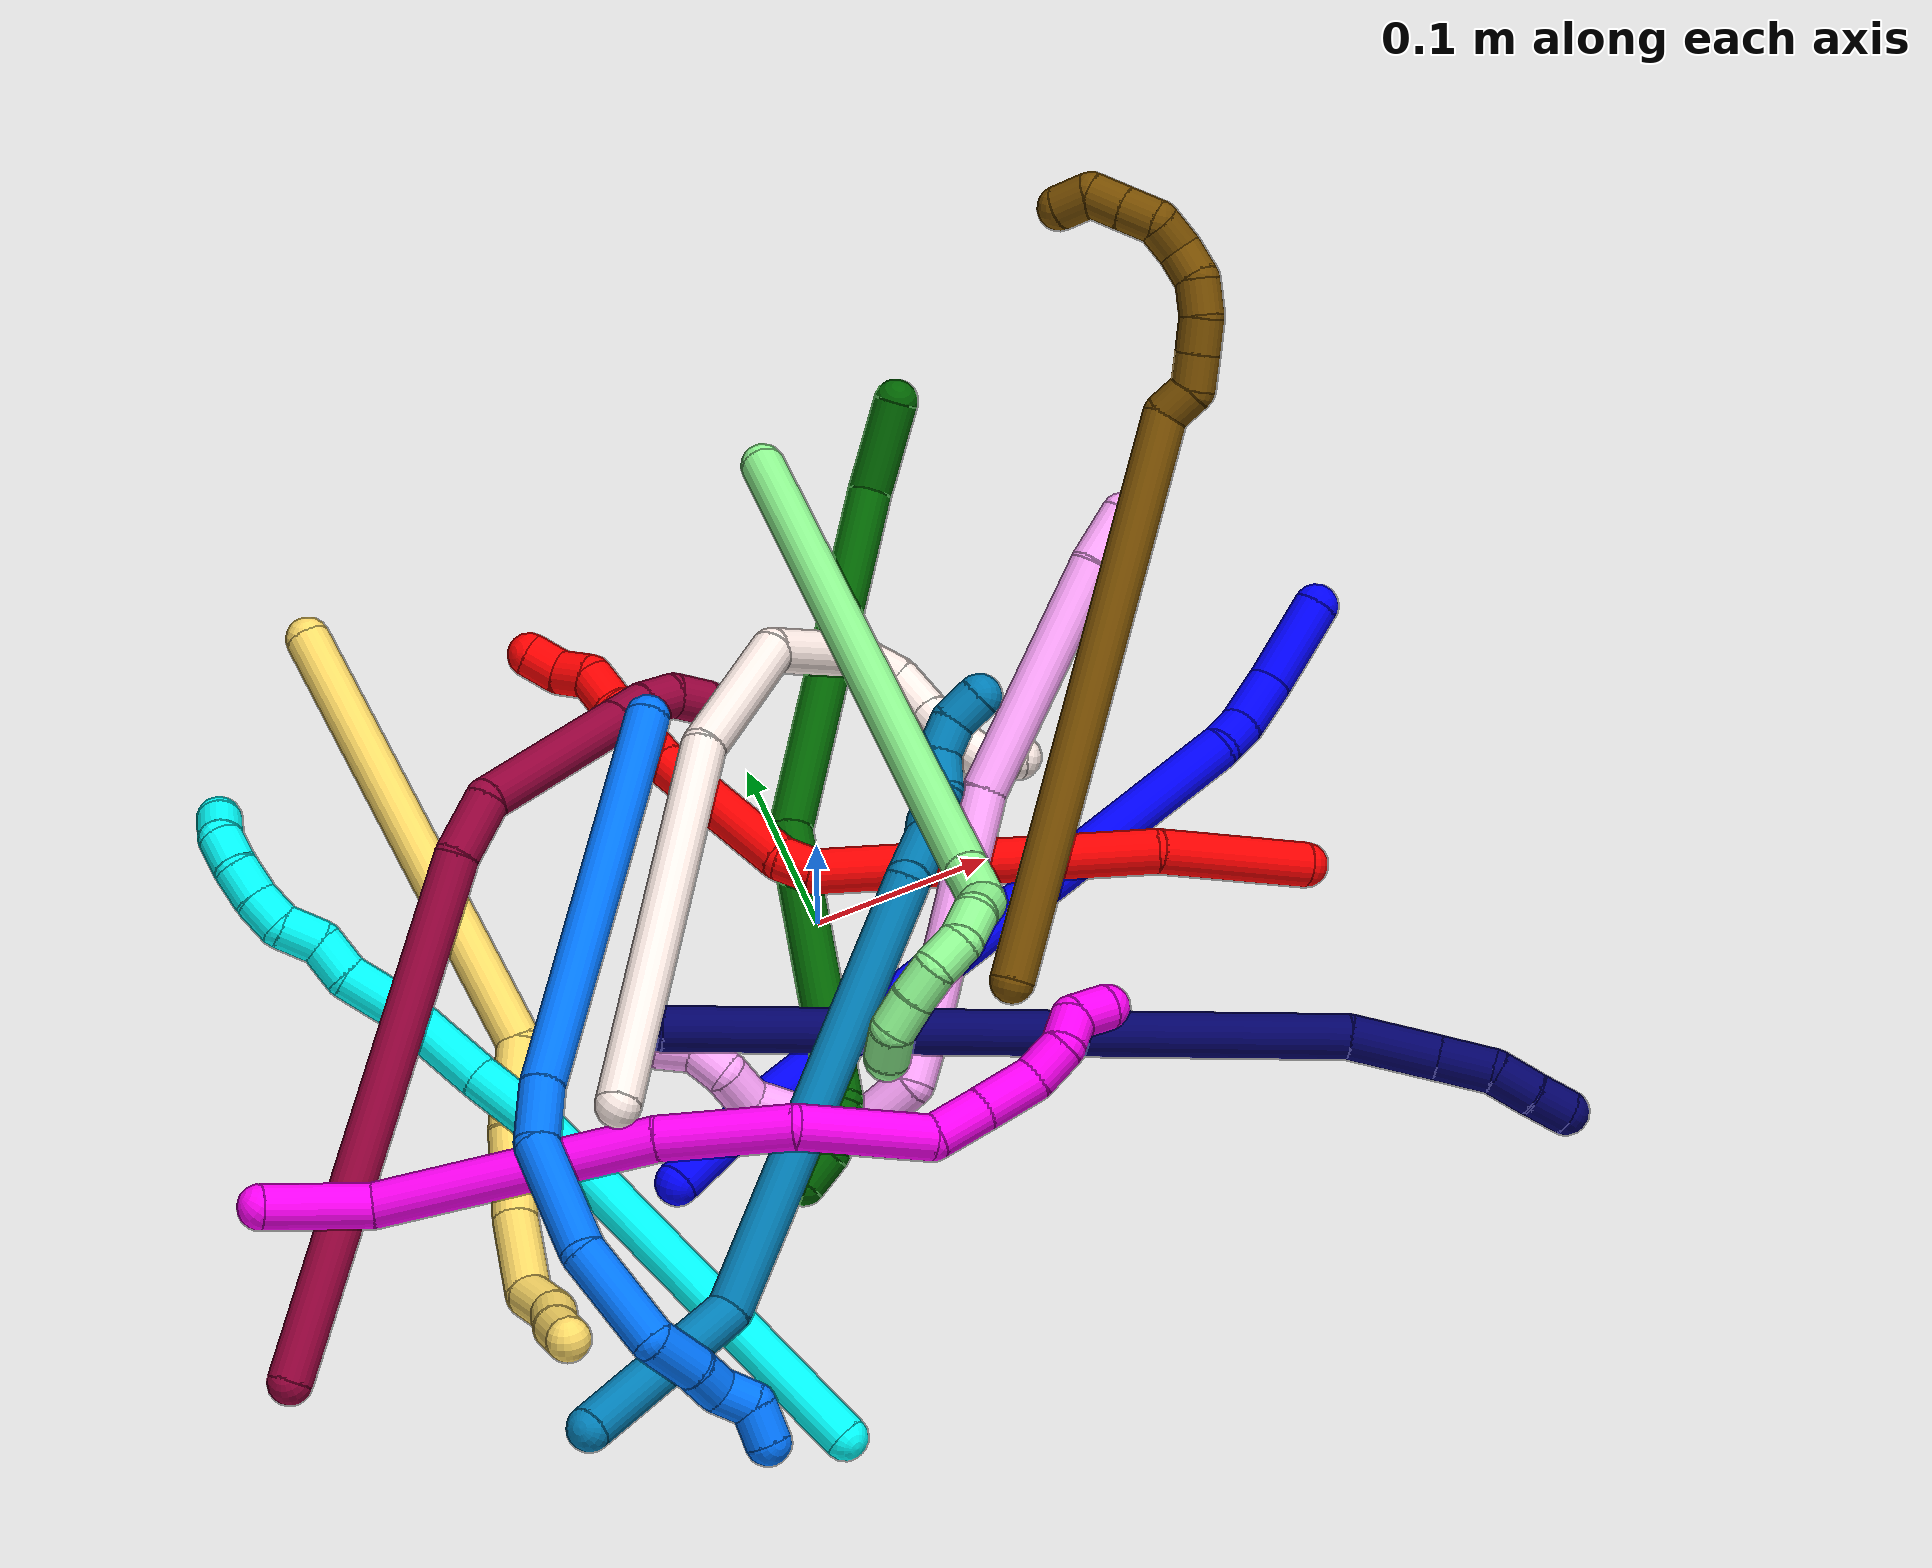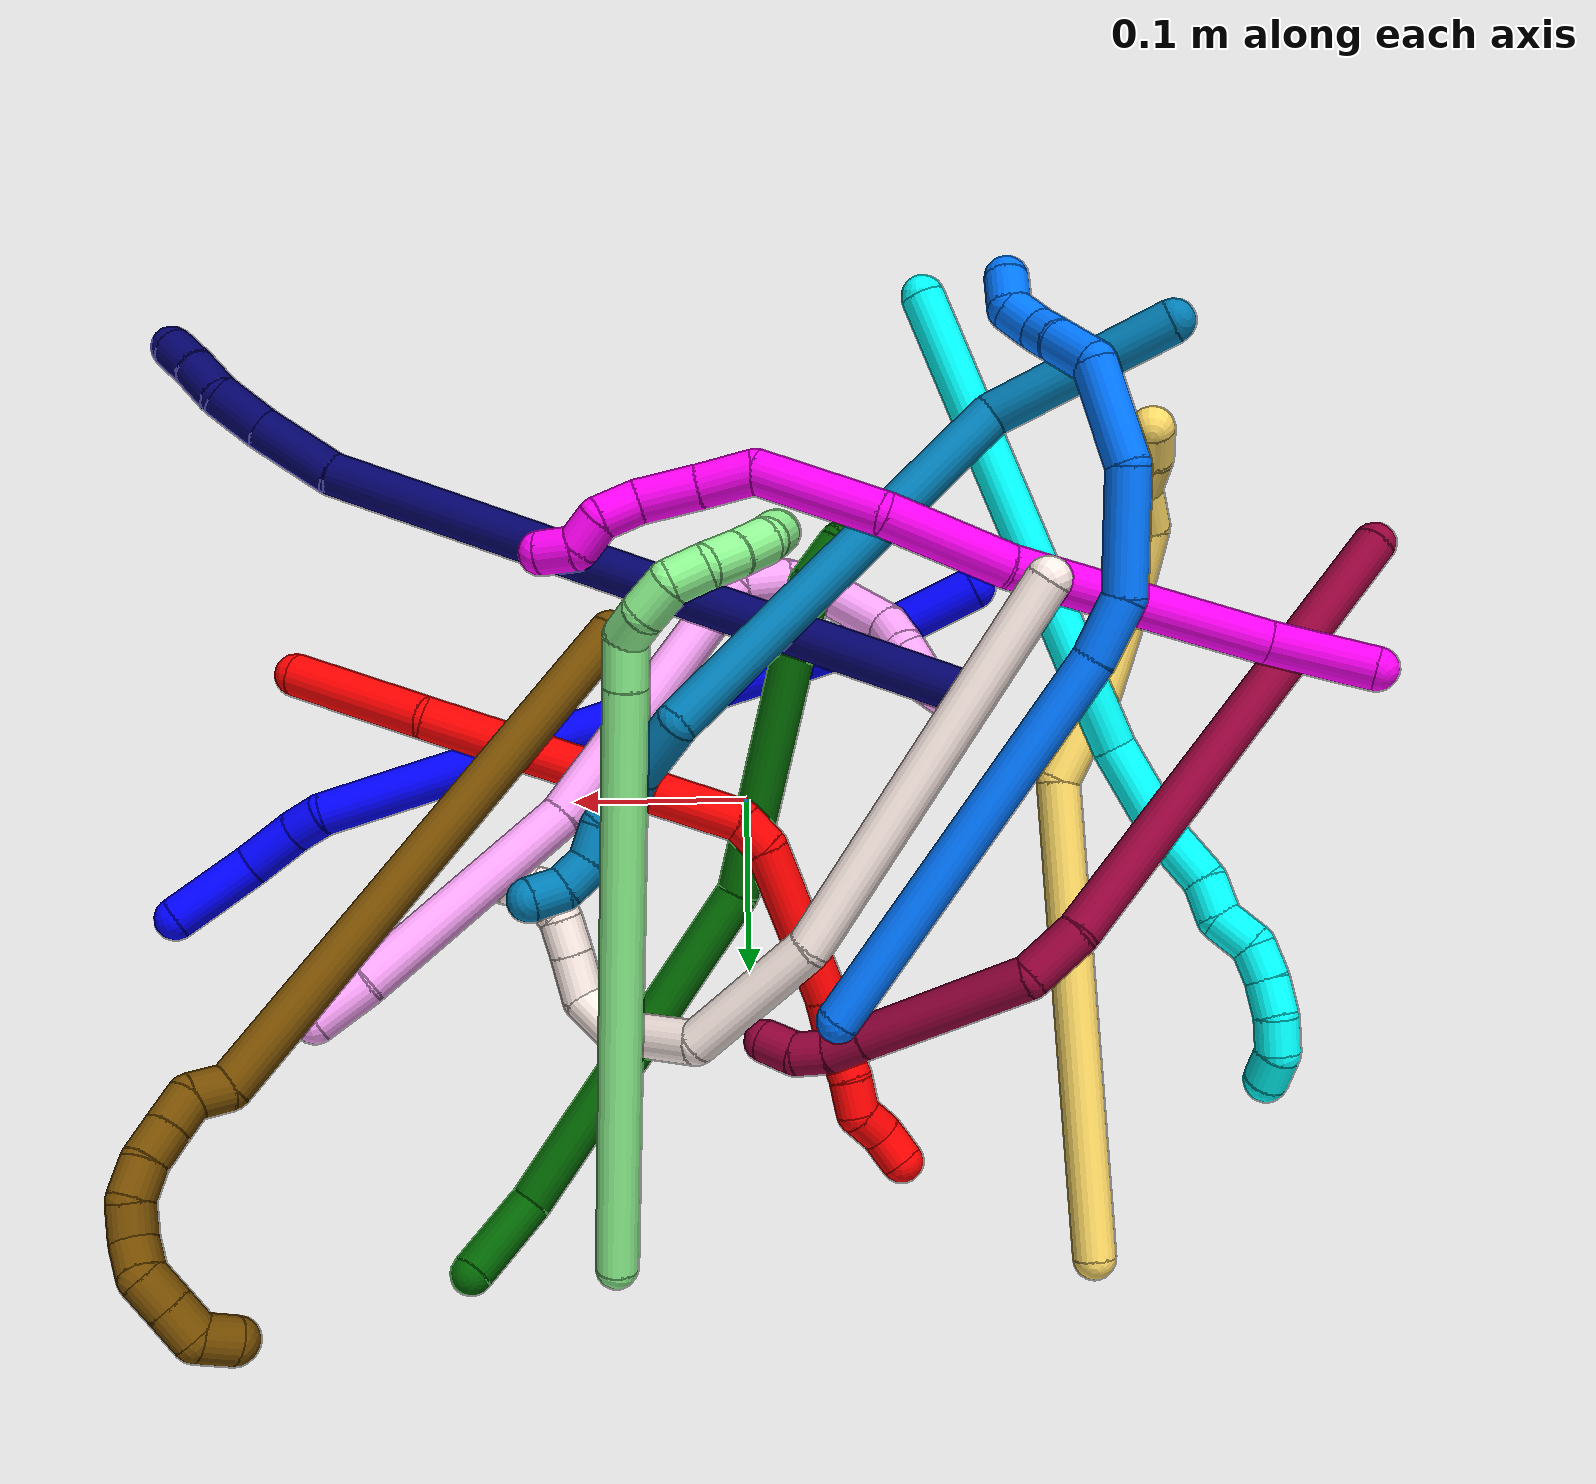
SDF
<sdf version="1.7">
 <world name="default">
  <plugin name="TubeGeneratorPlugin" filename="libtube_generator_plugin.so"/>
  <model name="photoneo_s_sensor">
   <static>1</static>
   <pose>0 0 2 1.57079 1.57079 3.14159</pose>
   <link name="link">
    <inertial><mass>0.1</mass></inertial>
    <sensor name="sensor" type="depth">
     <update_rate>30</update_rate>
     <camera>
      <horizontal_fov>1.22</horizontal_fov>
      <image><width>1920</width><height>1200</height><format>B8G8R8</format></image>
      <clip><near>0.1</near><far>4</far></clip>
      <depth_camera><output>points</output></depth_camera>
     </camera>
     <plugin name="camera_plugin" filename="libgazebo_ros_depth_camera.so">
      <baseline>0.2</baseline>
      <alwaysOn>1</alwaysOn>
      <updateRate>0.0</updateRate>
      <cameraName>camera_ir</cameraName>
      <imageTopicName>/camera/color/image_raw</imageTopicName>
      <cameraInfoTopicName>/camera/color/camera_info</cameraInfoTopicName>
      <depthImageTopicName>/camera/depth/image_raw</depthImageTopicName>
      <depthImageCameraInfoTopicName>/camera/depth/camera_info</depthImageCameraInfoTopicName>
      <pointCloudTopicName>/camera/depth/points</pointCloudTopicName>
      <frameName>fr_optical</frameName>
      <pointCloudCutoff>0.1</pointCloudCutoff>
      <pointCloudCutoffMax>2.0</pointCloudCutoffMax>
      <distortionK1>0</distortionK1>
      <distortionK2>0</distortionK2>
      <distortionK3>0</distortionK3>
      <distortionT1>0</distortionT1>
      <distortionT2>0</distortionT2>
      <CxPrime>0</CxPrime>
      <Cx>0</Cx>
      <Cy>0</Cy>
      <focalLength>0</focalLength>
      <hackBaseline>0</hackBaseline>
     </plugin>
    </sensor>
   </link>
  </model>
  <gravity>0 0 -9.8</gravity>
  <magnetic_field>6e-06 2.3e-05 -4.2e-05</magnetic_field>
  <atmosphere type="adiabatic"/>
  <physics name="default_physics" default="0" type="ode">
   <max_step_size>0.003</max_step_size>
   <real_time_factor>1</real_time_factor>
   <real_time_update_rate>1000</real_time_update_rate>
   <max_contacts>10000</max_contacts>
   <ode>
    <solver>
     <type>quick</type>
     <iters>100</iters>
     <sor>1.3</sor>
     <use_dynamic_moi_rescaling>0</use_dynamic_moi_rescaling>
    </solver>
    <constraints>
     <contact_max_correcting_vel>0</contact_max_correcting_vel>
     <contact_surface_layer>0.001</contact_surface_layer>
     <cfm>0</cfm>
     <erp>0.2</erp>
    </constraints>
   </ode>
  </physics>
  <scene><ambient>0.4 0.4 0.4 1</ambient><background>0.7 0.7 0.7 1</background><shadows>0</shadows></scene>
  <audio><device>default</device></audio>
  <spherical_coordinates>
   <surface_model>EARTH_WGS84</surface_model>
   <latitude_deg>0</latitude_deg>
   <longitude_deg>0</longitude_deg>
   <elevation>0</elevation>
   <heading_deg>0</heading_deg>
  </spherical_coordinates>
  <model name="bin">
   <static>1</static>
   <link name="bottom">
    <collision name="collision-bottom">
     <pose>0 0 -0.01 0 -0 0</pose>
     <geometry><box><size>0.8 0.6 0.02</size></box></geometry>
     <surface>
      <friction><ode><mu>100</mu><mu2>100</mu2></ode></friction>
      <contact><collide_bitmask>65535</collide_bitmask></contact>
     </surface>
    </collision>
   </link>
   <link name="west_wall">
    <collision name="collision-west_wall">
     <pose>-0.41 0 0.1 0 -0 0</pose>
     <geometry><box><size>0.02 0.6 0.2</size></box></geometry>
     <surface>
      <friction><ode><mu>100</mu><mu2>100</mu2></ode></friction>
      <contact><collide_bitmask>65535</collide_bitmask></contact>
     </surface>
    </collision>
   </link>
   <link name="east_wall">
    <collision name="collision-east_wall">
     <pose>0.41 0 0.1 0 -0 0</pose>
     <geometry><box><size>0.02 0.6 0.2</size></box></geometry>
     <surface>
      <friction><ode><mu>100</mu><mu2>100</mu2></ode></friction>
      <contact><collide_bitmask>65535</collide_bitmask></contact>
     </surface>
    </collision>
   </link>
   <link name="south_wall">
    <collision name="collision-south_wall">
     <pose>0 -0.31 0.1 0 -0 0</pose>
     <geometry><box><size>0.8 0.02 0.2</size></box></geometry>
     <surface>
      <friction><ode><mu>100</mu><mu2>100</mu2></ode></friction>
      <contact><collide_bitmask>65535</collide_bitmask></contact>
     </surface>
    </collision>
   </link>
   <link name="north_wall">
    <collision name="collision-north_wall">
     <pose>0 0.31 0.1 0 -0 0</pose>
     <geometry><box><size>0.8 0.02 0.2</size></box></geometry>
     <surface>
      <friction><ode><mu>100</mu><mu2>100</mu2></ode></friction>
      <contact><collide_bitmask>65535</collide_bitmask></contact>
     </surface>
    </collision>
   </link>
  </model>
  <model name="1">
   <static>0</static>
   <link name="1">
    <collision name="collision-cylinder-e_1_1_4">
     <pose>0.028412 0.007759 -0.000709 -1.66189 1.30316 -1.39208</pose>
     <geometry><cylinder><radius>0.0125</radius><length>0.058921</length></cylinder></geometry>
     <surface>
      <friction><ode><mu>1.16</mu><mu2>1.16</mu2><slip1>0</slip1><slip2>0</slip2></ode></friction>
      <contact><ode><kp>1e+06</kp><kd>1</kd><max_vel>0</max_vel><min_depth>0.001</min_depth></ode></contact>
     </surface>
    </collision>
    <visual name="visual-cylinder-e_1_1_4">
     <pose>0.028412 0.007759 -0.000709 -1.66189 1.30316 -1.39208</pose>
     <geometry><cylinder><radius>0.0125</radius><length>0.058921</length></cylinder></geometry>
     <material><ambient>0 0 1 1</ambient></material>
    </visual>
    <collision name="collision-cylinder-e_2_4_5">
     <pose>0.212809 0.070879 0.028861 -1.07032 1.18639 -0.76051</pose>
     <geometry><cylinder><radius>0.0125</radius><length>0.33653</length></cylinder></geometry>
     <surface>
      <friction><ode><mu>1.16</mu><mu2>1.16</mu2><slip1>0</slip1><slip2>0</slip2></ode></friction>
      <contact><ode><kp>1e+06</kp><kd>1</kd><max_vel>0</max_vel><min_depth>0.001</min_depth></ode></contact>
     </surface>
    </collision>
    <visual name="visual-cylinder-e_2_4_5">
     <pose>0.212809 0.070879 0.028861 -1.07032 1.18639 -0.76051</pose>
     <geometry><cylinder><radius>0.0125</radius><length>0.33653</length></cylinder></geometry>
     <material><ambient>0 0 1 1</ambient></material>
    </visual>
    <collision name="collision-cylinder-e_3_5_6">
     <pose>0.37857 0.12798 0.057715 -2.25688 1.34469 -2.06813</pose>
     <geometry><cylinder><radius>0.0125</radius><length>0.020063</length></cylinder></geometry>
     <surface>
      <friction><ode><mu>1.16</mu><mu2>1.16</mu2><slip1>0</slip1><slip2>0</slip2></ode></friction>
      <contact><ode><kp>1e+06</kp><kd>1</kd><max_vel>0</max_vel><min_depth>0.001</min_depth></ode></contact>
     </surface>
    </collision>
    <visual name="visual-cylinder-e_3_5_6">
     <pose>0.37857 0.12798 0.057715 -2.25688 1.34469 -2.06813</pose>
     <geometry><cylinder><radius>0.0125</radius><length>0.020063</length></cylinder></geometry>
     <material><ambient>0 0 1 1</ambient></material>
    </visual>
    <collision name="collision-cylinder-e_4_6_7">
     <pose>0.403252 0.135739 0.053483 -2.00722 1.15166 -1.58979</pose>
     <geometry><cylinder><radius>0.0125</radius><length>0.032636</length></cylinder></geometry>
     <surface>
      <friction><ode><mu>1.16</mu><mu2>1.16</mu2><slip1>0</slip1><slip2>0</slip2></ode></friction>
      <contact><ode><kp>1e+06</kp><kd>1</kd><max_vel>0</max_vel><min_depth>0.001</min_depth></ode></contact>
     </surface>
    </collision>
    <visual name="visual-cylinder-e_4_6_7">
     <pose>0.403252 0.135739 0.053483 -2.00722 1.15166 -1.58979</pose>
     <geometry><cylinder><radius>0.0125</radius><length>0.032636</length></cylinder></geometry>
     <material><ambient>0 0 1 1</ambient></material>
    </visual>
    <collision name="collision-cylinder-e_5_7_2">
     <pose>0.439124 0.15698 0.049809 -1.62771 0.942034 -0.988854</pose>
     <geometry><cylinder><radius>0.0125</radius><length>0.05185</length></cylinder></geometry>
     <surface>
      <friction><ode><mu>1.16</mu><mu2>1.16</mu2><slip1>0</slip1><slip2>0</slip2></ode></friction>
      <contact><ode><kp>1e+06</kp><kd>1</kd><max_vel>0</max_vel><min_depth>0.001</min_depth></ode></contact>
     </surface>
    </collision>
    <visual name="visual-cylinder-e_5_7_2">
     <pose>0.439124 0.15698 0.049809 -1.62771 0.942034 -0.988854</pose>
     <geometry><cylinder><radius>0.0125</radius><length>0.05185</length></cylinder></geometry>
     <material><ambient>0 0 1 1</ambient></material>
    </visual>
    <collision name="collision-sphere-2">
     <pose>0.460091 0.172203 0.048941 0 -0 0</pose>
     <geometry><sphere><radius>0.0125</radius></sphere></geometry>
     <surface>
      <friction><ode><mu>1.16</mu><mu2>1.16</mu2><slip1>0</slip1><slip2>0</slip2></ode></friction>
      <contact><ode><kp>1e+06</kp><kd>1</kd><max_vel>0</max_vel><min_depth>0.001</min_depth></ode></contact>
     </surface>
    </collision>
    <visual name="visual-sphere-2">
     <pose>0.460091 0.172203 0.048941 0 -0 0</pose>
     <geometry><sphere><radius>0.0125</radius></sphere></geometry>
     <material><ambient>0 0 1 1</ambient></material>
    </visual>
    <collision name="collision-sphere-7">
     <pose>0.418157 0.141757 0.050676 0 -0 0</pose>
     <geometry><sphere><radius>0.0125</radius></sphere></geometry>
     <surface>
      <friction><ode><mu>1.16</mu><mu2>1.16</mu2><slip1>0</slip1><slip2>0</slip2></ode></friction>
      <contact><ode><kp>1e+06</kp><kd>1</kd><max_vel>0</max_vel><min_depth>0.001</min_depth></ode></contact>
     </surface>
    </collision>
    <visual name="visual-sphere-7">
     <pose>0.418157 0.141757 0.050676 0 -0 0</pose>
     <geometry><sphere><radius>0.0125</radius></sphere></geometry>
     <material><ambient>0 0 1 1</ambient></material>
    </visual>
    <collision name="collision-sphere-6">
     <pose>0.388346 0.12972 0.05629 0 -0 0</pose>
     <geometry><sphere><radius>0.0125</radius></sphere></geometry>
     <surface>
      <friction><ode><mu>1.16</mu><mu2>1.16</mu2><slip1>0</slip1><slip2>0</slip2></ode></friction>
      <contact><ode><kp>1e+06</kp><kd>1</kd><max_vel>0</max_vel><min_depth>0.001</min_depth></ode></contact>
     </surface>
    </collision>
    <visual name="visual-sphere-6">
     <pose>0.388346 0.12972 0.05629 0 -0 0</pose>
     <geometry><sphere><radius>0.0125</radius></sphere></geometry>
     <material><ambient>0 0 1 1</ambient></material>
    </visual>
    <collision name="collision-sphere-5">
     <pose>0.368794 0.12624 0.05914 0 -0 0</pose>
     <geometry><sphere><radius>0.0125</radius></sphere></geometry>
     <surface>
      <friction><ode><mu>1.16</mu><mu2>1.16</mu2><slip1>0</slip1><slip2>0</slip2></ode></friction>
      <contact><ode><kp>1e+06</kp><kd>1</kd><max_vel>0</max_vel><min_depth>0.001</min_depth></ode></contact>
     </surface>
    </collision>
    <visual name="visual-sphere-5">
     <pose>0.368794 0.12624 0.05914 0 -0 0</pose>
     <geometry><sphere><radius>0.0125</radius></sphere></geometry>
     <material><ambient>0 0 1 1</ambient></material>
    </visual>
    <collision name="collision-sphere-1">
     <geometry><sphere><radius>0.0125</radius></sphere></geometry>
     <surface>
      <friction><ode><mu>1.16</mu><mu2>1.16</mu2><slip1>0</slip1><slip2>0</slip2></ode></friction>
      <contact><ode><kp>1e+06</kp><kd>1</kd><max_vel>0</max_vel><min_depth>0.001</min_depth></ode></contact>
     </surface>
    </collision>
    <visual name="visual-sphere-1">
     <geometry><sphere><radius>0.0125</radius></sphere></geometry>
     <material><ambient>0 0 1 1</ambient></material>
    </visual>
    <collision name="collision-sphere-4">
     <pose>0.056823 0.015517 -0.001417 0 -0 0</pose>
     <geometry><sphere><radius>0.0125</radius></sphere></geometry>
     <surface>
      <friction><ode><mu>1.16</mu><mu2>1.16</mu2><slip1>0</slip1><slip2>0</slip2></ode></friction>
      <contact><ode><kp>1e+06</kp><kd>1</kd><max_vel>0</max_vel><min_depth>0.001</min_depth></ode></contact>
     </surface>
    </collision>
    <visual name="visual-sphere-4">
     <pose>0.056823 0.015517 -0.001417 0 -0 0</pose>
     <geometry><sphere><radius>0.0125</radius></sphere></geometry>
     <material><ambient>0 0 1 1</ambient></material>
    </visual>
    <inertial>
     <pose>0.23363 0.078894 0.030314 0 -0 0</pose>
     <mass>0.5</mass>
     <inertia>
      <ixx>6.9e-05</ixx>
      <ixy>0</ixy>
      <ixz>0</ixz>
      <iyy>0.002104</iyy>
      <iyz>0</iyz>
      <izz>-0.004052</izz>
     </inertia>
    </inertial>
   </link>
   <pose>-0.131382 -0.119922 0.01943 1.05977 0.358976 0.295271</pose>
  </model>
  <model name="2">
   <static>0</static>
   <link name="2">
    <collision name="collision-cylinder-e_1_1_4">
     <pose>-0.00991 0.01316 0.040696 -0.312755 -0.227692 0.036051</pose>
     <geometry><cylinder><radius>0.0125</radius><length>0.087808</length></cylinder></geometry>
     <surface>
      <friction><ode><mu>1.16</mu><mu2>1.16</mu2><slip1>0</slip1><slip2>0</slip2></ode></friction>
      <contact><ode><kp>1e+06</kp><kd>1</kd><max_vel>0</max_vel><min_depth>0.001</min_depth></ode></contact>
     </surface>
    </collision>
    <visual name="visual-cylinder-e_1_1_4">
     <pose>-0.00991 0.01316 0.040696 -0.312755 -0.227692 0.036051</pose>
     <geometry><cylinder><radius>0.0125</radius><length>0.087808</length></cylinder></geometry>
     <material><ambient>1 0 0 1</ambient></material>
    </visual>
    <collision name="collision-cylinder-e_2_4_5">
     <pose>-0.06645 0.065152 0.152587 -0.499336 -0.521821 0.135952</pose>
     <geometry><cylinder><radius>0.0125</radius><length>0.187092</length></cylinder></geometry>
     <surface>
      <friction><ode><mu>1.16</mu><mu2>1.16</mu2><slip1>0</slip1><slip2>0</slip2></ode></friction>
      <contact><ode><kp>1e+06</kp><kd>1</kd><max_vel>0</max_vel><min_depth>0.001</min_depth></ode></contact>
     </surface>
    </collision>
    <visual name="visual-cylinder-e_2_4_5">
     <pose>-0.06645 0.065152 0.152587 -0.499336 -0.521821 0.135952</pose>
     <geometry><cylinder><radius>0.0125</radius><length>0.187092</length></cylinder></geometry>
     <material><ambient>1 0 0 1</ambient></material>
    </visual>
    <collision name="collision-cylinder-e_3_5_6">
     <pose>-0.115886 0.112264 0.229327 -0.980617 -0.274547 0.14721</pose>
     <geometry><cylinder><radius>0.0125</radius><length>0.020707</length></cylinder></geometry>
     <surface>
      <friction><ode><mu>1.16</mu><mu2>1.16</mu2><slip1>0</slip1><slip2>0</slip2></ode></friction>
      <contact><ode><kp>1e+06</kp><kd>1</kd><max_vel>0</max_vel><min_depth>0.001</min_depth></ode></contact>
     </surface>
    </collision>
    <visual name="visual-cylinder-e_3_5_6">
     <pose>-0.115886 0.112264 0.229327 -0.980617 -0.274547 0.14721</pose>
     <geometry><cylinder><radius>0.0125</radius><length>0.020707</length></cylinder></geometry>
     <material><ambient>1 0 0 1</ambient></material>
    </visual>
    <collision name="collision-cylinder-e_4_6_7">
     <pose>-0.124209 0.166569 0.24494 -1.35546 -0.116564 0.093862</pose>
     <geometry><cylinder><radius>0.0125</radius><length>0.09487</length></cylinder></geometry>
     <surface>
      <friction><ode><mu>1.16</mu><mu2>1.16</mu2><slip1>0</slip1><slip2>0</slip2></ode></friction>
      <contact><ode><kp>1e+06</kp><kd>1</kd><max_vel>0</max_vel><min_depth>0.001</min_depth></ode></contact>
     </surface>
    </collision>
    <visual name="visual-cylinder-e_4_6_7">
     <pose>-0.124209 0.166569 0.24494 -1.35546 -0.116564 0.093862</pose>
     <geometry><cylinder><radius>0.0125</radius><length>0.09487</length></cylinder></geometry>
     <material><ambient>1 0 0 1</ambient></material>
    </visual>
    <collision name="collision-cylinder-e_5_7_8">
     <pose>-0.129132 0.225839 0.257688 -1.37109 0.043911 -0.035915</pose>
     <geometry><cylinder><radius>0.0125</radius><length>0.027054</length></cylinder></geometry>
     <surface>
      <friction><ode><mu>1.16</mu><mu2>1.16</mu2><slip1>0</slip1><slip2>0</slip2></ode></friction>
      <contact><ode><kp>1e+06</kp><kd>1</kd><max_vel>0</max_vel><min_depth>0.001</min_depth></ode></contact>
     </surface>
    </collision>
    <visual name="visual-cylinder-e_5_7_8">
     <pose>-0.129132 0.225839 0.257688 -1.37109 0.043911 -0.035915</pose>
     <geometry><cylinder><radius>0.0125</radius><length>0.027054</length></cylinder></geometry>
     <material><ambient>1 0 0 1</ambient></material>
    </visual>
    <collision name="collision-cylinder-e_6_8_9">
     <pose>-0.12745 0.249047 0.26415 -1.20809 0.101778 -0.070268</pose>
     <geometry><cylinder><radius>0.0125</radius><length>0.021424</length></cylinder></geometry>
     <surface>
      <friction><ode><mu>1.16</mu><mu2>1.16</mu2><slip1>0</slip1><slip2>0</slip2></ode></friction>
      <contact><ode><kp>1e+06</kp><kd>1</kd><max_vel>0</max_vel><min_depth>0.001</min_depth></ode></contact>
     </surface>
    </collision>
    <visual name="visual-cylinder-e_6_8_9">
     <pose>-0.12745 0.249047 0.26415 -1.20809 0.101778 -0.070268</pose>
     <geometry><cylinder><radius>0.0125</radius><length>0.021424</length></cylinder></geometry>
     <material><ambient>1 0 0 1</ambient></material>
    </visual>
    <collision name="collision-cylinder-e_7_9_10">
     <pose>-0.125417 0.269268 0.26983 -1.38771 0.090285 -0.075118</pose>
     <geometry><cylinder><radius>0.0125</radius><length>0.020948</length></cylinder></geometry>
     <surface>
      <friction><ode><mu>1.16</mu><mu2>1.16</mu2><slip1>0</slip1><slip2>0</slip2></ode></friction>
      <contact><ode><kp>1e+06</kp><kd>1</kd><max_vel>0</max_vel><min_depth>0.001</min_depth></ode></contact>
     </surface>
    </collision>
    <visual name="visual-cylinder-e_7_9_10">
     <pose>-0.125417 0.269268 0.26983 -1.38771 0.090285 -0.075118</pose>
     <geometry><cylinder><radius>0.0125</radius><length>0.020948</length></cylinder></geometry>
     <material><ambient>1 0 0 1</ambient></material>
    </visual>
    <collision name="collision-cylinder-e_8_10_11">
     <pose>-0.129802 0.287415 0.274929 -1.18549 -0.559186 0.382048</pose>
     <geometry><cylinder><radius>0.0125</radius><length>0.020089</length></cylinder></geometry>
     <surface>
      <friction><ode><mu>1.16</mu><mu2>1.16</mu2><slip1>0</slip1><slip2>0</slip2></ode></friction>
      <contact><ode><kp>1e+06</kp><kd>1</kd><max_vel>0</max_vel><min_depth>0.001</min_depth></ode></contact>
     </surface>
    </collision>
    <visual name="visual-cylinder-e_8_10_11">
     <pose>-0.129802 0.287415 0.274929 -1.18549 -0.559186 0.382048</pose>
     <geometry><cylinder><radius>0.0125</radius><length>0.020089</length></cylinder></geometry>
     <material><ambient>1 0 0 1</ambient></material>
    </visual>
    <collision name="collision-cylinder-e_9_11_2">
     <pose>-0.136156 0.303588 0.283645 -0.983284 -0.102743 0.055053</pose>
     <geometry><cylinder><radius>0.0125</radius><length>0.020008</length></cylinder></geometry>
     <surface>
      <friction><ode><mu>1.16</mu><mu2>1.16</mu2><slip1>0</slip1><slip2>0</slip2></ode></friction>
      <contact><ode><kp>1e+06</kp><kd>1</kd><max_vel>0</max_vel><min_depth>0.001</min_depth></ode></contact>
     </surface>
    </collision>
    <visual name="visual-cylinder-e_9_11_2">
     <pose>-0.136156 0.303588 0.283645 -0.983284 -0.102743 0.055053</pose>
     <geometry><cylinder><radius>0.0125</radius><length>0.020008</length></cylinder></geometry>
     <material><ambient>1 0 0 1</ambient></material>
    </visual>
    <collision name="collision-sphere-2">
     <pose>-0.137182 0.311871 0.289161 0 -0 0</pose>
     <geometry><sphere><radius>0.0125</radius></sphere></geometry>
     <surface>
      <friction><ode><mu>1.16</mu><mu2>1.16</mu2><slip1>0</slip1><slip2>0</slip2></ode></friction>
      <contact><ode><kp>1e+06</kp><kd>1</kd><max_vel>0</max_vel><min_depth>0.001</min_depth></ode></contact>
     </surface>
    </collision>
    <visual name="visual-sphere-2">
     <pose>-0.137182 0.311871 0.289161 0 -0 0</pose>
     <geometry><sphere><radius>0.0125</radius></sphere></geometry>
     <material><ambient>1 0 0 1</ambient></material>
    </visual>
    <collision name="collision-sphere-11">
     <pose>-0.13513 0.295306 0.278129 0 -0 0</pose>
     <geometry><sphere><radius>0.0125</radius></sphere></geometry>
     <surface>
      <friction><ode><mu>1.16</mu><mu2>1.16</mu2><slip1>0</slip1><slip2>0</slip2></ode></friction>
      <contact><ode><kp>1e+06</kp><kd>1</kd><max_vel>0</max_vel><min_depth>0.001</min_depth></ode></contact>
     </surface>
    </collision>
    <visual name="visual-sphere-11">
     <pose>-0.13513 0.295306 0.278129 0 -0 0</pose>
     <geometry><sphere><radius>0.0125</radius></sphere></geometry>
     <material><ambient>1 0 0 1</ambient></material>
    </visual>
    <collision name="collision-sphere-10">
     <pose>-0.124473 0.279525 0.271729 0 -0 0</pose>
     <geometry><sphere><radius>0.0125</radius></sphere></geometry>
     <surface>
      <friction><ode><mu>1.16</mu><mu2>1.16</mu2><slip1>0</slip1><slip2>0</slip2></ode></friction>
      <contact><ode><kp>1e+06</kp><kd>1</kd><max_vel>0</max_vel><min_depth>0.001</min_depth></ode></contact>
     </surface>
    </collision>
    <visual name="visual-sphere-10">
     <pose>-0.124473 0.279525 0.271729 0 -0 0</pose>
     <geometry><sphere><radius>0.0125</radius></sphere></geometry>
     <material><ambient>1 0 0 1</ambient></material>
    </visual>
    <collision name="collision-sphere-9">
     <pose>-0.126362 0.259011 0.267931 0 -0 0</pose>
     <geometry><sphere><radius>0.0125</radius></sphere></geometry>
     <surface>
      <friction><ode><mu>1.16</mu><mu2>1.16</mu2><slip1>0</slip1><slip2>0</slip2></ode></friction>
      <contact><ode><kp>1e+06</kp><kd>1</kd><max_vel>0</max_vel><min_depth>0.001</min_depth></ode></contact>
     </surface>
    </collision>
    <visual name="visual-sphere-9">
     <pose>-0.126362 0.259011 0.267931 0 -0 0</pose>
     <geometry><sphere><radius>0.0125</radius></sphere></geometry>
     <material><ambient>1 0 0 1</ambient></material>
    </visual>
    <collision name="collision-sphere-4">
     <pose>-0.019821 0.02632 0.081392 0 -0 0</pose>
     <geometry><sphere><radius>0.0125</radius></sphere></geometry>
     <surface>
      <friction><ode><mu>1.16</mu><mu2>1.16</mu2><slip1>0</slip1><slip2>0</slip2></ode></friction>
      <contact><ode><kp>1e+06</kp><kd>1</kd><max_vel>0</max_vel><min_depth>0.001</min_depth></ode></contact>
     </surface>
    </collision>
    <visual name="visual-sphere-4">
     <pose>-0.019821 0.02632 0.081392 0 -0 0</pose>
     <geometry><sphere><radius>0.0125</radius></sphere></geometry>
     <material><ambient>1 0 0 1</ambient></material>
    </visual>
    <collision name="collision-sphere-1">
     <geometry><sphere><radius>0.0125</radius></sphere></geometry>
     <surface>
      <friction><ode><mu>1.16</mu><mu2>1.16</mu2><slip1>0</slip1><slip2>0</slip2></ode></friction>
      <contact><ode><kp>1e+06</kp><kd>1</kd><max_vel>0</max_vel><min_depth>0.001</min_depth></ode></contact>
     </surface>
    </collision>
    <visual name="visual-sphere-1">
     <geometry><sphere><radius>0.0125</radius></sphere></geometry>
     <material><ambient>1 0 0 1</ambient></material>
    </visual>
    <collision name="collision-sphere-8">
     <pose>-0.128539 0.239084 0.260369 0 -0 0</pose>
     <geometry><sphere><radius>0.0125</radius></sphere></geometry>
     <surface>
      <friction><ode><mu>1.16</mu><mu2>1.16</mu2><slip1>0</slip1><slip2>0</slip2></ode></friction>
      <contact><ode><kp>1e+06</kp><kd>1</kd><max_vel>0</max_vel><min_depth>0.001</min_depth></ode></contact>
     </surface>
    </collision>
    <visual name="visual-sphere-8">
     <pose>-0.128539 0.239084 0.260369 0 -0 0</pose>
     <geometry><sphere><radius>0.0125</radius></sphere></geometry>
     <material><ambient>1 0 0 1</ambient></material>
    </visual>
    <collision name="collision-sphere-5">
     <pose>-0.113079 0.103984 0.223781 0 -0 0</pose>
     <geometry><sphere><radius>0.0125</radius></sphere></geometry>
     <surface>
      <friction><ode><mu>1.16</mu><mu2>1.16</mu2><slip1>0</slip1><slip2>0</slip2></ode></friction>
      <contact><ode><kp>1e+06</kp><kd>1</kd><max_vel>0</max_vel><min_depth>0.001</min_depth></ode></contact>
     </surface>
    </collision>
    <visual name="visual-sphere-5">
     <pose>-0.113079 0.103984 0.223781 0 -0 0</pose>
     <geometry><sphere><radius>0.0125</radius></sphere></geometry>
     <material><ambient>1 0 0 1</ambient></material>
    </visual>
    <collision name="collision-sphere-6">
     <pose>-0.118693 0.120544 0.234873 0 -0 0</pose>
     <geometry><sphere><radius>0.0125</radius></sphere></geometry>
     <surface>
      <friction><ode><mu>1.16</mu><mu2>1.16</mu2><slip1>0</slip1><slip2>0</slip2></ode></friction>
      <contact><ode><kp>1e+06</kp><kd>1</kd><max_vel>0</max_vel><min_depth>0.001</min_depth></ode></contact>
     </surface>
    </collision>
    <visual name="visual-sphere-6">
     <pose>-0.118693 0.120544 0.234873 0 -0 0</pose>
     <geometry><sphere><radius>0.0125</radius></sphere></geometry>
     <material><ambient>1 0 0 1</ambient></material>
    </visual>
    <collision name="collision-sphere-7">
     <pose>-0.129726 0.212594 0.255007 0 -0 0</pose>
     <geometry><sphere><radius>0.0125</radius></sphere></geometry>
     <surface>
      <friction><ode><mu>1.16</mu><mu2>1.16</mu2><slip1>0</slip1><slip2>0</slip2></ode></friction>
      <contact><ode><kp>1e+06</kp><kd>1</kd><max_vel>0</max_vel><min_depth>0.001</min_depth></ode></contact>
     </surface>
    </collision>
    <visual name="visual-sphere-7">
     <pose>-0.129726 0.212594 0.255007 0 -0 0</pose>
     <geometry><sphere><radius>0.0125</radius></sphere></geometry>
     <material><ambient>1 0 0 1</ambient></material>
    </visual>
    <inertial>
     <pose>-0.083338 0.120812 0.179177 0 -0 0</pose>
     <mass>0.5</mass>
     <inertia><ixx>0.000681</ixx><ixy>0</ixy><ixz>0</ixz><iyy>0.000675</iyy><iyz>0</iyz><izz>-8e-06</izz></inertia>
    </inertial>
   </link>
   <pose>0.258432 -0.075754 0.011492 -0.394636 -0.814433 0.414095</pose>
  </model>
  <model name="3">
   <static>0</static>
   <link name="3">
    <collision name="collision-cylinder-e_1_1_4">
     <pose>0.005579 0.063101 -0.100642 -2.58157 0.046929 -0.162864</pose>
     <geometry><cylinder><radius>0.0125</radius><length>0.237837</length></cylinder></geometry>
     <surface>
      <friction><ode><mu>1.16</mu><mu2>1.16</mu2><slip1>0</slip1><slip2>0</slip2></ode></friction>
      <contact><ode><kp>1e+06</kp><kd>1</kd><max_vel>0</max_vel><min_depth>0.001</min_depth></ode></contact>
     </surface>
    </collision>
    <visual name="visual-cylinder-e_1_1_4">
     <pose>0.005579 0.063101 -0.100642 -2.58157 0.046929 -0.162864</pose>
     <geometry><cylinder><radius>0.0125</radius><length>0.237837</length></cylinder></geometry>
     <material><ambient>0.003922 1 0.996078 1</ambient></material>
    </visual>
    <collision name="collision-cylinder-e_2_4_5">
     <pose>0.009594 0.132647 -0.222552 -2.84735 -0.070217 0.465426</pose>
     <geometry><cylinder><radius>0.0125</radius><length>0.044556</length></cylinder></geometry>
     <surface>
      <friction><ode><mu>1.16</mu><mu2>1.16</mu2><slip1>0</slip1><slip2>0</slip2></ode></friction>
      <contact><ode><kp>1e+06</kp><kd>1</kd><max_vel>0</max_vel><min_depth>0.001</min_depth></ode></contact>
     </surface>
    </collision>
    <visual name="visual-cylinder-e_2_4_5">
     <pose>0.009594 0.132647 -0.222552 -2.84735 -0.070217 0.465426</pose>
     <geometry><cylinder><radius>0.0125</radius><length>0.044556</length></cylinder></geometry>
     <material><ambient>0.003922 1 0.996078 1</ambient></material>
    </visual>
    <collision name="collision-cylinder-e_3_5_6">
     <pose>0.006949 0.157017 -0.26561 -2.4532 -0.038346 0.106885</pose>
     <geometry><cylinder><radius>0.0125</radius><length>0.056474</length></cylinder></geometry>
     <surface>
      <friction><ode><mu>1.16</mu><mu2>1.16</mu2><slip1>0</slip1><slip2>0</slip2></ode></friction>
      <contact><ode><kp>1e+06</kp><kd>1</kd><max_vel>0</max_vel><min_depth>0.001</min_depth></ode></contact>
     </surface>
    </collision>
    <visual name="visual-cylinder-e_3_5_6">
     <pose>0.006949 0.157017 -0.26561 -2.4532 -0.038346 0.106885</pose>
     <geometry><cylinder><radius>0.0125</radius><length>0.056474</length></cylinder></geometry>
     <material><ambient>0.003922 1 0.996078 1</ambient></material>
    </visual>
    <collision name="collision-cylinder-e_4_6_7">
     <pose>0.002436 0.186484 -0.299285 -2.37082 -0.204191 0.494753</pose>
     <geometry><cylinder><radius>0.0125</radius><length>0.033834</length></cylinder></geometry>
     <surface>
      <friction><ode><mu>1.16</mu><mu2>1.16</mu2><slip1>0</slip1><slip2>0</slip2></ode></friction>
      <contact><ode><kp>1e+06</kp><kd>1</kd><max_vel>0</max_vel><min_depth>0.001</min_depth></ode></contact>
     </surface>
    </collision>
    <visual name="visual-cylinder-e_4_6_7">
     <pose>0.002436 0.186484 -0.299285 -2.37082 -0.204191 0.494753</pose>
     <geometry><cylinder><radius>0.0125</radius><length>0.033834</length></cylinder></geometry>
     <material><ambient>0.003922 1 0.996078 1</ambient></material>
    </visual>
    <collision name="collision-cylinder-e_5_7_8">
     <pose>0.000776 0.205411 -0.31977 -2.43202 0.154901 -0.412997</pose>
     <geometry><cylinder><radius>0.0125</radius><length>0.02295</length></cylinder></geometry>
     <surface>
      <friction><ode><mu>1.16</mu><mu2>1.16</mu2><slip1>0</slip1><slip2>0</slip2></ode></friction>
      <contact><ode><kp>1e+06</kp><kd>1</kd><max_vel>0</max_vel><min_depth>0.001</min_depth></ode></contact>
     </surface>
    </collision>
    <visual name="visual-cylinder-e_5_7_8">
     <pose>0.000776 0.205411 -0.31977 -2.43202 0.154901 -0.412997</pose>
     <geometry><cylinder><radius>0.0125</radius><length>0.02295</length></cylinder></geometry>
     <material><ambient>0.003922 1 0.996078 1</ambient></material>
    </visual>
    <collision name="collision-cylinder-e_6_8_9">
     <pose>-0.00151 0.221419 -0.335216 -2.24186 -0.353098 0.707801</pose>
     <geometry><cylinder><radius>0.0125</radius><length>0.023464</length></cylinder></geometry>
     <surface>
      <friction><ode><mu>1.16</mu><mu2>1.16</mu2><slip1>0</slip1><slip2>0</slip2></ode></friction>
      <contact><ode><kp>1e+06</kp><kd>1</kd><max_vel>0</max_vel><min_depth>0.001</min_depth></ode></contact>
     </surface>
    </collision>
    <visual name="visual-cylinder-e_6_8_9">
     <pose>-0.00151 0.221419 -0.335216 -2.24186 -0.353098 0.707801</pose>
     <geometry><cylinder><radius>0.0125</radius><length>0.023464</length></cylinder></geometry>
     <material><ambient>0.003922 1 0.996078 1</ambient></material>
    </visual>
    <collision name="collision-cylinder-e_7_9_10">
     <pose>-0.004759 0.235702 -0.350303 -2.53967 0.080673 -0.258598</pose>
     <geometry><cylinder><radius>0.0125</radius><length>0.020063</length></cylinder></geometry>
     <surface>
      <friction><ode><mu>1.16</mu><mu2>1.16</mu2><slip1>0</slip1><slip2>0</slip2></ode></friction>
      <contact><ode><kp>1e+06</kp><kd>1</kd><max_vel>0</max_vel><min_depth>0.001</min_depth></ode></contact>
     </surface>
    </collision>
    <visual name="visual-cylinder-e_7_9_10">
     <pose>-0.004759 0.235702 -0.350303 -2.53967 0.080673 -0.258598</pose>
     <geometry><cylinder><radius>0.0125</radius><length>0.020063</length></cylinder></geometry>
     <material><ambient>0.003922 1 0.996078 1</ambient></material>
    </visual>
    <collision name="collision-cylinder-e_8_10_11">
     <pose>-0.001526 0.246956 -0.366928 -2.55329 0.236109 -0.74634</pose>
     <geometry><cylinder><radius>0.0125</radius><length>0.020731</length></cylinder></geometry>
     <surface>
      <friction><ode><mu>1.16</mu><mu2>1.16</mu2><slip1>0</slip1><slip2>0</slip2></ode></friction>
      <contact><ode><kp>1e+06</kp><kd>1</kd><max_vel>0</max_vel><min_depth>0.001</min_depth></ode></contact>
     </surface>
    </collision>
    <visual name="visual-cylinder-e_8_10_11">
     <pose>-0.001526 0.246956 -0.366928 -2.55329 0.236109 -0.74634</pose>
     <geometry><cylinder><radius>0.0125</radius><length>0.020731</length></cylinder></geometry>
     <material><ambient>0.003922 1 0.996078 1</ambient></material>
    </visual>
    <collision name="collision-cylinder-e_9_11_12">
     <pose>0.003879 0.255297 -0.384492 -2.85079 0.301464 -1.60732</pose>
     <geometry><cylinder><radius>0.0125</radius><length>0.020071</length></cylinder></geometry>
     <surface>
      <friction><ode><mu>1.16</mu><mu2>1.16</mu2><slip1>0</slip1><slip2>0</slip2></ode></friction>
      <contact><ode><kp>1e+06</kp><kd>1</kd><max_vel>0</max_vel><min_depth>0.001</min_depth></ode></contact>
     </surface>
    </collision>
    <visual name="visual-cylinder-e_9_11_12">
     <pose>0.003879 0.255297 -0.384492 -2.85079 0.301464 -1.60732</pose>
     <geometry><cylinder><radius>0.0125</radius><length>0.020071</length></cylinder></geometry>
     <material><ambient>0.003922 1 0.996078 1</ambient></material>
    </visual>
    <collision name="collision-cylinder-e_10_12_2">
     <pose>0.01058 0.255246 -0.402534 2.83571 0.380908 1.79266</pose>
     <geometry><cylinder><radius>0.0125</radius><length>0.02002</length></cylinder></geometry>
     <surface>
      <friction><ode><mu>1.16</mu><mu2>1.16</mu2><slip1>0</slip1><slip2>0</slip2></ode></friction>
      <contact><ode><kp>1e+06</kp><kd>1</kd><max_vel>0</max_vel><min_depth>0.001</min_depth></ode></contact>
     </surface>
    </collision>
    <visual name="visual-cylinder-e_10_12_2">
     <pose>0.01058 0.255246 -0.402534 2.83571 0.380908 1.79266</pose>
     <geometry><cylinder><radius>0.0125</radius><length>0.02002</length></cylinder></geometry>
     <material><ambient>0.003922 1 0.996078 1</ambient></material>
    </visual>
    <collision name="collision-sphere-2">
     <pose>0.014301 0.252448 -0.411395 0 -0 0</pose>
     <geometry><sphere><radius>0.0125</radius></sphere></geometry>
     <surface>
      <friction><ode><mu>1.16</mu><mu2>1.16</mu2><slip1>0</slip1><slip2>0</slip2></ode></friction>
      <contact><ode><kp>1e+06</kp><kd>1</kd><max_vel>0</max_vel><min_depth>0.001</min_depth></ode></contact>
     </surface>
    </collision>
    <visual name="visual-sphere-2">
     <pose>0.014301 0.252448 -0.411395 0 -0 0</pose>
     <geometry><sphere><radius>0.0125</radius></sphere></geometry>
     <material><ambient>0.003922 1 0.996078 1</ambient></material>
    </visual>
    <collision name="collision-sphere-12">
     <pose>0.006858 0.258045 -0.393673 0 -0 0</pose>
     <geometry><sphere><radius>0.0125</radius></sphere></geometry>
     <surface>
      <friction><ode><mu>1.16</mu><mu2>1.16</mu2><slip1>0</slip1><slip2>0</slip2></ode></friction>
      <contact><ode><kp>1e+06</kp><kd>1</kd><max_vel>0</max_vel><min_depth>0.001</min_depth></ode></contact>
     </surface>
    </collision>
    <visual name="visual-sphere-12">
     <pose>0.006858 0.258045 -0.393673 0 -0 0</pose>
     <geometry><sphere><radius>0.0125</radius></sphere></geometry>
     <material><ambient>0.003922 1 0.996078 1</ambient></material>
    </visual>
    <collision name="collision-sphere-11">
     <pose>0.000899 0.252549 -0.375311 0 -0 0</pose>
     <geometry><sphere><radius>0.0125</radius></sphere></geometry>
     <surface>
      <friction><ode><mu>1.16</mu><mu2>1.16</mu2><slip1>0</slip1><slip2>0</slip2></ode></friction>
      <contact><ode><kp>1e+06</kp><kd>1</kd><max_vel>0</max_vel><min_depth>0.001</min_depth></ode></contact>
     </surface>
    </collision>
    <visual name="visual-sphere-11">
     <pose>0.000899 0.252549 -0.375311 0 -0 0</pose>
     <geometry><sphere><radius>0.0125</radius></sphere></geometry>
     <material><ambient>0.003922 1 0.996078 1</ambient></material>
    </visual>
    <collision name="collision-sphere-10">
     <pose>-0.003951 0.241364 -0.358544 0 -0 0</pose>
     <geometry><sphere><radius>0.0125</radius></sphere></geometry>
     <surface>
      <friction><ode><mu>1.16</mu><mu2>1.16</mu2><slip1>0</slip1><slip2>0</slip2></ode></friction>
      <contact><ode><kp>1e+06</kp><kd>1</kd><max_vel>0</max_vel><min_depth>0.001</min_depth></ode></contact>
     </surface>
    </collision>
    <visual name="visual-sphere-10">
     <pose>-0.003951 0.241364 -0.358544 0 -0 0</pose>
     <geometry><sphere><radius>0.0125</radius></sphere></geometry>
     <material><ambient>0.003922 1 0.996078 1</ambient></material>
    </visual>
    <collision name="collision-sphere-9">
     <pose>-0.005567 0.23004 -0.342061 0 -0 0</pose>
     <geometry><sphere><radius>0.0125</radius></sphere></geometry>
     <surface>
      <friction><ode><mu>1.16</mu><mu2>1.16</mu2><slip1>0</slip1><slip2>0</slip2></ode></friction>
      <contact><ode><kp>1e+06</kp><kd>1</kd><max_vel>0</max_vel><min_depth>0.001</min_depth></ode></contact>
     </surface>
    </collision>
    <visual name="visual-sphere-9">
     <pose>-0.005567 0.23004 -0.342061 0 -0 0</pose>
     <geometry><sphere><radius>0.0125</radius></sphere></geometry>
     <material><ambient>0.003922 1 0.996078 1</ambient></material>
    </visual>
    <collision name="collision-sphere-4">
     <pose>0.011157 0.126202 -0.201284 0 -0 0</pose>
     <geometry><sphere><radius>0.0125</radius></sphere></geometry>
     <surface>
      <friction><ode><mu>1.16</mu><mu2>1.16</mu2><slip1>0</slip1><slip2>0</slip2></ode></friction>
      <contact><ode><kp>1e+06</kp><kd>1</kd><max_vel>0</max_vel><min_depth>0.001</min_depth></ode></contact>
     </surface>
    </collision>
    <visual name="visual-sphere-4">
     <pose>0.011157 0.126202 -0.201284 0 -0 0</pose>
     <geometry><sphere><radius>0.0125</radius></sphere></geometry>
     <material><ambient>0.003922 1 0.996078 1</ambient></material>
    </visual>
    <collision name="collision-sphere-1">
     <geometry><sphere><radius>0.0125</radius></sphere></geometry>
     <surface>
      <friction><ode><mu>1.16</mu><mu2>1.16</mu2><slip1>0</slip1><slip2>0</slip2></ode></friction>
      <contact><ode><kp>1e+06</kp><kd>1</kd><max_vel>0</max_vel><min_depth>0.001</min_depth></ode></contact>
     </surface>
    </collision>
    <visual name="visual-sphere-1">
     <geometry><sphere><radius>0.0125</radius></sphere></geometry>
     <material><ambient>0.003922 1 0.996078 1</ambient></material>
    </visual>
    <collision name="collision-sphere-8">
     <pose>0.002547 0.212798 -0.328371 0 -0 0</pose>
     <geometry><sphere><radius>0.0125</radius></sphere></geometry>
     <surface>
      <friction><ode><mu>1.16</mu><mu2>1.16</mu2><slip1>0</slip1><slip2>0</slip2></ode></friction>
      <contact><ode><kp>1e+06</kp><kd>1</kd><max_vel>0</max_vel><min_depth>0.001</min_depth></ode></contact>
     </surface>
    </collision>
    <visual name="visual-sphere-8">
     <pose>0.002547 0.212798 -0.328371 0 -0 0</pose>
     <geometry><sphere><radius>0.0125</radius></sphere></geometry>
     <material><ambient>0.003922 1 0.996078 1</ambient></material>
    </visual>
    <collision name="collision-sphere-5">
     <pose>0.008031 0.139092 -0.24382 0 -0 0</pose>
     <geometry><sphere><radius>0.0125</radius></sphere></geometry>
     <surface>
      <friction><ode><mu>1.16</mu><mu2>1.16</mu2><slip1>0</slip1><slip2>0</slip2></ode></friction>
      <contact><ode><kp>1e+06</kp><kd>1</kd><max_vel>0</max_vel><min_depth>0.001</min_depth></ode></contact>
     </surface>
    </collision>
    <visual name="visual-sphere-5">
     <pose>0.008031 0.139092 -0.24382 0 -0 0</pose>
     <geometry><sphere><radius>0.0125</radius></sphere></geometry>
     <material><ambient>0.003922 1 0.996078 1</ambient></material>
    </visual>
    <collision name="collision-sphere-6">
     <pose>0.005866 0.174943 -0.287401 0 -0 0</pose>
     <geometry><sphere><radius>0.0125</radius></sphere></geometry>
     <surface>
      <friction><ode><mu>1.16</mu><mu2>1.16</mu2><slip1>0</slip1><slip2>0</slip2></ode></friction>
      <contact><ode><kp>1e+06</kp><kd>1</kd><max_vel>0</max_vel><min_depth>0.001</min_depth></ode></contact>
     </surface>
    </collision>
    <visual name="visual-sphere-6">
     <pose>0.005866 0.174943 -0.287401 0 -0 0</pose>
     <geometry><sphere><radius>0.0125</radius></sphere></geometry>
     <material><ambient>0.003922 1 0.996078 1</ambient></material>
    </visual>
    <collision name="collision-sphere-7">
     <pose>-0.000994 0.198025 -0.311168 0 -0 0</pose>
     <geometry><sphere><radius>0.0125</radius></sphere></geometry>
     <surface>
      <friction><ode><mu>1.16</mu><mu2>1.16</mu2><slip1>0</slip1><slip2>0</slip2></ode></friction>
      <contact><ode><kp>1e+06</kp><kd>1</kd><max_vel>0</max_vel><min_depth>0.001</min_depth></ode></contact>
     </surface>
    </collision>
    <visual name="visual-sphere-7">
     <pose>-0.000994 0.198025 -0.311168 0 -0 0</pose>
     <geometry><sphere><radius>0.0125</radius></sphere></geometry>
     <material><ambient>0.003922 1 0.996078 1</ambient></material>
    </visual>
    <inertial>
     <pose>0.004748 0.132174 -0.209187 0 -0 0</pose>
     <mass>0.5</mass>
     <inertia>
      <ixx>0.000974</ixx>
      <ixy>0</ixy>
      <ixz>0</ixz>
      <iyy>-0.001123</iyy>
      <iyz>0</iyz>
      <izz>-0.000705</izz>
     </inertia>
    </inertial>
   </link>
   <pose>-0.104616 -0.287722 0.017126 1.10676 -0.243958 0.393658</pose>
  </model>
  <model name="4">
   <static>0</static>
   <link name="4">
    <collision name="collision-cylinder-e_1_1_4">
     <pose>-0.005455 -0.001877 -0.015612 3.02192 -0.333885 -2.45846</pose>
     <geometry><cylinder><radius>0.0125</radius><length>0.033288</length></cylinder></geometry>
     <surface>
      <friction><ode><mu>1.16</mu><mu2>1.16</mu2><slip1>0</slip1><slip2>0</slip2></ode></friction>
      <contact><ode><kp>1e+06</kp><kd>1</kd><max_vel>0</max_vel><min_depth>0.001</min_depth></ode></contact>
     </surface>
    </collision>
    <visual name="visual-cylinder-e_1_1_4">
     <pose>-0.005455 -0.001877 -0.015612 3.02192 -0.333885 -2.45846</pose>
     <geometry><cylinder><radius>0.0125</radius><length>0.033288</length></cylinder></geometry>
     <material><ambient>1 0.65098 0.996078 1</ambient></material>
    </visual>
    <collision name="collision-cylinder-e_2_4_5">
     <pose>-0.023426 -0.015661 -0.097989 2.96512 -0.182508 -1.6046</pose>
     <geometry><cylinder><radius>0.0125</radius><length>0.137926</length></cylinder></geometry>
     <surface>
      <friction><ode><mu>1.16</mu><mu2>1.16</mu2><slip1>0</slip1><slip2>0</slip2></ode></friction>
      <contact><ode><kp>1e+06</kp><kd>1</kd><max_vel>0</max_vel><min_depth>0.001</min_depth></ode></contact>
     </surface>
    </collision>
    <visual name="visual-cylinder-e_2_4_5">
     <pose>-0.023426 -0.015661 -0.097989 2.96512 -0.182508 -1.6046</pose>
     <geometry><cylinder><radius>0.0125</radius><length>0.137926</length></cylinder></geometry>
     <material><ambient>1 0.65098 0.996078 1</ambient></material>
    </visual>
    <collision name="collision-cylinder-e_3_5_6">
     <pose>-0.048179 -0.053619 -0.226724 2.74361 -0.180055 -0.841788</pose>
     <geometry><cylinder><radius>0.0125</radius><length>0.136656</length></cylinder></geometry>
     <surface>
      <friction><ode><mu>1.16</mu><mu2>1.16</mu2><slip1>0</slip1><slip2>0</slip2></ode></friction>
      <contact><ode><kp>1e+06</kp><kd>1</kd><max_vel>0</max_vel><min_depth>0.001</min_depth></ode></contact>
     </surface>
    </collision>
    <visual name="visual-cylinder-e_3_5_6">
     <pose>-0.048179 -0.053619 -0.226724 2.74361 -0.180055 -0.841788</pose>
     <geometry><cylinder><radius>0.0125</radius><length>0.136656</length></cylinder></geometry>
     <material><ambient>1 0.65098 0.996078 1</ambient></material>
    </visual>
    <collision name="collision-cylinder-e_4_6_7">
     <pose>-0.062993 -0.084548 -0.30182 2.78595 -0.182042 -0.939842</pose>
     <geometry><cylinder><radius>0.0125</radius><length>0.028478</length></cylinder></geometry>
     <surface>
      <friction><ode><mu>1.16</mu><mu2>1.16</mu2><slip1>0</slip1><slip2>0</slip2></ode></friction>
      <contact><ode><kp>1e+06</kp><kd>1</kd><max_vel>0</max_vel><min_depth>0.001</min_depth></ode></contact>
     </surface>
    </collision>
    <visual name="visual-cylinder-e_4_6_7">
     <pose>-0.062993 -0.084548 -0.30182 2.78595 -0.182042 -0.939842</pose>
     <geometry><cylinder><radius>0.0125</radius><length>0.028478</length></cylinder></geometry>
     <material><ambient>1 0.65098 0.996078 1</ambient></material>
    </visual>
    <collision name="collision-cylinder-e_5_7_8">
     <pose>-0.064883 -0.083974 -0.329973 -2.79363 0.043001 -0.243489</pose>
     <geometry><cylinder><radius>0.0125</radius><length>0.031995</length></cylinder></geometry>
     <surface>
      <friction><ode><mu>1.16</mu><mu2>1.16</mu2><slip1>0</slip1><slip2>0</slip2></ode></friction>
      <contact><ode><kp>1e+06</kp><kd>1</kd><max_vel>0</max_vel><min_depth>0.001</min_depth></ode></contact>
     </surface>
    </collision>
    <visual name="visual-cylinder-e_5_7_8">
     <pose>-0.064883 -0.083974 -0.329973 -2.79363 0.043001 -0.243489</pose>
     <geometry><cylinder><radius>0.0125</radius><length>0.031995</length></cylinder></geometry>
     <material><ambient>1 0.65098 0.996078 1</ambient></material>
    </visual>
    <collision name="collision-cylinder-e_6_8_9">
     <pose>-0.069886 -0.068682 -0.352397 -2.21545 -0.43288 0.829692</pose>
     <geometry><cylinder><radius>0.0125</radius><length>0.02713</length></cylinder></geometry>
     <surface>
      <friction><ode><mu>1.16</mu><mu2>1.16</mu2><slip1>0</slip1><slip2>0</slip2></ode></friction>
      <contact><ode><kp>1e+06</kp><kd>1</kd><max_vel>0</max_vel><min_depth>0.001</min_depth></ode></contact>
     </surface>
    </collision>
    <visual name="visual-cylinder-e_6_8_9">
     <pose>-0.069886 -0.068682 -0.352397 -2.21545 -0.43288 0.829692</pose>
     <geometry><cylinder><radius>0.0125</radius><length>0.02713</length></cylinder></geometry>
     <material><ambient>1 0.65098 0.996078 1</ambient></material>
    </visual>
    <collision name="collision-cylinder-e_7_9_10">
     <pose>-0.088324 -0.043505 -0.363291 -1.79479 -0.681155 0.836044</pose>
     <geometry><cylinder><radius>0.0125</radius><length>0.040491</length></cylinder></geometry>
     <surface>
      <friction><ode><mu>1.16</mu><mu2>1.16</mu2><slip1>0</slip1><slip2>0</slip2></ode></friction>
      <contact><ode><kp>1e+06</kp><kd>1</kd><max_vel>0</max_vel><min_depth>0.001</min_depth></ode></contact>
     </surface>
    </collision>
    <visual name="visual-cylinder-e_7_9_10">
     <pose>-0.088324 -0.043505 -0.363291 -1.79479 -0.681155 0.836044</pose>
     <geometry><cylinder><radius>0.0125</radius><length>0.040491</length></cylinder></geometry>
     <material><ambient>1 0.65098 0.996078 1</ambient></material>
    </visual>
    <collision name="collision-cylinder-e_8_10_11">
     <pose>-0.108455 -0.020797 -0.363112 -1.10871 -0.730692 0.465076</pose>
     <geometry><cylinder><radius>0.0125</radius><length>0.022122</length></cylinder></geometry>
     <surface>
      <friction><ode><mu>1.16</mu><mu2>1.16</mu2><slip1>0</slip1><slip2>0</slip2></ode></friction>
      <contact><ode><kp>1e+06</kp><kd>1</kd><max_vel>0</max_vel><min_depth>0.001</min_depth></ode></contact>
     </surface>
    </collision>
    <visual name="visual-cylinder-e_8_10_11">
     <pose>-0.108455 -0.020797 -0.363112 -1.10871 -0.730692 0.465076</pose>
     <geometry><cylinder><radius>0.0125</radius><length>0.022122</length></cylinder></geometry>
     <material><ambient>1 0.65098 0.996078 1</ambient></material>
    </visual>
    <collision name="collision-cylinder-e_9_11_12">
     <pose>-0.118236 -0.003641 -0.358385 -1.46345 -0.239146 0.214958</pose>
     <geometry><cylinder><radius>0.0125</radius><length>0.020254</length></cylinder></geometry>
     <surface>
      <friction><ode><mu>1.16</mu><mu2>1.16</mu2><slip1>0</slip1><slip2>0</slip2></ode></friction>
      <contact><ode><kp>1e+06</kp><kd>1</kd><max_vel>0</max_vel><min_depth>0.001</min_depth></ode></contact>
     </surface>
    </collision>
    <visual name="visual-cylinder-e_9_11_12">
     <pose>-0.118236 -0.003641 -0.358385 -1.46345 -0.239146 0.214958</pose>
     <geometry><cylinder><radius>0.0125</radius><length>0.020254</length></cylinder></geometry>
     <material><ambient>1 0.65098 0.996078 1</ambient></material>
    </visual>
    <collision name="collision-cylinder-e_10_12_2">
     <pose>-0.121466 0.015756 -0.362245 -2.04332 -0.076859 0.125499</pose>
     <geometry><cylinder><radius>0.0125</radius><length>0.021659</length></cylinder></geometry>
     <surface>
      <friction><ode><mu>1.16</mu><mu2>1.16</mu2><slip1>0</slip1><slip2>0</slip2></ode></friction>
      <contact><ode><kp>1e+06</kp><kd>1</kd><max_vel>0</max_vel><min_depth>0.001</min_depth></ode></contact>
     </surface>
    </collision>
    <visual name="visual-cylinder-e_10_12_2">
     <pose>-0.121466 0.015756 -0.362245 -2.04332 -0.076859 0.125499</pose>
     <geometry><cylinder><radius>0.0125</radius><length>0.021659</length></cylinder></geometry>
     <material><ambient>1 0.65098 0.996078 1</ambient></material>
    </visual>
    <collision name="collision-sphere-2">
     <pose>-0.122297 0.02537 -0.36716 0 -0 0</pose>
     <geometry><sphere><radius>0.0125</radius></sphere></geometry>
     <surface>
      <friction><ode><mu>1.16</mu><mu2>1.16</mu2><slip1>0</slip1><slip2>0</slip2></ode></friction>
      <contact><ode><kp>1e+06</kp><kd>1</kd><max_vel>0</max_vel><min_depth>0.001</min_depth></ode></contact>
     </surface>
    </collision>
    <visual name="visual-sphere-2">
     <pose>-0.122297 0.02537 -0.36716 0 -0 0</pose>
     <geometry><sphere><radius>0.0125</radius></sphere></geometry>
     <material><ambient>1 0.65098 0.996078 1</ambient></material>
    </visual>
    <collision name="collision-sphere-12">
     <pose>-0.120634 0.006141 -0.357331 0 -0 0</pose>
     <geometry><sphere><radius>0.0125</radius></sphere></geometry>
     <surface>
      <friction><ode><mu>1.16</mu><mu2>1.16</mu2><slip1>0</slip1><slip2>0</slip2></ode></friction>
      <contact><ode><kp>1e+06</kp><kd>1</kd><max_vel>0</max_vel><min_depth>0.001</min_depth></ode></contact>
     </surface>
    </collision>
    <visual name="visual-sphere-12">
     <pose>-0.120634 0.006141 -0.357331 0 -0 0</pose>
     <geometry><sphere><radius>0.0125</radius></sphere></geometry>
     <material><ambient>1 0.65098 0.996078 1</ambient></material>
    </visual>
    <collision name="collision-sphere-11">
     <pose>-0.115837 -0.013423 -0.359439 0 -0 0</pose>
     <geometry><sphere><radius>0.0125</radius></sphere></geometry>
     <surface>
      <friction><ode><mu>1.16</mu><mu2>1.16</mu2><slip1>0</slip1><slip2>0</slip2></ode></friction>
      <contact><ode><kp>1e+06</kp><kd>1</kd><max_vel>0</max_vel><min_depth>0.001</min_depth></ode></contact>
     </surface>
    </collision>
    <visual name="visual-sphere-11">
     <pose>-0.115837 -0.013423 -0.359439 0 -0 0</pose>
     <geometry><sphere><radius>0.0125</radius></sphere></geometry>
     <material><ambient>1 0.65098 0.996078 1</ambient></material>
    </visual>
    <collision name="collision-sphere-10">
     <pose>-0.101073 -0.02817 -0.366784 0 -0 0</pose>
     <geometry><sphere><radius>0.0125</radius></sphere></geometry>
     <surface>
      <friction><ode><mu>1.16</mu><mu2>1.16</mu2><slip1>0</slip1><slip2>0</slip2></ode></friction>
      <contact><ode><kp>1e+06</kp><kd>1</kd><max_vel>0</max_vel><min_depth>0.001</min_depth></ode></contact>
     </surface>
    </collision>
    <visual name="visual-sphere-10">
     <pose>-0.101073 -0.02817 -0.366784 0 -0 0</pose>
     <geometry><sphere><radius>0.0125</radius></sphere></geometry>
     <material><ambient>1 0.65098 0.996078 1</ambient></material>
    </visual>
    <collision name="collision-sphere-9">
     <pose>-0.075576 -0.058839 -0.359797 0 -0 0</pose>
     <geometry><sphere><radius>0.0125</radius></sphere></geometry>
     <surface>
      <friction><ode><mu>1.16</mu><mu2>1.16</mu2><slip1>0</slip1><slip2>0</slip2></ode></friction>
      <contact><ode><kp>1e+06</kp><kd>1</kd><max_vel>0</max_vel><min_depth>0.001</min_depth></ode></contact>
     </surface>
    </collision>
    <visual name="visual-sphere-9">
     <pose>-0.075576 -0.058839 -0.359797 0 -0 0</pose>
     <geometry><sphere><radius>0.0125</radius></sphere></geometry>
     <material><ambient>1 0.65098 0.996078 1</ambient></material>
    </visual>
    <collision name="collision-sphere-4">
     <pose>-0.010909 -0.003755 -0.031225 0 -0 0</pose>
     <geometry><sphere><radius>0.0125</radius></sphere></geometry>
     <surface>
      <friction><ode><mu>1.16</mu><mu2>1.16</mu2><slip1>0</slip1><slip2>0</slip2></ode></friction>
      <contact><ode><kp>1e+06</kp><kd>1</kd><max_vel>0</max_vel><min_depth>0.001</min_depth></ode></contact>
     </surface>
    </collision>
    <visual name="visual-sphere-4">
     <pose>-0.010909 -0.003755 -0.031225 0 -0 0</pose>
     <geometry><sphere><radius>0.0125</radius></sphere></geometry>
     <material><ambient>1 0.65098 0.996078 1</ambient></material>
    </visual>
    <collision name="collision-sphere-1">
     <geometry><sphere><radius>0.0125</radius></sphere></geometry>
     <surface>
      <friction><ode><mu>1.16</mu><mu2>1.16</mu2><slip1>0</slip1><slip2>0</slip2></ode></friction>
      <contact><ode><kp>1e+06</kp><kd>1</kd><max_vel>0</max_vel><min_depth>0.001</min_depth></ode></contact>
     </surface>
    </collision>
    <visual name="visual-sphere-1">
     <geometry><sphere><radius>0.0125</radius></sphere></geometry>
     <material><ambient>1 0.65098 0.996078 1</ambient></material>
    </visual>
    <collision name="collision-sphere-8">
     <pose>-0.064195 -0.078524 -0.344998 0 -0 0</pose>
     <geometry><sphere><radius>0.0125</radius></sphere></geometry>
     <surface>
      <friction><ode><mu>1.16</mu><mu2>1.16</mu2><slip1>0</slip1><slip2>0</slip2></ode></friction>
      <contact><ode><kp>1e+06</kp><kd>1</kd><max_vel>0</max_vel><min_depth>0.001</min_depth></ode></contact>
     </surface>
    </collision>
    <visual name="visual-sphere-8">
     <pose>-0.064195 -0.078524 -0.344998 0 -0 0</pose>
     <geometry><sphere><radius>0.0125</radius></sphere></geometry>
     <material><ambient>1 0.65098 0.996078 1</ambient></material>
    </visual>
    <collision name="collision-sphere-5">
     <pose>-0.035942 -0.027566 -0.164754 0 -0 0</pose>
     <geometry><sphere><radius>0.0125</radius></sphere></geometry>
     <surface>
      <friction><ode><mu>1.16</mu><mu2>1.16</mu2><slip1>0</slip1><slip2>0</slip2></ode></friction>
      <contact><ode><kp>1e+06</kp><kd>1</kd><max_vel>0</max_vel><min_depth>0.001</min_depth></ode></contact>
     </surface>
    </collision>
    <visual name="visual-sphere-5">
     <pose>-0.035942 -0.027566 -0.164754 0 -0 0</pose>
     <geometry><sphere><radius>0.0125</radius></sphere></geometry>
     <material><ambient>1 0.65098 0.996078 1</ambient></material>
    </visual>
    <collision name="collision-sphere-6">
     <pose>-0.060415 -0.079672 -0.288693 0 -0 0</pose>
     <geometry><sphere><radius>0.0125</radius></sphere></geometry>
     <surface>
      <friction><ode><mu>1.16</mu><mu2>1.16</mu2><slip1>0</slip1><slip2>0</slip2></ode></friction>
      <contact><ode><kp>1e+06</kp><kd>1</kd><max_vel>0</max_vel><min_depth>0.001</min_depth></ode></contact>
     </surface>
    </collision>
    <visual name="visual-sphere-6">
     <pose>-0.060415 -0.079672 -0.288693 0 -0 0</pose>
     <geometry><sphere><radius>0.0125</radius></sphere></geometry>
     <material><ambient>1 0.65098 0.996078 1</ambient></material>
    </visual>
    <collision name="collision-sphere-7">
     <pose>-0.065571 -0.089424 -0.314948 0 -0 0</pose>
     <geometry><sphere><radius>0.0125</radius></sphere></geometry>
     <surface>
      <friction><ode><mu>1.16</mu><mu2>1.16</mu2><slip1>0</slip1><slip2>0</slip2></ode></friction>
      <contact><ode><kp>1e+06</kp><kd>1</kd><max_vel>0</max_vel><min_depth>0.001</min_depth></ode></contact>
     </surface>
    </collision>
    <visual name="visual-sphere-7">
     <pose>-0.065571 -0.089424 -0.314948 0 -0 0</pose>
     <geometry><sphere><radius>0.0125</radius></sphere></geometry>
     <material><ambient>1 0.65098 0.996078 1</ambient></material>
    </visual>
    <inertial>
     <pose>-0.053527 -0.036924 -0.223158 0 -0 0</pose>
     <mass>0.5</mass>
     <inertia>
      <ixx>-0.000241</ixx>
      <ixy>0</ixy>
      <ixz>0</ixz>
      <iyy>-0.000484</iyy>
      <iyz>0</iyz>
      <izz>0.000171</izz>
     </inertia>
    </inertial>
   </link>
   <pose>0.227976 0.112108 0.116682 -0.170859 1.0809 0.354407</pose>
  </model>
  <model name="5">
   <static>0</static>
   <link name="5">
    <collision name="collision-cylinder-e_1_1_4">
     <pose>-0.004283 -0.113052 -0.078783 2.17942 -0.031075 -0.059518</pose>
     <geometry><cylinder><radius>0.0125</radius><length>0.275723</length></cylinder></geometry>
     <surface>
      <friction><ode><mu>1.16</mu><mu2>1.16</mu2><slip1>0</slip1><slip2>0</slip2></ode></friction>
      <contact><ode><kp>1e+06</kp><kd>1</kd><max_vel>0</max_vel><min_depth>0.001</min_depth></ode></contact>
     </surface>
    </collision>
    <visual name="visual-cylinder-e_1_1_4">
     <pose>-0.004283 -0.113052 -0.078783 2.17942 -0.031075 -0.059518</pose>
     <geometry><cylinder><radius>0.0125</radius><length>0.275723</length></cylinder></geometry>
     <material><ambient>1 0.858824 0.4 1</ambient></material>
    </visual>
    <collision name="collision-cylinder-e_2_4_5">
     <pose>-0.021794 -0.24157 -0.173169 2.36066 -0.541933 -1.18739</pose>
     <geometry><cylinder><radius>0.0125</radius><length>0.051289</length></cylinder></geometry>
     <surface>
      <friction><ode><mu>1.16</mu><mu2>1.16</mu2><slip1>0</slip1><slip2>0</slip2></ode></friction>
      <contact><ode><kp>1e+06</kp><kd>1</kd><max_vel>0</max_vel><min_depth>0.001</min_depth></ode></contact>
     </surface>
    </collision>
    <visual name="visual-cylinder-e_2_4_5">
     <pose>-0.021794 -0.24157 -0.173169 2.36066 -0.541933 -1.18739</pose>
     <geometry><cylinder><radius>0.0125</radius><length>0.051289</length></cylinder></geometry>
     <material><ambient>1 0.858824 0.4 1</ambient></material>
    </visual>
    <collision name="collision-cylinder-e_3_5_6">
     <pose>-0.044962 -0.274202 -0.204877 2.32425 -0.399631 -0.874874</pose>
     <geometry><cylinder><radius>0.0125</radius><length>0.0511</length></cylinder></geometry>
     <surface>
      <friction><ode><mu>1.16</mu><mu2>1.16</mu2><slip1>0</slip1><slip2>0</slip2></ode></friction>
      <contact><ode><kp>1e+06</kp><kd>1</kd><max_vel>0</max_vel><min_depth>0.001</min_depth></ode></contact>
     </surface>
    </collision>
    <visual name="visual-cylinder-e_3_5_6">
     <pose>-0.044962 -0.274202 -0.204877 2.32425 -0.399631 -0.874874</pose>
     <geometry><cylinder><radius>0.0125</radius><length>0.0511</length></cylinder></geometry>
     <material><ambient>1 0.858824 0.4 1</ambient></material>
    </visual>
    <collision name="collision-cylinder-e_4_6_7">
     <pose>-0.064746 -0.314903 -0.229234 1.90813 -0.37588 -0.524156</pose>
     <geometry><cylinder><radius>0.0125</radius><length>0.053626</length></cylinder></geometry>
     <surface>
      <friction><ode><mu>1.16</mu><mu2>1.16</mu2><slip1>0</slip1><slip2>0</slip2></ode></friction>
      <contact><ode><kp>1e+06</kp><kd>1</kd><max_vel>0</max_vel><min_depth>0.001</min_depth></ode></contact>
     </surface>
    </collision>
    <visual name="visual-cylinder-e_4_6_7">
     <pose>-0.064746 -0.314903 -0.229234 1.90813 -0.37588 -0.524156</pose>
     <geometry><cylinder><radius>0.0125</radius><length>0.053626</length></cylinder></geometry>
     <material><ambient>1 0.858824 0.4 1</ambient></material>
    </visual>
    <collision name="collision-cylinder-e_5_7_8">
     <pose>-0.074174 -0.351652 -0.236705 1.51154 0.031273 0.029473</pose>
     <geometry><cylinder><radius>0.0125</radius><length>0.026487</length></cylinder></geometry>
     <surface>
      <friction><ode><mu>1.16</mu><mu2>1.16</mu2><slip1>0</slip1><slip2>0</slip2></ode></friction>
      <contact><ode><kp>1e+06</kp><kd>1</kd><max_vel>0</max_vel><min_depth>0.001</min_depth></ode></contact>
     </surface>
    </collision>
    <visual name="visual-cylinder-e_5_7_8">
     <pose>-0.074174 -0.351652 -0.236705 1.51154 0.031273 0.029473</pose>
     <geometry><cylinder><radius>0.0125</radius><length>0.026487</length></cylinder></geometry>
     <material><ambient>1 0.858824 0.4 1</ambient></material>
    </visual>
    <collision name="collision-cylinder-e_6_8_9">
     <pose>-0.078027 -0.374575 -0.234264 1.40176 -0.40881 -0.346335</pose>
     <geometry><cylinder><radius>0.0125</radius><length>0.021469</length></cylinder></geometry>
     <surface>
      <friction><ode><mu>1.16</mu><mu2>1.16</mu2><slip1>0</slip1><slip2>0</slip2></ode></friction>
      <contact><ode><kp>1e+06</kp><kd>1</kd><max_vel>0</max_vel><min_depth>0.001</min_depth></ode></contact>
     </surface>
    </collision>
    <visual name="visual-cylinder-e_6_8_9">
     <pose>-0.078027 -0.374575 -0.234264 1.40176 -0.40881 -0.346335</pose>
     <geometry><cylinder><radius>0.0125</radius><length>0.021469</length></cylinder></geometry>
     <material><ambient>1 0.858824 0.4 1</ambient></material>
    </visual>
    <collision name="collision-cylinder-e_7_9_2">
     <pose>-0.08388 -0.394161 -0.230865 1.39619 -0.156825 -0.131662</pose>
     <geometry><cylinder><radius>0.0125</radius><length>0.020306</length></cylinder></geometry>
     <surface>
      <friction><ode><mu>1.16</mu><mu2>1.16</mu2><slip1>0</slip1><slip2>0</slip2></ode></friction>
      <contact><ode><kp>1e+06</kp><kd>1</kd><max_vel>0</max_vel><min_depth>0.001</min_depth></ode></contact>
     </surface>
    </collision>
    <visual name="visual-cylinder-e_7_9_2">
     <pose>-0.08388 -0.394161 -0.230865 1.39619 -0.156825 -0.131662</pose>
     <geometry><cylinder><radius>0.0125</radius><length>0.020306</length></cylinder></geometry>
     <material><ambient>1 0.858824 0.4 1</ambient></material>
    </visual>
    <collision name="collision-sphere-2">
     <pose>-0.085466 -0.404037 -0.229123 0 -0 0</pose>
     <geometry><sphere><radius>0.0125</radius></sphere></geometry>
     <surface>
      <friction><ode><mu>1.16</mu><mu2>1.16</mu2><slip1>0</slip1><slip2>0</slip2></ode></friction>
      <contact><ode><kp>1e+06</kp><kd>1</kd><max_vel>0</max_vel><min_depth>0.001</min_depth></ode></contact>
     </surface>
    </collision>
    <visual name="visual-sphere-2">
     <pose>-0.085466 -0.404037 -0.229123 0 -0 0</pose>
     <geometry><sphere><radius>0.0125</radius></sphere></geometry>
     <material><ambient>1 0.858824 0.4 1</ambient></material>
    </visual>
    <collision name="collision-sphere-9">
     <pose>-0.082294 -0.384285 -0.232607 0 -0 0</pose>
     <geometry><sphere><radius>0.0125</radius></sphere></geometry>
     <surface>
      <friction><ode><mu>1.16</mu><mu2>1.16</mu2><slip1>0</slip1><slip2>0</slip2></ode></friction>
      <contact><ode><kp>1e+06</kp><kd>1</kd><max_vel>0</max_vel><min_depth>0.001</min_depth></ode></contact>
     </surface>
    </collision>
    <visual name="visual-sphere-9">
     <pose>-0.082294 -0.384285 -0.232607 0 -0 0</pose>
     <geometry><sphere><radius>0.0125</radius></sphere></geometry>
     <material><ambient>1 0.858824 0.4 1</ambient></material>
    </visual>
    <collision name="collision-sphere-4">
     <pose>-0.008567 -0.226104 -0.157565 0 -0 0</pose>
     <geometry><sphere><radius>0.0125</radius></sphere></geometry>
     <surface>
      <friction><ode><mu>1.16</mu><mu2>1.16</mu2><slip1>0</slip1><slip2>0</slip2></ode></friction>
      <contact><ode><kp>1e+06</kp><kd>1</kd><max_vel>0</max_vel><min_depth>0.001</min_depth></ode></contact>
     </surface>
    </collision>
    <visual name="visual-sphere-4">
     <pose>-0.008567 -0.226104 -0.157565 0 -0 0</pose>
     <geometry><sphere><radius>0.0125</radius></sphere></geometry>
     <material><ambient>1 0.858824 0.4 1</ambient></material>
    </visual>
    <collision name="collision-sphere-1">
     <geometry><sphere><radius>0.0125</radius></sphere></geometry>
     <surface>
      <friction><ode><mu>1.16</mu><mu2>1.16</mu2><slip1>0</slip1><slip2>0</slip2></ode></friction>
      <contact><ode><kp>1e+06</kp><kd>1</kd><max_vel>0</max_vel><min_depth>0.001</min_depth></ode></contact>
     </surface>
    </collision>
    <visual name="visual-sphere-1">
     <geometry><sphere><radius>0.0125</radius></sphere></geometry>
     <material><ambient>1 0.858824 0.4 1</ambient></material>
    </visual>
    <collision name="collision-sphere-8">
     <pose>-0.07376 -0.364866 -0.235921 0 -0 0</pose>
     <geometry><sphere><radius>0.0125</radius></sphere></geometry>
     <surface>
      <friction><ode><mu>1.16</mu><mu2>1.16</mu2><slip1>0</slip1><slip2>0</slip2></ode></friction>
      <contact><ode><kp>1e+06</kp><kd>1</kd><max_vel>0</max_vel><min_depth>0.001</min_depth></ode></contact>
     </surface>
    </collision>
    <visual name="visual-sphere-8">
     <pose>-0.07376 -0.364866 -0.235921 0 -0 0</pose>
     <geometry><sphere><radius>0.0125</radius></sphere></geometry>
     <material><ambient>1 0.858824 0.4 1</ambient></material>
    </visual>
    <collision name="collision-sphere-5">
     <pose>-0.035021 -0.257036 -0.188774 0 -0 0</pose>
     <geometry><sphere><radius>0.0125</radius></sphere></geometry>
     <surface>
      <friction><ode><mu>1.16</mu><mu2>1.16</mu2><slip1>0</slip1><slip2>0</slip2></ode></friction>
      <contact><ode><kp>1e+06</kp><kd>1</kd><max_vel>0</max_vel><min_depth>0.001</min_depth></ode></contact>
     </surface>
    </collision>
    <visual name="visual-sphere-5">
     <pose>-0.035021 -0.257036 -0.188774 0 -0 0</pose>
     <geometry><sphere><radius>0.0125</radius></sphere></geometry>
     <material><ambient>1 0.858824 0.4 1</ambient></material>
    </visual>
    <collision name="collision-sphere-6">
     <pose>-0.054903 -0.291368 -0.22098 0 -0 0</pose>
     <geometry><sphere><radius>0.0125</radius></sphere></geometry>
     <surface>
      <friction><ode><mu>1.16</mu><mu2>1.16</mu2><slip1>0</slip1><slip2>0</slip2></ode></friction>
      <contact><ode><kp>1e+06</kp><kd>1</kd><max_vel>0</max_vel><min_depth>0.001</min_depth></ode></contact>
     </surface>
    </collision>
    <visual name="visual-sphere-6">
     <pose>-0.054903 -0.291368 -0.22098 0 -0 0</pose>
     <geometry><sphere><radius>0.0125</radius></sphere></geometry>
     <material><ambient>1 0.858824 0.4 1</ambient></material>
    </visual>
    <collision name="collision-sphere-7">
     <pose>-0.074588 -0.338438 -0.237489 0 -0 0</pose>
     <geometry><sphere><radius>0.0125</radius></sphere></geometry>
     <surface>
      <friction><ode><mu>1.16</mu><mu2>1.16</mu2><slip1>0</slip1><slip2>0</slip2></ode></friction>
      <contact><ode><kp>1e+06</kp><kd>1</kd><max_vel>0</max_vel><min_depth>0.001</min_depth></ode></contact>
     </surface>
    </collision>
    <visual name="visual-sphere-7">
     <pose>-0.074588 -0.338438 -0.237489 0 -0 0</pose>
     <geometry><sphere><radius>0.0125</radius></sphere></geometry>
     <material><ambient>1 0.858824 0.4 1</ambient></material>
    </visual>
    <inertial>
     <pose>-0.026823 -0.199639 -0.138706 0 -0 0</pose>
     <mass>0.5</mass>
     <inertia>
      <ixx>0.001645</ixx>
      <ixy>0</ixy>
      <ixz>0</ixz>
      <iyy>-0.001167</iyy>
      <iyz>0</iyz>
      <izz>0.001532</izz>
     </inertia>
    </inertial>
   </link>
   <pose>-0.196321 0.266072 0.011898 -0.610055 0.245782 0.093479</pose>
  </model>
  <model name="6">
   <static>0</static>
   <link name="6">
    <collision name="collision-cylinder-e_1_1_4">
     <pose>-0.000303 -0.018211 0.019753 0.744797 -0.01126 -0.004399</pose>
     <geometry><cylinder><radius>0.0125</radius><length>0.053736</length></cylinder></geometry>
     <surface>
      <friction><ode><mu>1.16</mu><mu2>1.16</mu2><slip1>0</slip1><slip2>0</slip2></ode></friction>
      <contact><ode><kp>1e+06</kp><kd>1</kd><max_vel>0</max_vel><min_depth>0.001</min_depth></ode></contact>
     </surface>
    </collision>
    <visual name="visual-cylinder-e_1_1_4">
     <pose>-0.000303 -0.018211 0.019753 0.744797 -0.01126 -0.004399</pose>
     <geometry><cylinder><radius>0.0125</radius><length>0.053736</length></cylinder></geometry>
     <material><ambient>0 0.392157 0.003922 1</ambient></material>
    </visual>
    <collision name="collision-cylinder-e_2_4_5">
     <pose>-0.009598 -0.139606 0.067545 1.30547 -0.083906 -0.064164</pose>
     <geometry><cylinder><radius>0.0125</radius><length>0.214608</length></cylinder></geometry>
     <surface>
      <friction><ode><mu>1.16</mu><mu2>1.16</mu2><slip1>0</slip1><slip2>0</slip2></ode></friction>
      <contact><ode><kp>1e+06</kp><kd>1</kd><max_vel>0</max_vel><min_depth>0.001</min_depth></ode></contact>
     </surface>
    </collision>
    <visual name="visual-cylinder-e_2_4_5">
     <pose>-0.009598 -0.139606 0.067545 1.30547 -0.083906 -0.064164</pose>
     <geometry><cylinder><radius>0.0125</radius><length>0.214608</length></cylinder></geometry>
     <material><ambient>0 0.392157 0.003922 1</ambient></material>
    </visual>
    <collision name="collision-cylinder-e_3_5_6">
     <pose>-0.0556 -0.326235 0.097615 1.54646 -0.41734 -0.407585</pose>
     <geometry><cylinder><radius>0.0125</radius><length>0.182613</length></cylinder></geometry>
     <surface>
      <friction><ode><mu>1.16</mu><mu2>1.16</mu2><slip1>0</slip1><slip2>0</slip2></ode></friction>
      <contact><ode><kp>1e+06</kp><kd>1</kd><max_vel>0</max_vel><min_depth>0.001</min_depth></ode></contact>
     </surface>
    </collision>
    <visual name="visual-cylinder-e_3_5_6">
     <pose>-0.0556 -0.326235 0.097615 1.54646 -0.41734 -0.407585</pose>
     <geometry><cylinder><radius>0.0125</radius><length>0.182613</length></cylinder></geometry>
     <material><ambient>0 0.392157 0.003922 1</ambient></material>
    </visual>
    <collision name="collision-cylinder-e_4_6_7">
     <pose>-0.093432 -0.422694 0.105197 1.1676 -0.058031 -0.038342</pose>
     <geometry><cylinder><radius>0.0125</radius><length>0.028344</length></cylinder></geometry>
     <surface>
      <friction><ode><mu>1.16</mu><mu2>1.16</mu2><slip1>0</slip1><slip2>0</slip2></ode></friction>
      <contact><ode><kp>1e+06</kp><kd>1</kd><max_vel>0</max_vel><min_depth>0.001</min_depth></ode></contact>
     </surface>
    </collision>
    <visual name="visual-cylinder-e_4_6_7">
     <pose>-0.093432 -0.422694 0.105197 1.1676 -0.058031 -0.038342</pose>
     <geometry><cylinder><radius>0.0125</radius><length>0.028344</length></cylinder></geometry>
     <material><ambient>0 0.392157 0.003922 1</ambient></material>
    </visual>
    <collision name="collision-cylinder-e_5_7_2">
     <pose>-0.090524 -0.443635 0.116258 0.963398 0.368665 0.194327</pose>
     <geometry><cylinder><radius>0.0125</radius><length>0.020698</length></cylinder></geometry>
     <surface>
      <friction><ode><mu>1.16</mu><mu2>1.16</mu2><slip1>0</slip1><slip2>0</slip2></ode></friction>
      <contact><ode><kp>1e+06</kp><kd>1</kd><max_vel>0</max_vel><min_depth>0.001</min_depth></ode></contact>
     </surface>
    </collision>
    <visual name="visual-cylinder-e_5_7_2">
     <pose>-0.090524 -0.443635 0.116258 0.963398 0.368665 0.194327</pose>
     <geometry><cylinder><radius>0.0125</radius><length>0.020698</length></cylinder></geometry>
     <material><ambient>0 0.392157 0.003922 1</ambient></material>
    </visual>
    <collision name="collision-sphere-2">
     <pose>-0.086794 -0.451563 0.121768 0 -0 0</pose>
     <geometry><sphere><radius>0.0125</radius></sphere></geometry>
     <surface>
      <friction><ode><mu>1.16</mu><mu2>1.16</mu2><slip1>0</slip1><slip2>0</slip2></ode></friction>
      <contact><ode><kp>1e+06</kp><kd>1</kd><max_vel>0</max_vel><min_depth>0.001</min_depth></ode></contact>
     </surface>
    </collision>
    <visual name="visual-sphere-2">
     <pose>-0.086794 -0.451563 0.121768 0 -0 0</pose>
     <geometry><sphere><radius>0.0125</radius></sphere></geometry>
     <material><ambient>0 0.392157 0.003922 1</ambient></material>
    </visual>
    <collision name="collision-sphere-7">
     <pose>-0.094254 -0.435708 0.110748 0 -0 0</pose>
     <geometry><sphere><radius>0.0125</radius></sphere></geometry>
     <surface>
      <friction><ode><mu>1.16</mu><mu2>1.16</mu2><slip1>0</slip1><slip2>0</slip2></ode></friction>
      <contact><ode><kp>1e+06</kp><kd>1</kd><max_vel>0</max_vel><min_depth>0.001</min_depth></ode></contact>
     </surface>
    </collision>
    <visual name="visual-sphere-7">
     <pose>-0.094254 -0.435708 0.110748 0 -0 0</pose>
     <geometry><sphere><radius>0.0125</radius></sphere></geometry>
     <material><ambient>0 0.392157 0.003922 1</ambient></material>
    </visual>
    <collision name="collision-sphere-6">
     <pose>-0.09261 -0.409681 0.099646 0 -0 0</pose>
     <geometry><sphere><radius>0.0125</radius></sphere></geometry>
     <surface>
      <friction><ode><mu>1.16</mu><mu2>1.16</mu2><slip1>0</slip1><slip2>0</slip2></ode></friction>
      <contact><ode><kp>1e+06</kp><kd>1</kd><max_vel>0</max_vel><min_depth>0.001</min_depth></ode></contact>
     </surface>
    </collision>
    <visual name="visual-sphere-6">
     <pose>-0.09261 -0.409681 0.099646 0 -0 0</pose>
     <geometry><sphere><radius>0.0125</radius></sphere></geometry>
     <material><ambient>0 0.392157 0.003922 1</ambient></material>
    </visual>
    <collision name="collision-sphere-5">
     <pose>-0.018591 -0.24279 0.095584 0 -0 0</pose>
     <geometry><sphere><radius>0.0125</radius></sphere></geometry>
     <surface>
      <friction><ode><mu>1.16</mu><mu2>1.16</mu2><slip1>0</slip1><slip2>0</slip2></ode></friction>
      <contact><ode><kp>1e+06</kp><kd>1</kd><max_vel>0</max_vel><min_depth>0.001</min_depth></ode></contact>
     </surface>
    </collision>
    <visual name="visual-sphere-5">
     <pose>-0.018591 -0.24279 0.095584 0 -0 0</pose>
     <geometry><sphere><radius>0.0125</radius></sphere></geometry>
     <material><ambient>0 0.392157 0.003922 1</ambient></material>
    </visual>
    <collision name="collision-sphere-1">
     <geometry><sphere><radius>0.0125</radius></sphere></geometry>
     <surface>
      <friction><ode><mu>1.16</mu><mu2>1.16</mu2><slip1>0</slip1><slip2>0</slip2></ode></friction>
      <contact><ode><kp>1e+06</kp><kd>1</kd><max_vel>0</max_vel><min_depth>0.001</min_depth></ode></contact>
     </surface>
    </collision>
    <visual name="visual-sphere-1">
     <geometry><sphere><radius>0.0125</radius></sphere></geometry>
     <material><ambient>0 0.392157 0.003922 1</ambient></material>
    </visual>
    <collision name="collision-sphere-4">
     <pose>-0.000605 -0.036421 0.039505 0 -0 0</pose>
     <geometry><sphere><radius>0.0125</radius></sphere></geometry>
     <surface>
      <friction><ode><mu>1.16</mu><mu2>1.16</mu2><slip1>0</slip1><slip2>0</slip2></ode></friction>
      <contact><ode><kp>1e+06</kp><kd>1</kd><max_vel>0</max_vel><min_depth>0.001</min_depth></ode></contact>
     </surface>
    </collision>
    <visual name="visual-sphere-4">
     <pose>-0.000605 -0.036421 0.039505 0 -0 0</pose>
     <geometry><sphere><radius>0.0125</radius></sphere></geometry>
     <material><ambient>0 0.392157 0.003922 1</ambient></material>
    </visual>
    <inertial>
     <pose>-0.033503 -0.223355 0.077542 0 -0 0</pose>
     <mass>0.5</mass>
     <inertia>
      <ixx>0.001032</ixx>
      <ixy>0</ixy>
      <ixz>0</ixz>
      <iyy>5.5e-05</iyy>
      <iyz>0</iyz>
      <izz>0.001572</izz>
     </inertia>
    </inertial>
   </link>
   <pose>0.158172 0.263869 0.039684 -2.86896 -0.086819 2.45376</pose>
  </model>
  <model name="7">
   <static>0</static>
   <link name="7">
    <collision name="collision-cylinder-e_1_1_4">
     <pose>0.126211 -0.070003 -0.117827 2.60551 0.744236 1.9152</pose>
     <geometry><cylinder><radius>0.0125</radius><length>0.372629</length></cylinder></geometry>
     <surface>
      <friction><ode><mu>1.16</mu><mu2>1.16</mu2><slip1>0</slip1><slip2>0</slip2></ode></friction>
      <contact><ode><kp>1e+06</kp><kd>1</kd><max_vel>0</max_vel><min_depth>0.001</min_depth></ode></contact>
     </surface>
    </collision>
    <visual name="visual-cylinder-e_1_1_4">
     <pose>0.126211 -0.070003 -0.117827 2.60551 0.744236 1.9152</pose>
     <geometry><cylinder><radius>0.0125</radius><length>0.372629</length></cylinder></geometry>
     <material><ambient>0.003922 0 0.403922 1</ambient></material>
    </visual>
    <collision name="collision-cylinder-e_2_4_5">
     <pose>0.27237 -0.144739 -0.249721 2.81707 0.931155 2.51164</pose>
     <geometry><cylinder><radius>0.0125</radius><length>0.049727</length></cylinder></geometry>
     <surface>
      <friction><ode><mu>1.16</mu><mu2>1.16</mu2><slip1>0</slip1><slip2>0</slip2></ode></friction>
      <contact><ode><kp>1e+06</kp><kd>1</kd><max_vel>0</max_vel><min_depth>0.001</min_depth></ode></contact>
     </surface>
    </collision>
    <visual name="visual-cylinder-e_2_4_5">
     <pose>0.27237 -0.144739 -0.249721 2.81707 0.931155 2.51164</pose>
     <geometry><cylinder><radius>0.0125</radius><length>0.049727</length></cylinder></geometry>
     <material><ambient>0.003922 0 0.403922 1</ambient></material>
    </visual>
    <collision name="collision-cylinder-e_3_5_6">
     <pose>0.303961 -0.15006 -0.273952 3.08367 0.85227 3.01414</pose>
     <geometry><cylinder><radius>0.0125</radius><length>0.030932</length></cylinder></geometry>
     <surface>
      <friction><ode><mu>1.16</mu><mu2>1.16</mu2><slip1>0</slip1><slip2>0</slip2></ode></friction>
      <contact><ode><kp>1e+06</kp><kd>1</kd><max_vel>0</max_vel><min_depth>0.001</min_depth></ode></contact>
     </surface>
    </collision>
    <visual name="visual-cylinder-e_3_5_6">
     <pose>0.303961 -0.15006 -0.273952 3.08367 0.85227 3.01414</pose>
     <geometry><cylinder><radius>0.0125</radius><length>0.030932</length></cylinder></geometry>
     <material><ambient>0.003922 0 0.403922 1</ambient></material>
    </visual>
    <collision name="collision-cylinder-e_4_6_7">
     <pose>0.327253 -0.151896 -0.287939 2.82662 1.23838 2.70312</pose>
     <geometry><cylinder><radius>0.0125</radius><length>0.02465</length></cylinder></geometry>
     <surface>
      <friction><ode><mu>1.16</mu><mu2>1.16</mu2><slip1>0</slip1><slip2>0</slip2></ode></friction>
      <contact><ode><kp>1e+06</kp><kd>1</kd><max_vel>0</max_vel><min_depth>0.001</min_depth></ode></contact>
     </surface>
    </collision>
    <visual name="visual-cylinder-e_4_6_7">
     <pose>0.327253 -0.151896 -0.287939 2.82662 1.23838 2.70312</pose>
     <geometry><cylinder><radius>0.0125</radius><length>0.02465</length></cylinder></geometry>
     <material><ambient>0.003922 0 0.403922 1</ambient></material>
    </visual>
    <collision name="collision-cylinder-e_5_7_2">
     <pose>0.349278 -0.155413 -0.29475 2.49135 1.22376 2.24596</pose>
     <geometry><cylinder><radius>0.0125</radius><length>0.022063</length></cylinder></geometry>
     <surface>
      <friction><ode><mu>1.16</mu><mu2>1.16</mu2><slip1>0</slip1><slip2>0</slip2></ode></friction>
      <contact><ode><kp>1e+06</kp><kd>1</kd><max_vel>0</max_vel><min_depth>0.001</min_depth></ode></contact>
     </surface>
    </collision>
    <visual name="visual-cylinder-e_5_7_2">
     <pose>0.349278 -0.155413 -0.29475 2.49135 1.22376 2.24596</pose>
     <geometry><cylinder><radius>0.0125</radius><length>0.022063</length></cylinder></geometry>
     <material><ambient>0.003922 0 0.403922 1</ambient></material>
    </visual>
    <collision name="collision-sphere-2">
     <pose>0.359651 -0.157684 -0.297736 0 -0 0</pose>
     <geometry><sphere><radius>0.0125</radius></sphere></geometry>
     <surface>
      <friction><ode><mu>1.16</mu><mu2>1.16</mu2><slip1>0</slip1><slip2>0</slip2></ode></friction>
      <contact><ode><kp>1e+06</kp><kd>1</kd><max_vel>0</max_vel><min_depth>0.001</min_depth></ode></contact>
     </surface>
    </collision>
    <visual name="visual-sphere-2">
     <pose>0.359651 -0.157684 -0.297736 0 -0 0</pose>
     <geometry><sphere><radius>0.0125</radius></sphere></geometry>
     <material><ambient>0.003922 0 0.403922 1</ambient></material>
    </visual>
    <collision name="collision-sphere-7">
     <pose>0.338904 -0.153142 -0.291763 0 -0 0</pose>
     <geometry><sphere><radius>0.0125</radius></sphere></geometry>
     <surface>
      <friction><ode><mu>1.16</mu><mu2>1.16</mu2><slip1>0</slip1><slip2>0</slip2></ode></friction>
      <contact><ode><kp>1e+06</kp><kd>1</kd><max_vel>0</max_vel><min_depth>0.001</min_depth></ode></contact>
     </surface>
    </collision>
    <visual name="visual-sphere-7">
     <pose>0.338904 -0.153142 -0.291763 0 -0 0</pose>
     <geometry><sphere><radius>0.0125</radius></sphere></geometry>
     <material><ambient>0.003922 0 0.403922 1</ambient></material>
    </visual>
    <collision name="collision-sphere-6">
     <pose>0.315603 -0.15065 -0.284115 0 -0 0</pose>
     <geometry><sphere><radius>0.0125</radius></sphere></geometry>
     <surface>
      <friction><ode><mu>1.16</mu><mu2>1.16</mu2><slip1>0</slip1><slip2>0</slip2></ode></friction>
      <contact><ode><kp>1e+06</kp><kd>1</kd><max_vel>0</max_vel><min_depth>0.001</min_depth></ode></contact>
     </surface>
    </collision>
    <visual name="visual-sphere-6">
     <pose>0.315603 -0.15065 -0.284115 0 -0 0</pose>
     <geometry><sphere><radius>0.0125</radius></sphere></geometry>
     <material><ambient>0.003922 0 0.403922 1</ambient></material>
    </visual>
    <collision name="collision-sphere-5">
     <pose>0.292318 -0.149471 -0.263788 0 -0 0</pose>
     <geometry><sphere><radius>0.0125</radius></sphere></geometry>
     <surface>
      <friction><ode><mu>1.16</mu><mu2>1.16</mu2><slip1>0</slip1><slip2>0</slip2></ode></friction>
      <contact><ode><kp>1e+06</kp><kd>1</kd><max_vel>0</max_vel><min_depth>0.001</min_depth></ode></contact>
     </surface>
    </collision>
    <visual name="visual-sphere-5">
     <pose>0.292318 -0.149471 -0.263788 0 -0 0</pose>
     <geometry><sphere><radius>0.0125</radius></sphere></geometry>
     <material><ambient>0.003922 0 0.403922 1</ambient></material>
    </visual>
    <collision name="collision-sphere-1">
     <geometry><sphere><radius>0.0125</radius></sphere></geometry>
     <surface>
      <friction><ode><mu>1.16</mu><mu2>1.16</mu2><slip1>0</slip1><slip2>0</slip2></ode></friction>
      <contact><ode><kp>1e+06</kp><kd>1</kd><max_vel>0</max_vel><min_depth>0.001</min_depth></ode></contact>
     </surface>
    </collision>
    <visual name="visual-sphere-1">
     <geometry><sphere><radius>0.0125</radius></sphere></geometry>
     <material><ambient>0.003922 0 0.403922 1</ambient></material>
    </visual>
    <collision name="collision-sphere-4">
     <pose>0.252422 -0.140007 -0.235655 0 -0 0</pose>
     <geometry><sphere><radius>0.0125</radius></sphere></geometry>
     <surface>
      <friction><ode><mu>1.16</mu><mu2>1.16</mu2><slip1>0</slip1><slip2>0</slip2></ode></friction>
      <contact><ode><kp>1e+06</kp><kd>1</kd><max_vel>0</max_vel><min_depth>0.001</min_depth></ode></contact>
     </surface>
    </collision>
    <visual name="visual-sphere-4">
     <pose>0.252422 -0.140007 -0.235655 0 -0 0</pose>
     <geometry><sphere><radius>0.0125</radius></sphere></geometry>
     <material><ambient>0.003922 0 0.403922 1</ambient></material>
    </visual>
    <inertial>
     <pose>0.171498 -0.090195 -0.156797 0 -0 0</pose>
     <mass>0.5</mass>
     <inertia>
      <ixx>0.001945</ixx>
      <ixy>0</ixy>
      <ixz>0</ixz>
      <iyy>0.005672</iyy>
      <iyz>0</iyz>
      <izz>-0.001342</izz>
     </inertia>
    </inertial>
   </link>
   <pose>-0.11515 -0.059239 0.083412 2.4872 0.556962 -1.11497</pose>
  </model>
  <model name="8">
   <static>0</static>
   <link name="8">
    <collision name="collision-cylinder-e_1_1_4">
     <pose>0.100751 0.096075 0.049064 -1.09864 0.751251 -0.473751</pose>
     <geometry><cylinder><radius>0.0125</radius><length>0.295219</length></cylinder></geometry>
     <surface>
      <friction><ode><mu>1.16</mu><mu2>1.16</mu2><slip1>0</slip1><slip2>0</slip2></ode></friction>
      <contact><ode><kp>1e+06</kp><kd>1</kd><max_vel>0</max_vel><min_depth>0.001</min_depth></ode></contact>
     </surface>
    </collision>
    <visual name="visual-cylinder-e_1_1_4">
     <pose>0.100751 0.096075 0.049064 -1.09864 0.751251 -0.473751</pose>
     <geometry><cylinder><radius>0.0125</radius><length>0.295219</length></cylinder></geometry>
     <material><ambient>0.584314 0 0.227451 1</ambient></material>
    </visual>
    <collision name="collision-cylinder-e_2_4_5">
     <pose>0.2155 0.203067 0.100301 -1.37437 0.898968 -0.753899</pose>
     <geometry><cylinder><radius>0.0125</radius><length>0.035768</length></cylinder></geometry>
     <surface>
      <friction><ode><mu>1.16</mu><mu2>1.16</mu2><slip1>0</slip1><slip2>0</slip2></ode></friction>
      <contact><ode><kp>1e+06</kp><kd>1</kd><max_vel>0</max_vel><min_depth>0.001</min_depth></ode></contact>
     </surface>
    </collision>
    <visual name="visual-cylinder-e_2_4_5">
     <pose>0.2155 0.203067 0.100301 -1.37437 0.898968 -0.753899</pose>
     <geometry><cylinder><radius>0.0125</radius><length>0.035768</length></cylinder></geometry>
     <material><ambient>0.584314 0 0.227451 1</ambient></material>
    </visual>
    <collision name="collision-cylinder-e_3_5_6">
     <pose>0.270692 0.235949 0.079817 -2.3717 0.917135 -1.76711</pose>
     <geometry><cylinder><radius>0.0125</radius><length>0.103782</length></cylinder></geometry>
     <surface>
      <friction><ode><mu>1.16</mu><mu2>1.16</mu2><slip1>0</slip1><slip2>0</slip2></ode></friction>
      <contact><ode><kp>1e+06</kp><kd>1</kd><max_vel>0</max_vel><min_depth>0.001</min_depth></ode></contact>
     </surface>
    </collision>
    <visual name="visual-cylinder-e_3_5_6">
     <pose>0.270692 0.235949 0.079817 -2.3717 0.917135 -1.76711</pose>
     <geometry><cylinder><radius>0.0125</radius><length>0.103782</length></cylinder></geometry>
     <material><ambient>0.584314 0 0.227451 1</ambient></material>
    </visual>
    <collision name="collision-cylinder-e_4_6_7">
     <pose>0.32112 0.262921 0.052021 -2.36924 0.910043 -1.75484</pose>
     <geometry><cylinder><radius>0.0125</radius><length>0.02339</length></cylinder></geometry>
     <surface>
      <friction><ode><mu>1.16</mu><mu2>1.16</mu2><slip1>0</slip1><slip2>0</slip2></ode></friction>
      <contact><ode><kp>1e+06</kp><kd>1</kd><max_vel>0</max_vel><min_depth>0.001</min_depth></ode></contact>
     </surface>
    </collision>
    <visual name="visual-cylinder-e_4_6_7">
     <pose>0.32112 0.262921 0.052021 -2.36924 0.910043 -1.75484</pose>
     <geometry><cylinder><radius>0.0125</radius><length>0.02339</length></cylinder></geometry>
     <material><ambient>0.584314 0 0.227451 1</ambient></material>
    </visual>
    <collision name="collision-cylinder-e_5_7_8">
     <pose>0.339205 0.269658 0.042214 -2.78685 1.05871 -2.54698</pose>
     <geometry><cylinder><radius>0.0125</radius><length>0.020308</length></cylinder></geometry>
     <surface>
      <friction><ode><mu>1.16</mu><mu2>1.16</mu2><slip1>0</slip1><slip2>0</slip2></ode></friction>
      <contact><ode><kp>1e+06</kp><kd>1</kd><max_vel>0</max_vel><min_depth>0.001</min_depth></ode></contact>
     </surface>
    </collision>
    <visual name="visual-cylinder-e_5_7_8">
     <pose>0.339205 0.269658 0.042214 -2.78685 1.05871 -2.54698</pose>
     <geometry><cylinder><radius>0.0125</radius><length>0.020308</length></cylinder></geometry>
     <material><ambient>0.584314 0 0.227451 1</ambient></material>
    </visual>
    <collision name="collision-cylinder-e_6_8_2">
     <pose>0.355816 0.269323 0.030375 2.86161 0.804809 2.50218</pose>
     <geometry><cylinder><radius>0.0125</radius><length>0.021533</length></cylinder></geometry>
     <surface>
      <friction><ode><mu>1.16</mu><mu2>1.16</mu2><slip1>0</slip1><slip2>0</slip2></ode></friction>
      <contact><ode><kp>1e+06</kp><kd>1</kd><max_vel>0</max_vel><min_depth>0.001</min_depth></ode></contact>
     </surface>
    </collision>
    <visual name="visual-cylinder-e_6_8_2">
     <pose>0.355816 0.269323 0.030375 2.86161 0.804809 2.50218</pose>
     <geometry><cylinder><radius>0.0125</radius><length>0.021533</length></cylinder></geometry>
     <material><ambient>0.584314 0 0.227451 1</ambient></material>
    </visual>
    <collision name="collision-sphere-2">
     <pose>0.363575 0.267261 0.023202 0 -0 0</pose>
     <geometry><sphere><radius>0.0125</radius></sphere></geometry>
     <surface>
      <friction><ode><mu>1.16</mu><mu2>1.16</mu2><slip1>0</slip1><slip2>0</slip2></ode></friction>
      <contact><ode><kp>1e+06</kp><kd>1</kd><max_vel>0</max_vel><min_depth>0.001</min_depth></ode></contact>
     </surface>
    </collision>
    <visual name="visual-sphere-2">
     <pose>0.363575 0.267261 0.023202 0 -0 0</pose>
     <geometry><sphere><radius>0.0125</radius></sphere></geometry>
     <material><ambient>0.584314 0 0.227451 1</ambient></material>
    </visual>
    <collision name="collision-sphere-4">
     <pose>0.201503 0.19215 0.098128 0 -0 0</pose>
     <geometry><sphere><radius>0.0125</radius></sphere></geometry>
     <surface>
      <friction><ode><mu>1.16</mu><mu2>1.16</mu2><slip1>0</slip1><slip2>0</slip2></ode></friction>
      <contact><ode><kp>1e+06</kp><kd>1</kd><max_vel>0</max_vel><min_depth>0.001</min_depth></ode></contact>
     </surface>
    </collision>
    <visual name="visual-sphere-4">
     <pose>0.201503 0.19215 0.098128 0 -0 0</pose>
     <geometry><sphere><radius>0.0125</radius></sphere></geometry>
     <material><ambient>0.584314 0 0.227451 1</ambient></material>
    </visual>
    <collision name="collision-sphere-1">
     <geometry><sphere><radius>0.0125</radius></sphere></geometry>
     <surface>
      <friction><ode><mu>1.16</mu><mu2>1.16</mu2><slip1>0</slip1><slip2>0</slip2></ode></friction>
      <contact><ode><kp>1e+06</kp><kd>1</kd><max_vel>0</max_vel><min_depth>0.001</min_depth></ode></contact>
     </surface>
    </collision>
    <visual name="visual-sphere-1">
     <geometry><sphere><radius>0.0125</radius></sphere></geometry>
     <material><ambient>0.584314 0 0.227451 1</ambient></material>
    </visual>
    <collision name="collision-sphere-8">
     <pose>0.348057 0.271386 0.037548 0 -0 0</pose>
     <geometry><sphere><radius>0.0125</radius></sphere></geometry>
     <surface>
      <friction><ode><mu>1.16</mu><mu2>1.16</mu2><slip1>0</slip1><slip2>0</slip2></ode></friction>
      <contact><ode><kp>1e+06</kp><kd>1</kd><max_vel>0</max_vel><min_depth>0.001</min_depth></ode></contact>
     </surface>
    </collision>
    <visual name="visual-sphere-8">
     <pose>0.348057 0.271386 0.037548 0 -0 0</pose>
     <geometry><sphere><radius>0.0125</radius></sphere></geometry>
     <material><ambient>0.584314 0 0.227451 1</ambient></material>
    </visual>
    <collision name="collision-sphere-5">
     <pose>0.229498 0.213985 0.102473 0 -0 0</pose>
     <geometry><sphere><radius>0.0125</radius></sphere></geometry>
     <surface>
      <friction><ode><mu>1.16</mu><mu2>1.16</mu2><slip1>0</slip1><slip2>0</slip2></ode></friction>
      <contact><ode><kp>1e+06</kp><kd>1</kd><max_vel>0</max_vel><min_depth>0.001</min_depth></ode></contact>
     </surface>
    </collision>
    <visual name="visual-sphere-5">
     <pose>0.229498 0.213985 0.102473 0 -0 0</pose>
     <geometry><sphere><radius>0.0125</radius></sphere></geometry>
     <material><ambient>0.584314 0 0.227451 1</ambient></material>
    </visual>
    <collision name="collision-sphere-6">
     <pose>0.311887 0.257913 0.057161 0 -0 0</pose>
     <geometry><sphere><radius>0.0125</radius></sphere></geometry>
     <surface>
      <friction><ode><mu>1.16</mu><mu2>1.16</mu2><slip1>0</slip1><slip2>0</slip2></ode></friction>
      <contact><ode><kp>1e+06</kp><kd>1</kd><max_vel>0</max_vel><min_depth>0.001</min_depth></ode></contact>
     </surface>
    </collision>
    <visual name="visual-sphere-6">
     <pose>0.311887 0.257913 0.057161 0 -0 0</pose>
     <geometry><sphere><radius>0.0125</radius></sphere></geometry>
     <material><ambient>0.584314 0 0.227451 1</ambient></material>
    </visual>
    <collision name="collision-sphere-7">
     <pose>0.330354 0.267929 0.04688 0 -0 0</pose>
     <geometry><sphere><radius>0.0125</radius></sphere></geometry>
     <surface>
      <friction><ode><mu>1.16</mu><mu2>1.16</mu2><slip1>0</slip1><slip2>0</slip2></ode></friction>
      <contact><ode><kp>1e+06</kp><kd>1</kd><max_vel>0</max_vel><min_depth>0.001</min_depth></ode></contact>
     </surface>
    </collision>
    <visual name="visual-sphere-7">
     <pose>0.330354 0.267929 0.04688 0 -0 0</pose>
     <geometry><sphere><radius>0.0125</radius></sphere></geometry>
     <material><ambient>0.584314 0 0.227451 1</ambient></material>
    </visual>
    <inertial>
     <pose>0.175212 0.155078 0.058168 0 -0 0</pose>
     <mass>0.5</mass>
     <inertia>
      <ixx>0.00064</ixx>
      <ixy>0</ixy>
      <ixz>0</ixz>
      <iyy>0.000785</iyy>
      <iyz>0</iyz>
      <izz>-0.003003</izz>
     </inertia>
    </inertial>
   </link>
   <pose>-0.363123 -0.142955 0.012027 -0.214954 -0.129601 0.038629</pose>
  </model>
  <model name="9">
   <static>0</static>
   <link name="9">
    <collision name="collision-cylinder-e_1_1_4">
     <pose>0.031263 0.021501 -0.040016 -2.64854 0.602776 -1.78057</pose>
     <geometry><cylinder><radius>0.0125</radius><length>0.11029</length></cylinder></geometry>
     <surface>
      <friction><ode><mu>1.16</mu><mu2>1.16</mu2><slip1>0</slip1><slip2>0</slip2></ode></friction>
      <contact><ode><kp>1e+06</kp><kd>1</kd><max_vel>0</max_vel><min_depth>0.001</min_depth></ode></contact>
     </surface>
    </collision>
    <visual name="visual-cylinder-e_1_1_4">
     <pose>0.031263 0.021501 -0.040016 -2.64854 0.602776 -1.78057</pose>
     <geometry><cylinder><radius>0.0125</radius><length>0.11029</length></cylinder></geometry>
     <material><ambient>0 0.490196 0.709804 1</ambient></material>
    </visual>
    <collision name="collision-cylinder-e_2_4_5">
     <pose>0.137641 0.138098 -0.11019 -1.8779 0.645367 -0.857028</pose>
     <geometry><cylinder><radius>0.0125</radius><length>0.249759</length></cylinder></geometry>
     <surface>
      <friction><ode><mu>1.16</mu><mu2>1.16</mu2><slip1>0</slip1><slip2>0</slip2></ode></friction>
      <contact><ode><kp>1e+06</kp><kd>1</kd><max_vel>0</max_vel><min_depth>0.001</min_depth></ode></contact>
     </surface>
    </collision>
    <visual name="visual-cylinder-e_2_4_5">
     <pose>0.137641 0.138098 -0.11019 -1.8779 0.645367 -0.857028</pose>
     <geometry><cylinder><radius>0.0125</radius><length>0.249759</length></cylinder></geometry>
     <material><ambient>0 0.490196 0.709804 1</ambient></material>
    </visual>
    <collision name="collision-cylinder-e_3_5_6">
     <pose>0.216007 0.244566 -0.155696 -2.50389 0.16865 -0.501328</pose>
     <geometry><cylinder><radius>0.0125</radius><length>0.038753</length></cylinder></geometry>
     <surface>
      <friction><ode><mu>1.16</mu><mu2>1.16</mu2><slip1>0</slip1><slip2>0</slip2></ode></friction>
      <contact><ode><kp>1e+06</kp><kd>1</kd><max_vel>0</max_vel><min_depth>0.001</min_depth></ode></contact>
     </surface>
    </collision>
    <visual name="visual-cylinder-e_3_5_6">
     <pose>0.216007 0.244566 -0.155696 -2.50389 0.16865 -0.501328</pose>
     <geometry><cylinder><radius>0.0125</radius><length>0.038753</length></cylinder></geometry>
     <material><ambient>0 0.490196 0.709804 1</ambient></material>
    </visual>
    <collision name="collision-cylinder-e_4_6_7">
     <pose>0.218561 0.261707 -0.179456 -2.54043 -0.068388 0.219824</pose>
     <geometry><cylinder><radius>0.0125</radius><length>0.020449</length></cylinder></geometry>
     <surface>
      <friction><ode><mu>1.16</mu><mu2>1.16</mu2><slip1>0</slip1><slip2>0</slip2></ode></friction>
      <contact><ode><kp>1e+06</kp><kd>1</kd><max_vel>0</max_vel><min_depth>0.001</min_depth></ode></contact>
     </surface>
    </collision>
    <visual name="visual-cylinder-e_4_6_7">
     <pose>0.218561 0.261707 -0.179456 -2.54043 -0.068388 0.219824</pose>
     <geometry><cylinder><radius>0.0125</radius><length>0.020449</length></cylinder></geometry>
     <material><ambient>0 0.490196 0.709804 1</ambient></material>
    </visual>
    <collision name="collision-cylinder-e_5_7_8">
     <pose>0.222949 0.275579 -0.191552 -1.99752 0.519251 -0.782561</pose>
     <geometry><cylinder><radius>0.0125</radius><length>0.020504</length></cylinder></geometry>
     <surface>
      <friction><ode><mu>1.16</mu><mu2>1.16</mu2><slip1>0</slip1><slip2>0</slip2></ode></friction>
      <contact><ode><kp>1e+06</kp><kd>1</kd><max_vel>0</max_vel><min_depth>0.001</min_depth></ode></contact>
     </surface>
    </collision>
    <visual name="visual-cylinder-e_5_7_8">
     <pose>0.222949 0.275579 -0.191552 -1.99752 0.519251 -0.782561</pose>
     <geometry><cylinder><radius>0.0125</radius><length>0.020504</length></cylinder></geometry>
     <material><ambient>0 0.490196 0.709804 1</ambient></material>
    </visual>
    <collision name="collision-cylinder-e_6_8_9">
     <pose>0.229551 0.293284 -0.197887 -1.84018 0.150853 -0.197877</pose>
     <geometry><cylinder><radius>0.0125</radius><length>0.020152</length></cylinder></geometry>
     <surface>
      <friction><ode><mu>1.16</mu><mu2>1.16</mu2><slip1>0</slip1><slip2>0</slip2></ode></friction>
      <contact><ode><kp>1e+06</kp><kd>1</kd><max_vel>0</max_vel><min_depth>0.001</min_depth></ode></contact>
     </surface>
    </collision>
    <visual name="visual-cylinder-e_6_8_9">
     <pose>0.229551 0.293284 -0.197887 -1.84018 0.150853 -0.197877</pose>
     <geometry><cylinder><radius>0.0125</radius><length>0.020152</length></cylinder></geometry>
     <material><ambient>0 0.490196 0.709804 1</ambient></material>
    </visual>
    <collision name="collision-cylinder-e_7_9_10">
     <pose>0.237101 0.310455 -0.203213 -1.91056 0.644674 -0.88247</pose>
     <geometry><cylinder><radius>0.0125</radius><length>0.020086</length></cylinder></geometry>
     <surface>
      <friction><ode><mu>1.16</mu><mu2>1.16</mu2><slip1>0</slip1><slip2>0</slip2></ode></friction>
      <contact><ode><kp>1e+06</kp><kd>1</kd><max_vel>0</max_vel><min_depth>0.001</min_depth></ode></contact>
     </surface>
    </collision>
    <visual name="visual-cylinder-e_7_9_10">
     <pose>0.237101 0.310455 -0.203213 -1.91056 0.644674 -0.88247</pose>
     <geometry><cylinder><radius>0.0125</radius><length>0.020086</length></cylinder></geometry>
     <material><ambient>0 0.490196 0.709804 1</ambient></material>
    </visual>
    <collision name="collision-cylinder-e_8_10_2">
     <pose>0.2521 0.322118 -0.207606 -1.96783 1.11088 -1.50171</pose>
     <geometry><cylinder><radius>0.0125</radius><length>0.020008</length></cylinder></geometry>
     <surface>
      <friction><ode><mu>1.16</mu><mu2>1.16</mu2><slip1>0</slip1><slip2>0</slip2></ode></friction>
      <contact><ode><kp>1e+06</kp><kd>1</kd><max_vel>0</max_vel><min_depth>0.001</min_depth></ode></contact>
     </surface>
    </collision>
    <visual name="visual-cylinder-e_8_10_2">
     <pose>0.2521 0.322118 -0.207606 -1.96783 1.11088 -1.50171</pose>
     <geometry><cylinder><radius>0.0125</radius><length>0.020008</length></cylinder></geometry>
     <material><ambient>0 0.490196 0.709804 1</ambient></material>
    </visual>
    <collision name="collision-sphere-2">
     <pose>0.261065 0.326213 -0.209323 0 -0 0</pose>
     <geometry><sphere><radius>0.0125</radius></sphere></geometry>
     <surface>
      <friction><ode><mu>1.16</mu><mu2>1.16</mu2><slip1>0</slip1><slip2>0</slip2></ode></friction>
      <contact><ode><kp>1e+06</kp><kd>1</kd><max_vel>0</max_vel><min_depth>0.001</min_depth></ode></contact>
     </surface>
    </collision>
    <visual name="visual-sphere-2">
     <pose>0.261065 0.326213 -0.209323 0 -0 0</pose>
     <geometry><sphere><radius>0.0125</radius></sphere></geometry>
     <material><ambient>0 0.490196 0.709804 1</ambient></material>
    </visual>
    <collision name="collision-sphere-10">
     <pose>0.243136 0.318023 -0.205889 0 -0 0</pose>
     <geometry><sphere><radius>0.0125</radius></sphere></geometry>
     <surface>
      <friction><ode><mu>1.16</mu><mu2>1.16</mu2><slip1>0</slip1><slip2>0</slip2></ode></friction>
      <contact><ode><kp>1e+06</kp><kd>1</kd><max_vel>0</max_vel><min_depth>0.001</min_depth></ode></contact>
     </surface>
    </collision>
    <visual name="visual-sphere-10">
     <pose>0.243136 0.318023 -0.205889 0 -0 0</pose>
     <geometry><sphere><radius>0.0125</radius></sphere></geometry>
     <material><ambient>0 0.490196 0.709804 1</ambient></material>
    </visual>
    <collision name="collision-sphere-9">
     <pose>0.231065 0.302886 -0.200538 0 -0 0</pose>
     <geometry><sphere><radius>0.0125</radius></sphere></geometry>
     <surface>
      <friction><ode><mu>1.16</mu><mu2>1.16</mu2><slip1>0</slip1><slip2>0</slip2></ode></friction>
      <contact><ode><kp>1e+06</kp><kd>1</kd><max_vel>0</max_vel><min_depth>0.001</min_depth></ode></contact>
     </surface>
    </collision>
    <visual name="visual-sphere-9">
     <pose>0.231065 0.302886 -0.200538 0 -0 0</pose>
     <geometry><sphere><radius>0.0125</radius></sphere></geometry>
     <material><ambient>0 0.490196 0.709804 1</ambient></material>
    </visual>
    <collision name="collision-sphere-4">
     <pose>0.062527 0.043002 -0.080032 0 -0 0</pose>
     <geometry><sphere><radius>0.0125</radius></sphere></geometry>
     <surface>
      <friction><ode><mu>1.16</mu><mu2>1.16</mu2><slip1>0</slip1><slip2>0</slip2></ode></friction>
      <contact><ode><kp>1e+06</kp><kd>1</kd><max_vel>0</max_vel><min_depth>0.001</min_depth></ode></contact>
     </surface>
    </collision>
    <visual name="visual-sphere-4">
     <pose>0.062527 0.043002 -0.080032 0 -0 0</pose>
     <geometry><sphere><radius>0.0125</radius></sphere></geometry>
     <material><ambient>0 0.490196 0.709804 1</ambient></material>
    </visual>
    <collision name="collision-sphere-1">
     <geometry><sphere><radius>0.0125</radius></sphere></geometry>
     <surface>
      <friction><ode><mu>1.16</mu><mu2>1.16</mu2><slip1>0</slip1><slip2>0</slip2></ode></friction>
      <contact><ode><kp>1e+06</kp><kd>1</kd><max_vel>0</max_vel><min_depth>0.001</min_depth></ode></contact>
     </surface>
    </collision>
    <visual name="visual-sphere-1">
     <geometry><sphere><radius>0.0125</radius></sphere></geometry>
     <material><ambient>0 0.490196 0.709804 1</ambient></material>
    </visual>
    <collision name="collision-sphere-8">
     <pose>0.228037 0.283682 -0.195236 0 -0 0</pose>
     <geometry><sphere><radius>0.0125</radius></sphere></geometry>
     <surface>
      <friction><ode><mu>1.16</mu><mu2>1.16</mu2><slip1>0</slip1><slip2>0</slip2></ode></friction>
      <contact><ode><kp>1e+06</kp><kd>1</kd><max_vel>0</max_vel><min_depth>0.001</min_depth></ode></contact>
     </surface>
    </collision>
    <visual name="visual-sphere-8">
     <pose>0.228037 0.283682 -0.195236 0 -0 0</pose>
     <geometry><sphere><radius>0.0125</radius></sphere></geometry>
     <material><ambient>0 0.490196 0.709804 1</ambient></material>
    </visual>
    <collision name="collision-sphere-5">
     <pose>0.212755 0.233194 -0.140349 0 -0 0</pose>
     <geometry><sphere><radius>0.0125</radius></sphere></geometry>
     <surface>
      <friction><ode><mu>1.16</mu><mu2>1.16</mu2><slip1>0</slip1><slip2>0</slip2></ode></friction>
      <contact><ode><kp>1e+06</kp><kd>1</kd><max_vel>0</max_vel><min_depth>0.001</min_depth></ode></contact>
     </surface>
    </collision>
    <visual name="visual-sphere-5">
     <pose>0.212755 0.233194 -0.140349 0 -0 0</pose>
     <geometry><sphere><radius>0.0125</radius></sphere></geometry>
     <material><ambient>0 0.490196 0.709804 1</ambient></material>
    </visual>
    <collision name="collision-sphere-6">
     <pose>0.219259 0.255938 -0.171044 0 -0 0</pose>
     <geometry><sphere><radius>0.0125</radius></sphere></geometry>
     <surface>
      <friction><ode><mu>1.16</mu><mu2>1.16</mu2><slip1>0</slip1><slip2>0</slip2></ode></friction>
      <contact><ode><kp>1e+06</kp><kd>1</kd><max_vel>0</max_vel><min_depth>0.001</min_depth></ode></contact>
     </surface>
    </collision>
    <visual name="visual-sphere-6">
     <pose>0.219259 0.255938 -0.171044 0 -0 0</pose>
     <geometry><sphere><radius>0.0125</radius></sphere></geometry>
     <material><ambient>0 0.490196 0.709804 1</ambient></material>
    </visual>
    <collision name="collision-sphere-7">
     <pose>0.217862 0.267477 -0.187868 0 -0 0</pose>
     <geometry><sphere><radius>0.0125</radius></sphere></geometry>
     <surface>
      <friction><ode><mu>1.16</mu><mu2>1.16</mu2><slip1>0</slip1><slip2>0</slip2></ode></friction>
      <contact><ode><kp>1e+06</kp><kd>1</kd><max_vel>0</max_vel><min_depth>0.001</min_depth></ode></contact>
     </surface>
    </collision>
    <visual name="visual-sphere-7">
     <pose>0.217862 0.267477 -0.187868 0 -0 0</pose>
     <geometry><sphere><radius>0.0125</radius></sphere></geometry>
     <material><ambient>0 0.490196 0.709804 1</ambient></material>
    </visual>
    <inertial>
     <pose>0.139338 0.151866 -0.115577 0 -0 0</pose>
     <mass>0.5</mass>
     <inertia>
      <ixx>-0.000194</ixx>
      <ixy>0</ixy>
      <ixz>0</ixz>
      <iyy>-0.000508</iyy>
      <iyz>0</iyz>
      <izz>-0.001923</izz>
     </inertia>
    </inertial>
   </link>
   <pose>-0.234751 -0.256718 0.089107 0.242698 -0.465437 -0.184281</pose>
  </model>
  <model name="10">
   <static>0</static>
   <link name="10">
    <collision name="collision-cylinder-e_1_1_4">
     <pose>0.015893 0.000146 -0.025803 -3.13595 0.552064 -3.12169</pose>
     <geometry><cylinder><radius>0.0125</radius><length>0.06061</length></cylinder></geometry>
     <surface>
      <friction><ode><mu>1.16</mu><mu2>1.16</mu2><slip1>0</slip1><slip2>0</slip2></ode></friction>
      <contact><ode><kp>1e+06</kp><kd>1</kd><max_vel>0</max_vel><min_depth>0.001</min_depth></ode></contact>
     </surface>
    </collision>
    <visual name="visual-cylinder-e_1_1_4">
     <pose>0.015893 0.000146 -0.025803 -3.13595 0.552064 -3.12169</pose>
     <geometry><cylinder><radius>0.0125</radius><length>0.06061</length></cylinder></geometry>
     <material><ambient>1 0 0.964706 1</ambient></material>
    </visual>
    <collision name="collision-cylinder-e_2_4_5">
     <pose>0.093358 -0.025133 -0.094601 2.60758 0.889233 2.09923</pose>
     <geometry><cylinder><radius>0.0125</radius><length>0.158569</length></cylinder></geometry>
     <surface>
      <friction><ode><mu>1.16</mu><mu2>1.16</mu2><slip1>0</slip1><slip2>0</slip2></ode></friction>
      <contact><ode><kp>1e+06</kp><kd>1</kd><max_vel>0</max_vel><min_depth>0.001</min_depth></ode></contact>
     </surface>
    </collision>
    <visual name="visual-cylinder-e_2_4_5">
     <pose>0.093358 -0.025133 -0.094601 2.60758 0.889233 2.09923</pose>
     <geometry><cylinder><radius>0.0125</radius><length>0.158569</length></cylinder></geometry>
     <material><ambient>1 0 0.964706 1</ambient></material>
    </visual>
    <collision name="collision-cylinder-e_3_5_6">
     <pose>0.180039 -0.063742 -0.16144 2.63646 0.74461 1.97364</pose>
     <geometry><cylinder><radius>0.0125</radius><length>0.074104</length></cylinder></geometry>
     <surface>
      <friction><ode><mu>1.16</mu><mu2>1.16</mu2><slip1>0</slip1><slip2>0</slip2></ode></friction>
      <contact><ode><kp>1e+06</kp><kd>1</kd><max_vel>0</max_vel><min_depth>0.001</min_depth></ode></contact>
     </surface>
    </collision>
    <visual name="visual-cylinder-e_3_5_6">
     <pose>0.180039 -0.063742 -0.16144 2.63646 0.74461 1.97364</pose>
     <geometry><cylinder><radius>0.0125</radius><length>0.074104</length></cylinder></geometry>
     <material><ambient>1 0 0.964706 1</ambient></material>
    </visual>
    <collision name="collision-cylinder-e_4_6_7">
     <pose>0.222441 -0.078599 -0.218466 3.09126 0.479889 2.93653</pose>
     <geometry><cylinder><radius>0.0125</radius><length>0.074913</length></cylinder></geometry>
     <surface>
      <friction><ode><mu>1.16</mu><mu2>1.16</mu2><slip1>0</slip1><slip2>0</slip2></ode></friction>
      <contact><ode><kp>1e+06</kp><kd>1</kd><max_vel>0</max_vel><min_depth>0.001</min_depth></ode></contact>
     </surface>
    </collision>
    <visual name="visual-cylinder-e_4_6_7">
     <pose>0.222441 -0.078599 -0.218466 3.09126 0.479889 2.93653</pose>
     <geometry><cylinder><radius>0.0125</radius><length>0.074913</length></cylinder></geometry>
     <material><ambient>1 0 0.964706 1</ambient></material>
    </visual>
    <collision name="collision-cylinder-e_5_7_8">
     <pose>0.251734 -0.075054 -0.260495 -2.6087 0.862947 -2.07136</pose>
     <geometry><cylinder><radius>0.0125</radius><length>0.031588</length></cylinder></geometry>
     <surface>
      <friction><ode><mu>1.16</mu><mu2>1.16</mu2><slip1>0</slip1><slip2>0</slip2></ode></friction>
      <contact><ode><kp>1e+06</kp><kd>1</kd><max_vel>0</max_vel><min_depth>0.001</min_depth></ode></contact>
     </surface>
    </collision>
    <visual name="visual-cylinder-e_5_7_8">
     <pose>0.251734 -0.075054 -0.260495 -2.6087 0.862947 -2.07136</pose>
     <geometry><cylinder><radius>0.0125</radius><length>0.031588</length></cylinder></geometry>
     <material><ambient>1 0 0.964706 1</ambient></material>
    </visual>
    <collision name="collision-cylinder-e_6_8_9">
     <pose>0.277574 -0.065085 -0.278582 -2.66675 0.926778 -2.2396</pose>
     <geometry><cylinder><radius>0.0125</radius><length>0.034616</length></cylinder></geometry>
     <surface>
      <friction><ode><mu>1.16</mu><mu2>1.16</mu2><slip1>0</slip1><slip2>0</slip2></ode></friction>
      <contact><ode><kp>1e+06</kp><kd>1</kd><max_vel>0</max_vel><min_depth>0.001</min_depth></ode></contact>
     </surface>
    </collision>
    <visual name="visual-cylinder-e_6_8_9">
     <pose>0.277574 -0.065085 -0.278582 -2.66675 0.926778 -2.2396</pose>
     <geometry><cylinder><radius>0.0125</radius><length>0.034616</length></cylinder></geometry>
     <material><ambient>1 0 0.964706 1</ambient></material>
    </visual>
    <collision name="collision-cylinder-e_7_9_10">
     <pose>0.302438 -0.057549 -0.290541 -2.34384 1.23151 -2.06708</pose>
     <geometry><cylinder><radius>0.0125</radius><length>0.02338</length></cylinder></geometry>
     <surface>
      <friction><ode><mu>1.16</mu><mu2>1.16</mu2><slip1>0</slip1><slip2>0</slip2></ode></friction>
      <contact><ode><kp>1e+06</kp><kd>1</kd><max_vel>0</max_vel><min_depth>0.001</min_depth></ode></contact>
     </surface>
    </collision>
    <visual name="visual-cylinder-e_7_9_10">
     <pose>0.302438 -0.057549 -0.290541 -2.34384 1.23151 -2.06708</pose>
     <geometry><cylinder><radius>0.0125</radius><length>0.02338</length></cylinder></geometry>
     <material><ambient>1 0 0.964706 1</ambient></material>
    </visual>
    <collision name="collision-cylinder-e_8_10_11">
     <pose>0.320088 -0.047035 -0.294358 -1.71214 0.703771 -0.800536</pose>
     <geometry><cylinder><radius>0.0125</radius><length>0.020481</length></cylinder></geometry>
     <surface>
      <friction><ode><mu>1.16</mu><mu2>1.16</mu2><slip1>0</slip1><slip2>0</slip2></ode></friction>
      <contact><ode><kp>1e+06</kp><kd>1</kd><max_vel>0</max_vel><min_depth>0.001</min_depth></ode></contact>
     </surface>
    </collision>
    <visual name="visual-cylinder-e_8_10_11">
     <pose>0.320088 -0.047035 -0.294358 -1.71214 0.703771 -0.800536</pose>
     <geometry><cylinder><radius>0.0125</radius><length>0.020481</length></cylinder></geometry>
     <material><ambient>1 0 0.964706 1</ambient></material>
    </visual>
    <collision name="collision-cylinder-e_9_11_2">
     <pose>0.333463 -0.035924 -0.303281 -2.73353 0.669718 -2.06867</pose>
     <geometry><cylinder><radius>0.0125</radius><length>0.021741</length></cylinder></geometry>
     <surface>
      <friction><ode><mu>1.16</mu><mu2>1.16</mu2><slip1>0</slip1><slip2>0</slip2></ode></friction>
      <contact><ode><kp>1e+06</kp><kd>1</kd><max_vel>0</max_vel><min_depth>0.001</min_depth></ode></contact>
     </surface>
    </collision>
    <visual name="visual-cylinder-e_9_11_2">
     <pose>0.333463 -0.035924 -0.303281 -2.73353 0.669718 -2.06867</pose>
     <geometry><cylinder><radius>0.0125</radius><length>0.021741</length></cylinder></geometry>
     <material><ambient>1 0 0.964706 1</ambient></material>
    </visual>
    <collision name="collision-sphere-2">
     <pose>0.340211 -0.032542 -0.311103 0 -0 0</pose>
     <geometry><sphere><radius>0.0125</radius></sphere></geometry>
     <surface>
      <friction><ode><mu>1.16</mu><mu2>1.16</mu2><slip1>0</slip1><slip2>0</slip2></ode></friction>
      <contact><ode><kp>1e+06</kp><kd>1</kd><max_vel>0</max_vel><min_depth>0.001</min_depth></ode></contact>
     </surface>
    </collision>
    <visual name="visual-sphere-2">
     <pose>0.340211 -0.032542 -0.311103 0 -0 0</pose>
     <geometry><sphere><radius>0.0125</radius></sphere></geometry>
     <material><ambient>1 0 0.964706 1</ambient></material>
    </visual>
    <collision name="collision-sphere-11">
     <pose>0.326715 -0.039306 -0.295458 0 -0 0</pose>
     <geometry><sphere><radius>0.0125</radius></sphere></geometry>
     <surface>
      <friction><ode><mu>1.16</mu><mu2>1.16</mu2><slip1>0</slip1><slip2>0</slip2></ode></friction>
      <contact><ode><kp>1e+06</kp><kd>1</kd><max_vel>0</max_vel><min_depth>0.001</min_depth></ode></contact>
     </surface>
    </collision>
    <visual name="visual-sphere-11">
     <pose>0.326715 -0.039306 -0.295458 0 -0 0</pose>
     <geometry><sphere><radius>0.0125</radius></sphere></geometry>
     <material><ambient>1 0 0.964706 1</ambient></material>
    </visual>
    <collision name="collision-sphere-10">
     <pose>0.313462 -0.054765 -0.293258 0 -0 0</pose>
     <geometry><sphere><radius>0.0125</radius></sphere></geometry>
     <surface>
      <friction><ode><mu>1.16</mu><mu2>1.16</mu2><slip1>0</slip1><slip2>0</slip2></ode></friction>
      <contact><ode><kp>1e+06</kp><kd>1</kd><max_vel>0</max_vel><min_depth>0.001</min_depth></ode></contact>
     </surface>
    </collision>
    <visual name="visual-sphere-10">
     <pose>0.313462 -0.054765 -0.293258 0 -0 0</pose>
     <geometry><sphere><radius>0.0125</radius></sphere></geometry>
     <material><ambient>1 0 0.964706 1</ambient></material>
    </visual>
    <collision name="collision-sphere-9">
     <pose>0.291415 -0.060334 -0.287825 0 -0 0</pose>
     <geometry><sphere><radius>0.0125</radius></sphere></geometry>
     <surface>
      <friction><ode><mu>1.16</mu><mu2>1.16</mu2><slip1>0</slip1><slip2>0</slip2></ode></friction>
      <contact><ode><kp>1e+06</kp><kd>1</kd><max_vel>0</max_vel><min_depth>0.001</min_depth></ode></contact>
     </surface>
    </collision>
    <visual name="visual-sphere-9">
     <pose>0.291415 -0.060334 -0.287825 0 -0 0</pose>
     <geometry><sphere><radius>0.0125</radius></sphere></geometry>
     <material><ambient>1 0 0.964706 1</ambient></material>
    </visual>
    <collision name="collision-sphere-4">
     <pose>0.031787 0.000291 -0.051605 0 -0 0</pose>
     <geometry><sphere><radius>0.0125</radius></sphere></geometry>
     <surface>
      <friction><ode><mu>1.16</mu><mu2>1.16</mu2><slip1>0</slip1><slip2>0</slip2></ode></friction>
      <contact><ode><kp>1e+06</kp><kd>1</kd><max_vel>0</max_vel><min_depth>0.001</min_depth></ode></contact>
     </surface>
    </collision>
    <visual name="visual-sphere-4">
     <pose>0.031787 0.000291 -0.051605 0 -0 0</pose>
     <geometry><sphere><radius>0.0125</radius></sphere></geometry>
     <material><ambient>1 0 0.964706 1</ambient></material>
    </visual>
    <collision name="collision-sphere-1">
     <geometry><sphere><radius>0.0125</radius></sphere></geometry>
     <surface>
      <friction><ode><mu>1.16</mu><mu2>1.16</mu2><slip1>0</slip1><slip2>0</slip2></ode></friction>
      <contact><ode><kp>1e+06</kp><kd>1</kd><max_vel>0</max_vel><min_depth>0.001</min_depth></ode></contact>
     </surface>
    </collision>
    <visual name="visual-sphere-1">
     <geometry><sphere><radius>0.0125</radius></sphere></geometry>
     <material><ambient>1 0 0.964706 1</ambient></material>
    </visual>
    <collision name="collision-sphere-8">
     <pose>0.263733 -0.069837 -0.26934 0 -0 0</pose>
     <geometry><sphere><radius>0.0125</radius></sphere></geometry>
     <surface>
      <friction><ode><mu>1.16</mu><mu2>1.16</mu2><slip1>0</slip1><slip2>0</slip2></ode></friction>
      <contact><ode><kp>1e+06</kp><kd>1</kd><max_vel>0</max_vel><min_depth>0.001</min_depth></ode></contact>
     </surface>
    </collision>
    <visual name="visual-sphere-8">
     <pose>0.263733 -0.069837 -0.26934 0 -0 0</pose>
     <geometry><sphere><radius>0.0125</radius></sphere></geometry>
     <material><ambient>1 0 0.964706 1</ambient></material>
    </visual>
    <collision name="collision-sphere-5">
     <pose>0.154929 -0.050557 -0.137596 0 -0 0</pose>
     <geometry><sphere><radius>0.0125</radius></sphere></geometry>
     <surface>
      <friction><ode><mu>1.16</mu><mu2>1.16</mu2><slip1>0</slip1><slip2>0</slip2></ode></friction>
      <contact><ode><kp>1e+06</kp><kd>1</kd><max_vel>0</max_vel><min_depth>0.001</min_depth></ode></contact>
     </surface>
    </collision>
    <visual name="visual-sphere-5">
     <pose>0.154929 -0.050557 -0.137596 0 -0 0</pose>
     <geometry><sphere><radius>0.0125</radius></sphere></geometry>
     <material><ambient>1 0 0.964706 1</ambient></material>
    </visual>
    <collision name="collision-sphere-6">
     <pose>0.205148 -0.076927 -0.185283 0 -0 0</pose>
     <geometry><sphere><radius>0.0125</radius></sphere></geometry>
     <surface>
      <friction><ode><mu>1.16</mu><mu2>1.16</mu2><slip1>0</slip1><slip2>0</slip2></ode></friction>
      <contact><ode><kp>1e+06</kp><kd>1</kd><max_vel>0</max_vel><min_depth>0.001</min_depth></ode></contact>
     </surface>
    </collision>
    <visual name="visual-sphere-6">
     <pose>0.205148 -0.076927 -0.185283 0 -0 0</pose>
     <geometry><sphere><radius>0.0125</radius></sphere></geometry>
     <material><ambient>1 0 0.964706 1</ambient></material>
    </visual>
    <collision name="collision-sphere-7">
     <pose>0.239734 -0.080271 -0.25165 0 -0 0</pose>
     <geometry><sphere><radius>0.0125</radius></sphere></geometry>
     <surface>
      <friction><ode><mu>1.16</mu><mu2>1.16</mu2><slip1>0</slip1><slip2>0</slip2></ode></friction>
      <contact><ode><kp>1e+06</kp><kd>1</kd><max_vel>0</max_vel><min_depth>0.001</min_depth></ode></contact>
     </surface>
    </collision>
    <visual name="visual-sphere-7">
     <pose>0.239734 -0.080271 -0.25165 0 -0 0</pose>
     <geometry><sphere><radius>0.0125</radius></sphere></geometry>
     <material><ambient>1 0 0.964706 1</ambient></material>
    </visual>
    <inertial>
     <pose>0.168417 -0.044603 -0.164361 0 -0 0</pose>
     <mass>0.5</mass>
     <inertia>
      <ixx>6.3e-05</ixx>
      <ixy>0</ixy>
      <ixz>0</ixz>
      <iyy>0.000561</iyy>
      <iyz>0</iyz>
      <izz>-0.000233</izz>
     </inertia>
    </inertial>
   </link>
   <pose>-0.346724 -0.068104 0.072671 -0.847363 -0.500561 0.433314</pose>
  </model>
  <model name="11">
   <static>0</static>
   <link name="11">
    <collision name="collision-cylinder-e_1_1_4">
     <pose>-0.043823 0.090538 0.059075 -0.99267 -0.385129 0.210405</pose>
     <geometry><cylinder><radius>0.0125</radius><length>0.233303</length></cylinder></geometry>
     <surface>
      <friction><ode><mu>1.16</mu><mu2>1.16</mu2><slip1>0</slip1><slip2>0</slip2></ode></friction>
      <contact><ode><kp>1e+06</kp><kd>1</kd><max_vel>0</max_vel><min_depth>0.001</min_depth></ode></contact>
     </surface>
    </collision>
    <visual name="visual-cylinder-e_1_1_4">
     <pose>-0.043823 0.090538 0.059075 -0.99267 -0.385129 0.210405</pose>
     <geometry><cylinder><radius>0.0125</radius><length>0.233303</length></cylinder></geometry>
     <material><ambient>1 0.933333 0.909804 1</ambient></material>
    </visual>
    <collision name="collision-cylinder-e_2_4_5">
     <pose>-0.091515 0.220401 0.136587 -1.1324 -0.088836 0.056488</pose>
     <geometry><cylinder><radius>0.0125</radius><length>0.087208</length></cylinder></geometry>
     <surface>
      <friction><ode><mu>1.16</mu><mu2>1.16</mu2><slip1>0</slip1><slip2>0</slip2></ode></friction>
      <contact><ode><kp>1e+06</kp><kd>1</kd><max_vel>0</max_vel><min_depth>0.001</min_depth></ode></contact>
     </surface>
    </collision>
    <visual name="visual-cylinder-e_2_4_5">
     <pose>-0.091515 0.220401 0.136587 -1.1324 -0.088836 0.056488</pose>
     <geometry><cylinder><radius>0.0125</radius><length>0.087208</length></cylinder></geometry>
     <material><ambient>1 0.933333 0.909804 1</ambient></material>
    </visual>
    <collision name="collision-cylinder-e_3_5_6">
     <pose>-0.080071 0.285258 0.15627 -1.52204 0.539689 -0.515146</pose>
     <geometry><cylinder><radius>0.0125</radius><length>0.059598</length></cylinder></geometry>
     <surface>
      <friction><ode><mu>1.16</mu><mu2>1.16</mu2><slip1>0</slip1><slip2>0</slip2></ode></friction>
      <contact><ode><kp>1e+06</kp><kd>1</kd><max_vel>0</max_vel><min_depth>0.001</min_depth></ode></contact>
     </surface>
    </collision>
    <visual name="visual-cylinder-e_3_5_6">
     <pose>-0.080071 0.285258 0.15627 -1.52204 0.539689 -0.515146</pose>
     <geometry><cylinder><radius>0.0125</radius><length>0.059598</length></cylinder></geometry>
     <material><ambient>1 0.933333 0.909804 1</ambient></material>
    </visual>
    <collision name="collision-cylinder-e_4_6_7">
     <pose>-0.051529 0.316583 0.1565 -1.74448 1.15255 -1.31713</pose>
     <geometry><cylinder><radius>0.0125</radius><length>0.028954</length></cylinder></geometry>
     <surface>
      <friction><ode><mu>1.16</mu><mu2>1.16</mu2><slip1>0</slip1><slip2>0</slip2></ode></friction>
      <contact><ode><kp>1e+06</kp><kd>1</kd><max_vel>0</max_vel><min_depth>0.001</min_depth></ode></contact>
     </surface>
    </collision>
    <visual name="visual-cylinder-e_4_6_7">
     <pose>-0.051529 0.316583 0.1565 -1.74448 1.15255 -1.31713</pose>
     <geometry><cylinder><radius>0.0125</radius><length>0.028954</length></cylinder></geometry>
     <material><ambient>1 0.933333 0.909804 1</ambient></material>
    </visual>
    <collision name="collision-cylinder-e_5_7_8">
     <pose>-0.025515 0.317914 0.15369 1.95304 1.2111 1.59498</pose>
     <geometry><cylinder><radius>0.0125</radius><length>0.027318</length></cylinder></geometry>
     <surface>
      <friction><ode><mu>1.16</mu><mu2>1.16</mu2><slip1>0</slip1><slip2>0</slip2></ode></friction>
      <contact><ode><kp>1e+06</kp><kd>1</kd><max_vel>0</max_vel><min_depth>0.001</min_depth></ode></contact>
     </surface>
    </collision>
    <visual name="visual-cylinder-e_5_7_8">
     <pose>-0.025515 0.317914 0.15369 1.95304 1.2111 1.59498</pose>
     <geometry><cylinder><radius>0.0125</radius><length>0.027318</length></cylinder></geometry>
     <material><ambient>1 0.933333 0.909804 1</ambient></material>
    </visual>
    <collision name="collision-cylinder-e_6_8_9">
     <pose>-0.002813 0.310207 0.150801 1.89632 1.23819 1.56332</pose>
     <geometry><cylinder><radius>0.0125</radius><length>0.020984</length></cylinder></geometry>
     <surface>
      <friction><ode><mu>1.16</mu><mu2>1.16</mu2><slip1>0</slip1><slip2>0</slip2></ode></friction>
      <contact><ode><kp>1e+06</kp><kd>1</kd><max_vel>0</max_vel><min_depth>0.001</min_depth></ode></contact>
     </surface>
    </collision>
    <visual name="visual-cylinder-e_6_8_9">
     <pose>-0.002813 0.310207 0.150801 1.89632 1.23819 1.56332</pose>
     <geometry><cylinder><radius>0.0125</radius><length>0.020984</length></cylinder></geometry>
     <material><ambient>1 0.933333 0.909804 1</ambient></material>
    </visual>
    <collision name="collision-cylinder-e_7_9_10">
     <pose>0.018028 0.308498 0.149079 -1.95777 1.42005 -1.81405</pose>
     <geometry><cylinder><radius>0.0125</radius><length>0.0221</length></cylinder></geometry>
     <surface>
      <friction><ode><mu>1.16</mu><mu2>1.16</mu2><slip1>0</slip1><slip2>0</slip2></ode></friction>
      <contact><ode><kp>1e+06</kp><kd>1</kd><max_vel>0</max_vel><min_depth>0.001</min_depth></ode></contact>
     </surface>
    </collision>
    <visual name="visual-cylinder-e_7_9_10">
     <pose>0.018028 0.308498 0.149079 -1.95777 1.42005 -1.81405</pose>
     <geometry><cylinder><radius>0.0125</radius><length>0.0221</length></cylinder></geometry>
     <material><ambient>1 0.933333 0.909804 1</ambient></material>
    </visual>
    <collision name="collision-cylinder-e_8_10_2">
     <pose>0.035863 0.316816 0.151873 -1.10377 0.738278 -0.467679</pose>
     <geometry><cylinder><radius>0.0125</radius><length>0.020536</length></cylinder></geometry>
     <surface>
      <friction><ode><mu>1.16</mu><mu2>1.16</mu2><slip1>0</slip1><slip2>0</slip2></ode></friction>
      <contact><ode><kp>1e+06</kp><kd>1</kd><max_vel>0</max_vel><min_depth>0.001</min_depth></ode></contact>
     </surface>
    </collision>
    <visual name="visual-cylinder-e_8_10_2">
     <pose>0.035863 0.316816 0.151873 -1.10377 0.738278 -0.467679</pose>
     <geometry><cylinder><radius>0.0125</radius><length>0.020536</length></cylinder></geometry>
     <material><ambient>1 0.933333 0.909804 1</ambient></material>
    </visual>
    <collision name="collision-sphere-2">
     <pose>0.042774 0.323597 0.155292 0 -0 0</pose>
     <geometry><sphere><radius>0.0125</radius></sphere></geometry>
     <surface>
      <friction><ode><mu>1.16</mu><mu2>1.16</mu2><slip1>0</slip1><slip2>0</slip2></ode></friction>
      <contact><ode><kp>1e+06</kp><kd>1</kd><max_vel>0</max_vel><min_depth>0.001</min_depth></ode></contact>
     </surface>
    </collision>
    <visual name="visual-sphere-2">
     <pose>0.042774 0.323597 0.155292 0 -0 0</pose>
     <geometry><sphere><radius>0.0125</radius></sphere></geometry>
     <material><ambient>1 0.933333 0.909804 1</ambient></material>
    </visual>
    <collision name="collision-sphere-10">
     <pose>0.028953 0.310035 0.148453 0 -0 0</pose>
     <geometry><sphere><radius>0.0125</radius></sphere></geometry>
     <surface>
      <friction><ode><mu>1.16</mu><mu2>1.16</mu2><slip1>0</slip1><slip2>0</slip2></ode></friction>
      <contact><ode><kp>1e+06</kp><kd>1</kd><max_vel>0</max_vel><min_depth>0.001</min_depth></ode></contact>
     </surface>
    </collision>
    <visual name="visual-sphere-10">
     <pose>0.028953 0.310035 0.148453 0 -0 0</pose>
     <geometry><sphere><radius>0.0125</radius></sphere></geometry>
     <material><ambient>1 0.933333 0.909804 1</ambient></material>
    </visual>
    <collision name="collision-sphere-9">
     <pose>0.007104 0.306961 0.149706 0 -0 0</pose>
     <geometry><sphere><radius>0.0125</radius></sphere></geometry>
     <surface>
      <friction><ode><mu>1.16</mu><mu2>1.16</mu2><slip1>0</slip1><slip2>0</slip2></ode></friction>
      <contact><ode><kp>1e+06</kp><kd>1</kd><max_vel>0</max_vel><min_depth>0.001</min_depth></ode></contact>
     </surface>
    </collision>
    <visual name="visual-sphere-9">
     <pose>0.007104 0.306961 0.149706 0 -0 0</pose>
     <geometry><sphere><radius>0.0125</radius></sphere></geometry>
     <material><ambient>1 0.933333 0.909804 1</ambient></material>
    </visual>
    <collision name="collision-sphere-4">
     <pose>-0.087647 0.181076 0.118151 0 -0 0</pose>
     <geometry><sphere><radius>0.0125</radius></sphere></geometry>
     <surface>
      <friction><ode><mu>1.16</mu><mu2>1.16</mu2><slip1>0</slip1><slip2>0</slip2></ode></friction>
      <contact><ode><kp>1e+06</kp><kd>1</kd><max_vel>0</max_vel><min_depth>0.001</min_depth></ode></contact>
     </surface>
    </collision>
    <visual name="visual-sphere-4">
     <pose>-0.087647 0.181076 0.118151 0 -0 0</pose>
     <geometry><sphere><radius>0.0125</radius></sphere></geometry>
     <material><ambient>1 0.933333 0.909804 1</ambient></material>
    </visual>
    <collision name="collision-sphere-1">
     <geometry><sphere><radius>0.0125</radius></sphere></geometry>
     <surface>
      <friction><ode><mu>1.16</mu><mu2>1.16</mu2><slip1>0</slip1><slip2>0</slip2></ode></friction>
      <contact><ode><kp>1e+06</kp><kd>1</kd><max_vel>0</max_vel><min_depth>0.001</min_depth></ode></contact>
     </surface>
    </collision>
    <visual name="visual-sphere-1">
     <geometry><sphere><radius>0.0125</radius></sphere></geometry>
     <material><ambient>1 0.933333 0.909804 1</ambient></material>
    </visual>
    <collision name="collision-sphere-8">
     <pose>-0.01273 0.313453 0.151897 0 -0 0</pose>
     <geometry><sphere><radius>0.0125</radius></sphere></geometry>
     <surface>
      <friction><ode><mu>1.16</mu><mu2>1.16</mu2><slip1>0</slip1><slip2>0</slip2></ode></friction>
      <contact><ode><kp>1e+06</kp><kd>1</kd><max_vel>0</max_vel><min_depth>0.001</min_depth></ode></contact>
     </surface>
    </collision>
    <visual name="visual-sphere-8">
     <pose>-0.01273 0.313453 0.151897 0 -0 0</pose>
     <geometry><sphere><radius>0.0125</radius></sphere></geometry>
     <material><ambient>1 0.933333 0.909804 1</ambient></material>
    </visual>
    <collision name="collision-sphere-5">
     <pose>-0.095384 0.259725 0.155024 0 -0 0</pose>
     <geometry><sphere><radius>0.0125</radius></sphere></geometry>
     <surface>
      <friction><ode><mu>1.16</mu><mu2>1.16</mu2><slip1>0</slip1><slip2>0</slip2></ode></friction>
      <contact><ode><kp>1e+06</kp><kd>1</kd><max_vel>0</max_vel><min_depth>0.001</min_depth></ode></contact>
     </surface>
    </collision>
    <visual name="visual-sphere-5">
     <pose>-0.095384 0.259725 0.155024 0 -0 0</pose>
     <geometry><sphere><radius>0.0125</radius></sphere></geometry>
     <material><ambient>1 0.933333 0.909804 1</ambient></material>
    </visual>
    <collision name="collision-sphere-6">
     <pose>-0.064758 0.310791 0.157516 0 -0 0</pose>
     <geometry><sphere><radius>0.0125</radius></sphere></geometry>
     <surface>
      <friction><ode><mu>1.16</mu><mu2>1.16</mu2><slip1>0</slip1><slip2>0</slip2></ode></friction>
      <contact><ode><kp>1e+06</kp><kd>1</kd><max_vel>0</max_vel><min_depth>0.001</min_depth></ode></contact>
     </surface>
    </collision>
    <visual name="visual-sphere-6">
     <pose>-0.064758 0.310791 0.157516 0 -0 0</pose>
     <geometry><sphere><radius>0.0125</radius></sphere></geometry>
     <material><ambient>1 0.933333 0.909804 1</ambient></material>
    </visual>
    <collision name="collision-sphere-7">
     <pose>-0.0383 0.322374 0.155483 0 -0 0</pose>
     <geometry><sphere><radius>0.0125</radius></sphere></geometry>
     <surface>
      <friction><ode><mu>1.16</mu><mu2>1.16</mu2><slip1>0</slip1><slip2>0</slip2></ode></friction>
      <contact><ode><kp>1e+06</kp><kd>1</kd><max_vel>0</max_vel><min_depth>0.001</min_depth></ode></contact>
     </surface>
    </collision>
    <visual name="visual-sphere-7">
     <pose>-0.0383 0.322374 0.155483 0 -0 0</pose>
     <geometry><sphere><radius>0.0125</radius></sphere></geometry>
     <material><ambient>1 0.933333 0.909804 1</ambient></material>
    </visual>
    <inertial>
     <pose>-0.04818 0.190057 0.10663 0 -0 0</pose>
     <mass>0.5</mass>
     <inertia>
      <ixx>0.001246</ixx>
      <ixy>0</ixy>
      <ixz>0</ixz>
      <iyy>0.000907</iyy>
      <iyz>0</iyz>
      <izz>-0.000501</izz>
     </inertia>
    </inertial>
   </link>
   <pose>-0.159485 -0.113698 0.13817 -0.796749 0.091808 -0.989655</pose>
  </model>
  <model name="12">
   <static>0</static>
   <link name="12">
    <collision name="collision-cylinder-e_1_1_4">
     <pose>0.026561 0.024415 0.155638 -0.155602 0.167028 -0.013051</pose>
     <geometry><cylinder><radius>0.0125</radius><length>0.319529</length></cylinder></geometry>
     <surface>
      <friction><ode><mu>1.16</mu><mu2>1.16</mu2><slip1>0</slip1><slip2>0</slip2></ode></friction>
      <contact><ode><kp>1e+06</kp><kd>1</kd><max_vel>0</max_vel><min_depth>0.001</min_depth></ode></contact>
     </surface>
    </collision>
    <visual name="visual-cylinder-e_1_1_4">
     <pose>0.026561 0.024415 0.155638 -0.155602 0.167028 -0.013051</pose>
     <geometry><cylinder><radius>0.0125</radius><length>0.319529</length></cylinder></geometry>
     <material><ambient>0.466667 0.301961 0 1</ambient></material>
    </visual>
    <collision name="collision-cylinder-e_2_4_5">
     <pose>0.056827 0.044236 0.319618 0.503364 0.370969 0.096423</pose>
     <geometry><cylinder><radius>0.0125</radius><length>0.020437</length></cylinder></geometry>
     <surface>
      <friction><ode><mu>1.16</mu><mu2>1.16</mu2><slip1>0</slip1><slip2>0</slip2></ode></friction>
      <contact><ode><kp>1e+06</kp><kd>1</kd><max_vel>0</max_vel><min_depth>0.001</min_depth></ode></contact>
     </surface>
    </collision>
    <visual name="visual-cylinder-e_2_4_5">
     <pose>0.056827 0.044236 0.319618 0.503364 0.370969 0.096423</pose>
     <geometry><cylinder><radius>0.0125</radius><length>0.020437</length></cylinder></geometry>
     <material><ambient>0.466667 0.301961 0 1</ambient></material>
    </visual>
    <collision name="collision-cylinder-e_3_5_6">
     <pose>0.059639 0.04011 0.337922 -0.046949 -0.089238 0.002097</pose>
     <geometry><cylinder><radius>0.0125</radius><length>0.020024</length></cylinder></geometry>
     <surface>
      <friction><ode><mu>1.16</mu><mu2>1.16</mu2><slip1>0</slip1><slip2>0</slip2></ode></friction>
      <contact><ode><kp>1e+06</kp><kd>1</kd><max_vel>0</max_vel><min_depth>0.001</min_depth></ode></contact>
     </surface>
    </collision>
    <visual name="visual-cylinder-e_3_5_6">
     <pose>0.059639 0.04011 0.337922 -0.046949 -0.089238 0.002097</pose>
     <geometry><cylinder><radius>0.0125</radius><length>0.020024</length></cylinder></geometry>
     <material><ambient>0.466667 0.301961 0 1</ambient></material>
    </visual>
    <collision name="collision-cylinder-e_4_6_7">
     <pose>0.057589 0.040996 0.357807 -0.042125 -0.116011 0.002447</pose>
     <geometry><cylinder><radius>0.0125</radius><length>0.020001</length></cylinder></geometry>
     <surface>
      <friction><ode><mu>1.16</mu><mu2>1.16</mu2><slip1>0</slip1><slip2>0</slip2></ode></friction>
      <contact><ode><kp>1e+06</kp><kd>1</kd><max_vel>0</max_vel><min_depth>0.001</min_depth></ode></contact>
     </surface>
    </collision>
    <visual name="visual-cylinder-e_4_6_7">
     <pose>0.057589 0.040996 0.357807 -0.042125 -0.116011 0.002447</pose>
     <geometry><cylinder><radius>0.0125</radius><length>0.020001</length></cylinder></geometry>
     <material><ambient>0.466667 0.301961 0 1</ambient></material>
    </visual>
    <collision name="collision-cylinder-e_5_7_8">
     <pose>0.054488 0.044427 0.377068 -0.31214 -0.195589 0.030872</pose>
     <geometry><cylinder><radius>0.0125</radius><length>0.020001</length></cylinder></geometry>
     <surface>
      <friction><ode><mu>1.16</mu><mu2>1.16</mu2><slip1>0</slip1><slip2>0</slip2></ode></friction>
      <contact><ode><kp>1e+06</kp><kd>1</kd><max_vel>0</max_vel><min_depth>0.001</min_depth></ode></contact>
     </surface>
    </collision>
    <visual name="visual-cylinder-e_5_7_8">
     <pose>0.054488 0.044427 0.377068 -0.31214 -0.195589 0.030872</pose>
     <geometry><cylinder><radius>0.0125</radius><length>0.020001</length></cylinder></geometry>
     <material><ambient>0.466667 0.301961 0 1</ambient></material>
    </visual>
    <collision name="collision-cylinder-e_6_8_9">
     <pose>0.049812 0.054472 0.392967 -0.819833 -0.276818 0.120913</pose>
     <geometry><cylinder><radius>0.0125</radius><length>0.020001</length></cylinder></geometry>
     <surface>
      <friction><ode><mu>1.16</mu><mu2>1.16</mu2><slip1>0</slip1><slip2>0</slip2></ode></friction>
      <contact><ode><kp>1e+06</kp><kd>1</kd><max_vel>0</max_vel><min_depth>0.001</min_depth></ode></contact>
     </surface>
    </collision>
    <visual name="visual-cylinder-e_6_8_9">
     <pose>0.049812 0.054472 0.392967 -0.819833 -0.276818 0.120913</pose>
     <geometry><cylinder><radius>0.0125</radius><length>0.020001</length></cylinder></geometry>
     <material><ambient>0.466667 0.301961 0 1</ambient></material>
    </visual>
    <collision name="collision-cylinder-e_7_9_10">
     <pose>0.039612 0.064289 0.405575 -0.43183 -0.84285 0.196017</pose>
     <geometry><cylinder><radius>0.0125</radius><length>0.020003</length></cylinder></geometry>
     <surface>
      <friction><ode><mu>1.16</mu><mu2>1.16</mu2><slip1>0</slip1><slip2>0</slip2></ode></friction>
      <contact><ode><kp>1e+06</kp><kd>1</kd><max_vel>0</max_vel><min_depth>0.001</min_depth></ode></contact>
     </surface>
    </collision>
    <visual name="visual-cylinder-e_7_9_10">
     <pose>0.039612 0.064289 0.405575 -0.43183 -0.84285 0.196017</pose>
     <geometry><cylinder><radius>0.0125</radius><length>0.020003</length></cylinder></geometry>
     <material><ambient>0.466667 0.301961 0 1</ambient></material>
    </visual>
    <collision name="collision-cylinder-e_8_10_11">
     <pose>0.026079 0.074873 0.413167 -1.37471 -0.651771 0.541208</pose>
     <geometry><cylinder><radius>0.0125</radius><length>0.020003</length></cylinder></geometry>
     <surface>
      <friction><ode><mu>1.16</mu><mu2>1.16</mu2><slip1>0</slip1><slip2>0</slip2></ode></friction>
      <contact><ode><kp>1e+06</kp><kd>1</kd><max_vel>0</max_vel><min_depth>0.001</min_depth></ode></contact>
     </surface>
    </collision>
    <visual name="visual-cylinder-e_8_10_11">
     <pose>0.026079 0.074873 0.413167 -1.37471 -0.651771 0.541208</pose>
     <geometry><cylinder><radius>0.0125</radius><length>0.020003</length></cylinder></geometry>
     <material><ambient>0.466667 0.301961 0 1</ambient></material>
    </visual>
    <collision name="collision-cylinder-e_9_11_12">
     <pose>0.013912 0.090422 0.416373 -1.36029 -0.65597 0.537196</pose>
     <geometry><cylinder><radius>0.0125</radius><length>0.02</length></cylinder></geometry>
     <surface>
      <friction><ode><mu>1.16</mu><mu2>1.16</mu2><slip1>0</slip1><slip2>0</slip2></ode></friction>
      <contact><ode><kp>1e+06</kp><kd>1</kd><max_vel>0</max_vel><min_depth>0.001</min_depth></ode></contact>
     </surface>
    </collision>
    <visual name="visual-cylinder-e_9_11_12">
     <pose>0.013912 0.090422 0.416373 -1.36029 -0.65597 0.537196</pose>
     <geometry><cylinder><radius>0.0125</radius><length>0.02</length></cylinder></geometry>
     <material><ambient>0.466667 0.301961 0 1</ambient></material>
    </visual>
    <collision name="collision-cylinder-e_10_12_2">
     <pose>0.004114 0.105617 0.41247 -2.21212 -0.378864 0.730519</pose>
     <geometry><cylinder><radius>0.0125</radius><length>0.02</length></cylinder></geometry>
     <surface>
      <friction><ode><mu>1.16</mu><mu2>1.16</mu2><slip1>0</slip1><slip2>0</slip2></ode></friction>
      <contact><ode><kp>1e+06</kp><kd>1</kd><max_vel>0</max_vel><min_depth>0.001</min_depth></ode></contact>
     </surface>
    </collision>
    <visual name="visual-cylinder-e_10_12_2">
     <pose>0.004114 0.105617 0.41247 -2.21212 -0.378864 0.730519</pose>
     <geometry><cylinder><radius>0.0125</radius><length>0.02</length></cylinder></geometry>
     <material><ambient>0.466667 0.301961 0 1</ambient></material>
    </visual>
    <collision name="collision-sphere-2">
     <pose>0.000416 0.113062 0.406912 0 -0 0</pose>
     <geometry><sphere><radius>0.0125</radius></sphere></geometry>
     <surface>
      <friction><ode><mu>1.16</mu><mu2>1.16</mu2><slip1>0</slip1><slip2>0</slip2></ode></friction>
      <contact><ode><kp>1e+06</kp><kd>1</kd><max_vel>0</max_vel><min_depth>0.001</min_depth></ode></contact>
     </surface>
    </collision>
    <visual name="visual-sphere-2">
     <pose>0.000416 0.113062 0.406912 0 -0 0</pose>
     <geometry><sphere><radius>0.0125</radius></sphere></geometry>
     <material><ambient>0.466667 0.301961 0 1</ambient></material>
    </visual>
    <collision name="collision-sphere-12">
     <pose>0.007813 0.098172 0.418028 0 -0 0</pose>
     <geometry><sphere><radius>0.0125</radius></sphere></geometry>
     <surface>
      <friction><ode><mu>1.16</mu><mu2>1.16</mu2><slip1>0</slip1><slip2>0</slip2></ode></friction>
      <contact><ode><kp>1e+06</kp><kd>1</kd><max_vel>0</max_vel><min_depth>0.001</min_depth></ode></contact>
     </surface>
    </collision>
    <visual name="visual-sphere-12">
     <pose>0.007813 0.098172 0.418028 0 -0 0</pose>
     <geometry><sphere><radius>0.0125</radius></sphere></geometry>
     <material><ambient>0.466667 0.301961 0 1</ambient></material>
    </visual>
    <collision name="collision-sphere-11">
     <pose>0.020012 0.082672 0.414717 0 -0 0</pose>
     <geometry><sphere><radius>0.0125</radius></sphere></geometry>
     <surface>
      <friction><ode><mu>1.16</mu><mu2>1.16</mu2><slip1>0</slip1><slip2>0</slip2></ode></friction>
      <contact><ode><kp>1e+06</kp><kd>1</kd><max_vel>0</max_vel><min_depth>0.001</min_depth></ode></contact>
     </surface>
    </collision>
    <visual name="visual-sphere-11">
     <pose>0.020012 0.082672 0.414717 0 -0 0</pose>
     <geometry><sphere><radius>0.0125</radius></sphere></geometry>
     <material><ambient>0.466667 0.301961 0 1</ambient></material>
    </visual>
    <collision name="collision-sphere-10">
     <pose>0.032146 0.067074 0.411618 0 -0 0</pose>
     <geometry><sphere><radius>0.0125</radius></sphere></geometry>
     <surface>
      <friction><ode><mu>1.16</mu><mu2>1.16</mu2><slip1>0</slip1><slip2>0</slip2></ode></friction>
      <contact><ode><kp>1e+06</kp><kd>1</kd><max_vel>0</max_vel><min_depth>0.001</min_depth></ode></contact>
     </surface>
    </collision>
    <visual name="visual-sphere-10">
     <pose>0.032146 0.067074 0.411618 0 -0 0</pose>
     <geometry><sphere><radius>0.0125</radius></sphere></geometry>
     <material><ambient>0.466667 0.301961 0 1</ambient></material>
    </visual>
    <collision name="collision-sphere-9">
     <pose>0.047079 0.061504 0.399531 0 -0 0</pose>
     <geometry><sphere><radius>0.0125</radius></sphere></geometry>
     <surface>
      <friction><ode><mu>1.16</mu><mu2>1.16</mu2><slip1>0</slip1><slip2>0</slip2></ode></friction>
      <contact><ode><kp>1e+06</kp><kd>1</kd><max_vel>0</max_vel><min_depth>0.001</min_depth></ode></contact>
     </surface>
    </collision>
    <visual name="visual-sphere-9">
     <pose>0.047079 0.061504 0.399531 0 -0 0</pose>
     <geometry><sphere><radius>0.0125</radius></sphere></geometry>
     <material><ambient>0.466667 0.301961 0 1</ambient></material>
    </visual>
    <collision name="collision-sphere-4">
     <pose>0.053123 0.04883 0.311275 0 -0 0</pose>
     <geometry><sphere><radius>0.0125</radius></sphere></geometry>
     <surface>
      <friction><ode><mu>1.16</mu><mu2>1.16</mu2><slip1>0</slip1><slip2>0</slip2></ode></friction>
      <contact><ode><kp>1e+06</kp><kd>1</kd><max_vel>0</max_vel><min_depth>0.001</min_depth></ode></contact>
     </surface>
    </collision>
    <visual name="visual-sphere-4">
     <pose>0.053123 0.04883 0.311275 0 -0 0</pose>
     <geometry><sphere><radius>0.0125</radius></sphere></geometry>
     <material><ambient>0.466667 0.301961 0 1</ambient></material>
    </visual>
    <collision name="collision-sphere-1">
     <geometry><sphere><radius>0.0125</radius></sphere></geometry>
     <surface>
      <friction><ode><mu>1.16</mu><mu2>1.16</mu2><slip1>0</slip1><slip2>0</slip2></ode></friction>
      <contact><ode><kp>1e+06</kp><kd>1</kd><max_vel>0</max_vel><min_depth>0.001</min_depth></ode></contact>
     </surface>
    </collision>
    <visual name="visual-sphere-1">
     <geometry><sphere><radius>0.0125</radius></sphere></geometry>
     <material><ambient>0.466667 0.301961 0 1</ambient></material>
    </visual>
    <collision name="collision-sphere-8">
     <pose>0.052545 0.04744 0.386404 0 -0 0</pose>
     <geometry><sphere><radius>0.0125</radius></sphere></geometry>
     <surface>
      <friction><ode><mu>1.16</mu><mu2>1.16</mu2><slip1>0</slip1><slip2>0</slip2></ode></friction>
      <contact><ode><kp>1e+06</kp><kd>1</kd><max_vel>0</max_vel><min_depth>0.001</min_depth></ode></contact>
     </surface>
    </collision>
    <visual name="visual-sphere-8">
     <pose>0.052545 0.04744 0.386404 0 -0 0</pose>
     <geometry><sphere><radius>0.0125</radius></sphere></geometry>
     <material><ambient>0.466667 0.301961 0 1</ambient></material>
    </visual>
    <collision name="collision-sphere-5">
     <pose>0.060531 0.039642 0.32796 0 -0 0</pose>
     <geometry><sphere><radius>0.0125</radius></sphere></geometry>
     <surface>
      <friction><ode><mu>1.16</mu><mu2>1.16</mu2><slip1>0</slip1><slip2>0</slip2></ode></friction>
      <contact><ode><kp>1e+06</kp><kd>1</kd><max_vel>0</max_vel><min_depth>0.001</min_depth></ode></contact>
     </surface>
    </collision>
    <visual name="visual-sphere-5">
     <pose>0.060531 0.039642 0.32796 0 -0 0</pose>
     <geometry><sphere><radius>0.0125</radius></sphere></geometry>
     <material><ambient>0.466667 0.301961 0 1</ambient></material>
    </visual>
    <collision name="collision-sphere-6">
     <pose>0.058747 0.040578 0.347883 0 -0 0</pose>
     <geometry><sphere><radius>0.0125</radius></sphere></geometry>
     <surface>
      <friction><ode><mu>1.16</mu><mu2>1.16</mu2><slip1>0</slip1><slip2>0</slip2></ode></friction>
      <contact><ode><kp>1e+06</kp><kd>1</kd><max_vel>0</max_vel><min_depth>0.001</min_depth></ode></contact>
     </surface>
    </collision>
    <visual name="visual-sphere-6">
     <pose>0.058747 0.040578 0.347883 0 -0 0</pose>
     <geometry><sphere><radius>0.0125</radius></sphere></geometry>
     <material><ambient>0.466667 0.301961 0 1</ambient></material>
    </visual>
    <collision name="collision-sphere-7">
     <pose>0.056432 0.041415 0.367732 0 -0 0</pose>
     <geometry><sphere><radius>0.0125</radius></sphere></geometry>
     <surface>
      <friction><ode><mu>1.16</mu><mu2>1.16</mu2><slip1>0</slip1><slip2>0</slip2></ode></friction>
      <contact><ode><kp>1e+06</kp><kd>1</kd><max_vel>0</max_vel><min_depth>0.001</min_depth></ode></contact>
     </surface>
    </collision>
    <visual name="visual-sphere-7">
     <pose>0.056432 0.041415 0.367732 0 -0 0</pose>
     <geometry><sphere><radius>0.0125</radius></sphere></geometry>
     <material><ambient>0.466667 0.301961 0 1</ambient></material>
    </visual>
    <inertial>
     <pose>0.03151 0.038022 0.237084 0 -0 0</pose>
     <mass>0.5</mass>
     <inertia>
      <ixx>0.002671</ixx>
      <ixy>0</ixy>
      <ixz>0</ixz>
      <iyy>0.002684</iyy>
      <iyz>0</iyz>
      <izz>-0.00084</izz>
     </inertia>
    </inertial>
   </link>
   <pose>0.07405 -0.095047 0.055069 -0.873136 0.630746 -0.202963</pose>
  </model>
  <model name="13">
   <static>0</static>
   <link name="13">
    <collision name="collision-cylinder-e_1_1_4">
     <pose>0.039266 -0.002004 -0.171163 3.12989 0.225488 3.03829</pose>
     <geometry><cylinder><radius>0.0125</radius><length>0.35124</length></cylinder></geometry>
     <surface>
      <friction><ode><mu>1.16</mu><mu2>1.16</mu2><slip1>0</slip1><slip2>0</slip2></ode></friction>
      <contact><ode><kp>1e+06</kp><kd>1</kd><max_vel>0</max_vel><min_depth>0.001</min_depth></ode></contact>
     </surface>
    </collision>
    <visual name="visual-cylinder-e_1_1_4">
     <pose>0.039266 -0.002004 -0.171163 3.12989 0.225488 3.03829</pose>
     <geometry><cylinder><radius>0.0125</radius><length>0.35124</length></cylinder></geometry>
     <material><ambient>0.564706 0.984314 0.572549 1</ambient></material>
    </visual>
    <collision name="collision-cylinder-e_2_4_5">
     <pose>0.081499 -0.00385 -0.355321 -3.12945 0.224536 -3.034</pose>
     <geometry><cylinder><radius>0.0125</radius><length>0.026663</length></cylinder></geometry>
     <surface>
      <friction><ode><mu>1.16</mu><mu2>1.16</mu2><slip1>0</slip1><slip2>0</slip2></ode></friction>
      <contact><ode><kp>1e+06</kp><kd>1</kd><max_vel>0</max_vel><min_depth>0.001</min_depth></ode></contact>
     </surface>
    </collision>
    <visual name="visual-cylinder-e_2_4_5">
     <pose>0.081499 -0.00385 -0.355321 -3.12945 0.224536 -3.034</pose>
     <geometry><cylinder><radius>0.0125</radius><length>0.026663</length></cylinder></geometry>
     <material><ambient>0.564706 0.984314 0.572549 1</ambient></material>
    </visual>
    <collision name="collision-cylinder-e_3_5_6">
     <pose>0.084971 -0.010293 -0.376054 2.43528 0.049459 0.134003</pose>
     <geometry><cylinder><radius>0.0125</radius><length>0.020366</length></cylinder></geometry>
     <surface>
      <friction><ode><mu>1.16</mu><mu2>1.16</mu2><slip1>0</slip1><slip2>0</slip2></ode></friction>
      <contact><ode><kp>1e+06</kp><kd>1</kd><max_vel>0</max_vel><min_depth>0.001</min_depth></ode></contact>
     </surface>
    </collision>
    <visual name="visual-cylinder-e_3_5_6">
     <pose>0.084971 -0.010293 -0.376054 2.43528 0.049459 0.134003</pose>
     <geometry><cylinder><radius>0.0125</radius><length>0.020366</length></cylinder></geometry>
     <material><ambient>0.564706 0.984314 0.572549 1</ambient></material>
    </visual>
    <collision name="collision-cylinder-e_4_6_7">
     <pose>0.08242 -0.021321 -0.393217 2.70251 -0.285314 -1.14386</pose>
     <geometry><cylinder><radius>0.0125</radius><length>0.021705</length></cylinder></geometry>
     <surface>
      <friction><ode><mu>1.16</mu><mu2>1.16</mu2><slip1>0</slip1><slip2>0</slip2></ode></friction>
      <contact><ode><kp>1e+06</kp><kd>1</kd><max_vel>0</max_vel><min_depth>0.001</min_depth></ode></contact>
     </surface>
    </collision>
    <visual name="visual-cylinder-e_4_6_7">
     <pose>0.08242 -0.021321 -0.393217 2.70251 -0.285314 -1.14386</pose>
     <geometry><cylinder><radius>0.0125</radius><length>0.021705</length></cylinder></geometry>
     <material><ambient>0.564706 0.984314 0.572549 1</ambient></material>
    </visual>
    <collision name="collision-cylinder-e_5_7_8">
     <pose>0.071819 -0.028819 -0.408463 2.65597 -0.853645 -2.14414</pose>
     <geometry><cylinder><radius>0.0125</radius><length>0.020026</length></cylinder></geometry>
     <surface>
      <friction><ode><mu>1.16</mu><mu2>1.16</mu2><slip1>0</slip1><slip2>0</slip2></ode></friction>
      <contact><ode><kp>1e+06</kp><kd>1</kd><max_vel>0</max_vel><min_depth>0.001</min_depth></ode></contact>
     </surface>
    </collision>
    <visual name="visual-cylinder-e_5_7_8">
     <pose>0.071819 -0.028819 -0.408463 2.65597 -0.853645 -2.14414</pose>
     <geometry><cylinder><radius>0.0125</radius><length>0.020026</length></cylinder></geometry>
     <material><ambient>0.564706 0.984314 0.572549 1</ambient></material>
    </visual>
    <collision name="collision-cylinder-e_6_8_9">
     <pose>0.055166 -0.031102 -0.41834 -2.94959 -1.14475 2.84488</pose>
     <geometry><cylinder><radius>0.0125</radius><length>0.02</length></cylinder></geometry>
     <surface>
      <friction><ode><mu>1.16</mu><mu2>1.16</mu2><slip1>0</slip1><slip2>0</slip2></ode></friction>
      <contact><ode><kp>1e+06</kp><kd>1</kd><max_vel>0</max_vel><min_depth>0.001</min_depth></ode></contact>
     </surface>
    </collision>
    <visual name="visual-cylinder-e_6_8_9">
     <pose>0.055166 -0.031102 -0.41834 -2.94959 -1.14475 2.84488</pose>
     <geometry><cylinder><radius>0.0125</radius><length>0.02</length></cylinder></geometry>
     <material><ambient>0.564706 0.984314 0.572549 1</ambient></material>
    </visual>
    <collision name="collision-cylinder-e_7_9_10">
     <pose>0.037108 -0.028697 -0.42655 -2.77049 -1.10887 2.55293</pose>
     <geometry><cylinder><radius>0.0125</radius><length>0.02</length></cylinder></geometry>
     <surface>
      <friction><ode><mu>1.16</mu><mu2>1.16</mu2><slip1>0</slip1><slip2>0</slip2></ode></friction>
      <contact><ode><kp>1e+06</kp><kd>1</kd><max_vel>0</max_vel><min_depth>0.001</min_depth></ode></contact>
     </surface>
    </collision>
    <visual name="visual-cylinder-e_7_9_10">
     <pose>0.037108 -0.028697 -0.42655 -2.77049 -1.10887 2.55293</pose>
     <geometry><cylinder><radius>0.0125</radius><length>0.02</length></cylinder></geometry>
     <material><ambient>0.564706 0.984314 0.572549 1</ambient></material>
    </visual>
    <collision name="collision-cylinder-e_8_10_2">
     <pose>0.020656 -0.020634 -0.43218 -1.79587 -0.848054 1.03076</pose>
     <geometry><cylinder><radius>0.0125</radius><length>0.02</length></cylinder></geometry>
     <surface>
      <friction><ode><mu>1.16</mu><mu2>1.16</mu2><slip1>0</slip1><slip2>0</slip2></ode></friction>
      <contact><ode><kp>1e+06</kp><kd>1</kd><max_vel>0</max_vel><min_depth>0.001</min_depth></ode></contact>
     </surface>
    </collision>
    <visual name="visual-cylinder-e_8_10_2">
     <pose>0.020656 -0.020634 -0.43218 -1.79587 -0.848054 1.03076</pose>
     <geometry><cylinder><radius>0.0125</radius><length>0.02</length></cylinder></geometry>
     <material><ambient>0.564706 0.984314 0.572549 1</ambient></material>
    </visual>
    <collision name="collision-sphere-2">
     <pose>0.013156 -0.014186 -0.433656 0 -0 0</pose>
     <geometry><sphere><radius>0.0125</radius></sphere></geometry>
     <surface>
      <friction><ode><mu>1.16</mu><mu2>1.16</mu2><slip1>0</slip1><slip2>0</slip2></ode></friction>
      <contact><ode><kp>1e+06</kp><kd>1</kd><max_vel>0</max_vel><min_depth>0.001</min_depth></ode></contact>
     </surface>
    </collision>
    <visual name="visual-sphere-2">
     <pose>0.013156 -0.014186 -0.433656 0 -0 0</pose>
     <geometry><sphere><radius>0.0125</radius></sphere></geometry>
     <material><ambient>0.564706 0.984314 0.572549 1</ambient></material>
    </visual>
    <collision name="collision-sphere-10">
     <pose>0.028156 -0.027081 -0.430704 0 -0 0</pose>
     <geometry><sphere><radius>0.0125</radius></sphere></geometry>
     <surface>
      <friction><ode><mu>1.16</mu><mu2>1.16</mu2><slip1>0</slip1><slip2>0</slip2></ode></friction>
      <contact><ode><kp>1e+06</kp><kd>1</kd><max_vel>0</max_vel><min_depth>0.001</min_depth></ode></contact>
     </surface>
    </collision>
    <visual name="visual-sphere-10">
     <pose>0.028156 -0.027081 -0.430704 0 -0 0</pose>
     <geometry><sphere><radius>0.0125</radius></sphere></geometry>
     <material><ambient>0.564706 0.984314 0.572549 1</ambient></material>
    </visual>
    <collision name="collision-sphere-9">
     <pose>0.04606 -0.030314 -0.422397 0 -0 0</pose>
     <geometry><sphere><radius>0.0125</radius></sphere></geometry>
     <surface>
      <friction><ode><mu>1.16</mu><mu2>1.16</mu2><slip1>0</slip1><slip2>0</slip2></ode></friction>
      <contact><ode><kp>1e+06</kp><kd>1</kd><max_vel>0</max_vel><min_depth>0.001</min_depth></ode></contact>
     </surface>
    </collision>
    <visual name="visual-sphere-9">
     <pose>0.04606 -0.030314 -0.422397 0 -0 0</pose>
     <geometry><sphere><radius>0.0125</radius></sphere></geometry>
     <material><ambient>0.564706 0.984314 0.572549 1</ambient></material>
    </visual>
    <collision name="collision-sphere-4">
     <pose>0.078531 -0.004008 -0.342325 0 -0 0</pose>
     <geometry><sphere><radius>0.0125</radius></sphere></geometry>
     <surface>
      <friction><ode><mu>1.16</mu><mu2>1.16</mu2><slip1>0</slip1><slip2>0</slip2></ode></friction>
      <contact><ode><kp>1e+06</kp><kd>1</kd><max_vel>0</max_vel><min_depth>0.001</min_depth></ode></contact>
     </surface>
    </collision>
    <visual name="visual-sphere-4">
     <pose>0.078531 -0.004008 -0.342325 0 -0 0</pose>
     <geometry><sphere><radius>0.0125</radius></sphere></geometry>
     <material><ambient>0.564706 0.984314 0.572549 1</ambient></material>
    </visual>
    <collision name="collision-sphere-1">
     <geometry><sphere><radius>0.0125</radius></sphere></geometry>
     <surface>
      <friction><ode><mu>1.16</mu><mu2>1.16</mu2><slip1>0</slip1><slip2>0</slip2></ode></friction>
      <contact><ode><kp>1e+06</kp><kd>1</kd><max_vel>0</max_vel><min_depth>0.001</min_depth></ode></contact>
     </surface>
    </collision>
    <visual name="visual-sphere-1">
     <geometry><sphere><radius>0.0125</radius></sphere></geometry>
     <material><ambient>0.564706 0.984314 0.572549 1</ambient></material>
    </visual>
    <collision name="collision-sphere-8">
     <pose>0.064273 -0.031891 -0.414283 0 -0 0</pose>
     <geometry><sphere><radius>0.0125</radius></sphere></geometry>
     <surface>
      <friction><ode><mu>1.16</mu><mu2>1.16</mu2><slip1>0</slip1><slip2>0</slip2></ode></friction>
      <contact><ode><kp>1e+06</kp><kd>1</kd><max_vel>0</max_vel><min_depth>0.001</min_depth></ode></contact>
     </surface>
    </collision>
    <visual name="visual-sphere-8">
     <pose>0.064273 -0.031891 -0.414283 0 -0 0</pose>
     <geometry><sphere><radius>0.0125</radius></sphere></geometry>
     <material><ambient>0.564706 0.984314 0.572549 1</ambient></material>
    </visual>
    <collision name="collision-sphere-5">
     <pose>0.084468 -0.003692 -0.368317 0 -0 0</pose>
     <geometry><sphere><radius>0.0125</radius></sphere></geometry>
     <surface>
      <friction><ode><mu>1.16</mu><mu2>1.16</mu2><slip1>0</slip1><slip2>0</slip2></ode></friction>
      <contact><ode><kp>1e+06</kp><kd>1</kd><max_vel>0</max_vel><min_depth>0.001</min_depth></ode></contact>
     </surface>
    </collision>
    <visual name="visual-sphere-5">
     <pose>0.084468 -0.003692 -0.368317 0 -0 0</pose>
     <geometry><sphere><radius>0.0125</radius></sphere></geometry>
     <material><ambient>0.564706 0.984314 0.572549 1</ambient></material>
    </visual>
    <collision name="collision-sphere-6">
     <pose>0.085475 -0.016894 -0.383791 0 -0 0</pose>
     <geometry><sphere><radius>0.0125</radius></sphere></geometry>
     <surface>
      <friction><ode><mu>1.16</mu><mu2>1.16</mu2><slip1>0</slip1><slip2>0</slip2></ode></friction>
      <contact><ode><kp>1e+06</kp><kd>1</kd><max_vel>0</max_vel><min_depth>0.001</min_depth></ode></contact>
     </surface>
    </collision>
    <visual name="visual-sphere-6">
     <pose>0.085475 -0.016894 -0.383791 0 -0 0</pose>
     <geometry><sphere><radius>0.0125</radius></sphere></geometry>
     <material><ambient>0.564706 0.984314 0.572549 1</ambient></material>
    </visual>
    <collision name="collision-sphere-7">
     <pose>0.079366 -0.025748 -0.402643 0 -0 0</pose>
     <geometry><sphere><radius>0.0125</radius></sphere></geometry>
     <surface>
      <friction><ode><mu>1.16</mu><mu2>1.16</mu2><slip1>0</slip1><slip2>0</slip2></ode></friction>
      <contact><ode><kp>1e+06</kp><kd>1</kd><max_vel>0</max_vel><min_depth>0.001</min_depth></ode></contact>
     </surface>
    </collision>
    <visual name="visual-sphere-7">
     <pose>0.079366 -0.025748 -0.402643 0 -0 0</pose>
     <geometry><sphere><radius>0.0125</radius></sphere></geometry>
     <material><ambient>0.564706 0.984314 0.572549 1</ambient></material>
    </visual>
    <inertial>
     <pose>0.046362 -0.007329 -0.239016 0 -0 0</pose>
     <mass>0.5</mass>
     <inertia>
      <ixx>-0.003151</ixx>
      <ixy>0</ixy>
      <ixz>0</ixz>
      <iyy>0.003974</iyy>
      <iyz>0</iyz>
      <izz>-0.000798</izz>
     </inertia>
    </inertial>
   </link>
   <pose>0.078188 0.266725 0.016302 -1.84851 -0.633766 -0.070743</pose>
  </model>
  <model name="14">
   <static>0</static>
   <link name="14">
    <collision name="collision-cylinder-e_1_1_4">
     <pose>-0.077059 -0.086463 0.03424 1.19374 -0.691957 -0.480466</pose>
     <geometry><cylinder><radius>0.0125</radius><length>0.241547</length></cylinder></geometry>
     <surface>
      <friction><ode><mu>1.16</mu><mu2>1.16</mu2><slip1>0</slip1><slip2>0</slip2></ode></friction>
      <contact><ode><kp>1e+06</kp><kd>1</kd><max_vel>0</max_vel><min_depth>0.001</min_depth></ode></contact>
     </surface>
    </collision>
    <visual name="visual-cylinder-e_1_1_4">
     <pose>-0.077059 -0.086463 0.03424 1.19374 -0.691957 -0.480466</pose>
     <geometry><cylinder><radius>0.0125</radius><length>0.241547</length></cylinder></geometry>
     <material><ambient>0 0.462745 1 1</ambient></material>
    </visual>
    <collision name="collision-cylinder-e_2_4_5">
     <pose>-0.163845 -0.186433 0.075954 1.06537 -0.562251 -0.337247</pose>
     <geometry><cylinder><radius>0.0125</radius><length>0.036494</length></cylinder></geometry>
     <surface>
      <friction><ode><mu>1.16</mu><mu2>1.16</mu2><slip1>0</slip1><slip2>0</slip2></ode></friction>
      <contact><ode><kp>1e+06</kp><kd>1</kd><max_vel>0</max_vel><min_depth>0.001</min_depth></ode></contact>
     </surface>
    </collision>
    <visual name="visual-cylinder-e_2_4_5">
     <pose>-0.163845 -0.186433 0.075954 1.06537 -0.562251 -0.337247</pose>
     <geometry><cylinder><radius>0.0125</radius><length>0.036494</length></cylinder></geometry>
     <material><ambient>0 0.462745 1 1</ambient></material>
    </visual>
    <collision name="collision-cylinder-e_3_5_6">
     <pose>-0.178745 -0.227657 0.103799 0.936977 -0.149258 -0.075639</pose>
     <geometry><cylinder><radius>0.0125</radius><length>0.069567</length></cylinder></geometry>
     <surface>
      <friction><ode><mu>1.16</mu><mu2>1.16</mu2><slip1>0</slip1><slip2>0</slip2></ode></friction>
      <contact><ode><kp>1e+06</kp><kd>1</kd><max_vel>0</max_vel><min_depth>0.001</min_depth></ode></contact>
     </surface>
    </collision>
    <visual name="visual-cylinder-e_3_5_6">
     <pose>-0.178745 -0.227657 0.103799 0.936977 -0.149258 -0.075639</pose>
     <geometry><cylinder><radius>0.0125</radius><length>0.069567</length></cylinder></geometry>
     <material><ambient>0 0.462745 1 1</ambient></material>
    </visual>
    <collision name="collision-cylinder-e_4_6_7">
     <pose>-0.176923 -0.280754 0.137687 1.08144 0.238594 0.14369</pose>
     <geometry><cylinder><radius>0.0125</radius><length>0.05919</length></cylinder></geometry>
     <surface>
      <friction><ode><mu>1.16</mu><mu2>1.16</mu2><slip1>0</slip1><slip2>0</slip2></ode></friction>
      <contact><ode><kp>1e+06</kp><kd>1</kd><max_vel>0</max_vel><min_depth>0.001</min_depth></ode></contact>
     </surface>
    </collision>
    <visual name="visual-cylinder-e_4_6_7">
     <pose>-0.176923 -0.280754 0.137687 1.08144 0.238594 0.14369</pose>
     <geometry><cylinder><radius>0.0125</radius><length>0.05919</length></cylinder></geometry>
     <material><ambient>0 0.462745 1 1</ambient></material>
    </visual>
    <collision name="collision-cylinder-e_5_7_8">
     <pose>-0.158757 -0.316672 0.150456 1.64169 0.813418 0.866232</pose>
     <geometry><cylinder><radius>0.0125</radius><length>0.030749</length></cylinder></geometry>
     <surface>
      <friction><ode><mu>1.16</mu><mu2>1.16</mu2><slip1>0</slip1><slip2>0</slip2></ode></friction>
      <contact><ode><kp>1e+06</kp><kd>1</kd><max_vel>0</max_vel><min_depth>0.001</min_depth></ode></contact>
     </surface>
    </collision>
    <visual name="visual-cylinder-e_5_7_8">
     <pose>-0.158757 -0.316672 0.150456 1.64169 0.813418 0.866232</pose>
     <geometry><cylinder><radius>0.0125</radius><length>0.030749</length></cylinder></geometry>
     <material><ambient>0 0.462745 1 1</ambient></material>
    </visual>
    <collision name="collision-cylinder-e_6_8_9">
     <pose>-0.140639 -0.334705 0.147525 1.85416 0.726993 0.93842</pose>
     <geometry><cylinder><radius>0.0125</radius><length>0.020901</length></cylinder></geometry>
     <surface>
      <friction><ode><mu>1.16</mu><mu2>1.16</mu2><slip1>0</slip1><slip2>0</slip2></ode></friction>
      <contact><ode><kp>1e+06</kp><kd>1</kd><max_vel>0</max_vel><min_depth>0.001</min_depth></ode></contact>
     </surface>
    </collision>
    <visual name="visual-cylinder-e_6_8_9">
     <pose>-0.140639 -0.334705 0.147525 1.85416 0.726993 0.93842</pose>
     <geometry><cylinder><radius>0.0125</radius><length>0.020901</length></cylinder></geometry>
     <material><ambient>0 0.462745 1 1</ambient></material>
    </visual>
    <collision name="collision-cylinder-e_7_9_10">
     <pose>-0.12636 -0.34809 0.149027 1.01154 0.812554 0.467798</pose>
     <geometry><cylinder><radius>0.0125</radius><length>0.020202</length></cylinder></geometry>
     <surface>
      <friction><ode><mu>1.16</mu><mu2>1.16</mu2><slip1>0</slip1><slip2>0</slip2></ode></friction>
      <contact><ode><kp>1e+06</kp><kd>1</kd><max_vel>0</max_vel><min_depth>0.001</min_depth></ode></contact>
     </surface>
    </collision>
    <visual name="visual-cylinder-e_7_9_10">
     <pose>-0.12636 -0.34809 0.149027 1.01154 0.812554 0.467798</pose>
     <geometry><cylinder><radius>0.0125</radius><length>0.020202</length></cylinder></geometry>
     <material><ambient>0 0.462745 1 1</ambient></material>
    </visual>
    <collision name="collision-cylinder-e_8_10_2">
     <pose>-0.117531 -0.364506 0.153641 1.48272 0.140534 0.128706</pose>
     <geometry><cylinder><radius>0.0125</radius><length>0.02135</length></cylinder></geometry>
     <surface>
      <friction><ode><mu>1.16</mu><mu2>1.16</mu2><slip1>0</slip1><slip2>0</slip2></ode></friction>
      <contact><ode><kp>1e+06</kp><kd>1</kd><max_vel>0</max_vel><min_depth>0.001</min_depth></ode></contact>
     </surface>
    </collision>
    <visual name="visual-cylinder-e_8_10_2">
     <pose>-0.117531 -0.364506 0.153641 1.48272 0.140534 0.128706</pose>
     <geometry><cylinder><radius>0.0125</radius><length>0.02135</length></cylinder></geometry>
     <material><ambient>0 0.462745 1 1</ambient></material>
    </visual>
    <collision name="collision-sphere-2">
     <pose>-0.116036 -0.375035 0.154571 0 -0 0</pose>
     <geometry><sphere><radius>0.0125</radius></sphere></geometry>
     <surface>
      <friction><ode><mu>1.16</mu><mu2>1.16</mu2><slip1>0</slip1><slip2>0</slip2></ode></friction>
      <contact><ode><kp>1e+06</kp><kd>1</kd><max_vel>0</max_vel><min_depth>0.001</min_depth></ode></contact>
     </surface>
    </collision>
    <visual name="visual-sphere-2">
     <pose>-0.116036 -0.375035 0.154571 0 -0 0</pose>
     <geometry><sphere><radius>0.0125</radius></sphere></geometry>
     <material><ambient>0 0.462745 1 1</ambient></material>
    </visual>
    <collision name="collision-sphere-10">
     <pose>-0.119026 -0.353978 0.152712 0 -0 0</pose>
     <geometry><sphere><radius>0.0125</radius></sphere></geometry>
     <surface>
      <friction><ode><mu>1.16</mu><mu2>1.16</mu2><slip1>0</slip1><slip2>0</slip2></ode></friction>
      <contact><ode><kp>1e+06</kp><kd>1</kd><max_vel>0</max_vel><min_depth>0.001</min_depth></ode></contact>
     </surface>
    </collision>
    <visual name="visual-sphere-10">
     <pose>-0.119026 -0.353978 0.152712 0 -0 0</pose>
     <geometry><sphere><radius>0.0125</radius></sphere></geometry>
     <material><ambient>0 0.462745 1 1</ambient></material>
    </visual>
    <collision name="collision-sphere-9">
     <pose>-0.133694 -0.342202 0.145341 0 -0 0</pose>
     <geometry><sphere><radius>0.0125</radius></sphere></geometry>
     <surface>
      <friction><ode><mu>1.16</mu><mu2>1.16</mu2><slip1>0</slip1><slip2>0</slip2></ode></friction>
      <contact><ode><kp>1e+06</kp><kd>1</kd><max_vel>0</max_vel><min_depth>0.001</min_depth></ode></contact>
     </surface>
    </collision>
    <visual name="visual-sphere-9">
     <pose>-0.133694 -0.342202 0.145341 0 -0 0</pose>
     <geometry><sphere><radius>0.0125</radius></sphere></geometry>
     <material><ambient>0 0.462745 1 1</ambient></material>
    </visual>
    <collision name="collision-sphere-4">
     <pose>-0.154118 -0.172926 0.068479 0 -0 0</pose>
     <geometry><sphere><radius>0.0125</radius></sphere></geometry>
     <surface>
      <friction><ode><mu>1.16</mu><mu2>1.16</mu2><slip1>0</slip1><slip2>0</slip2></ode></friction>
      <contact><ode><kp>1e+06</kp><kd>1</kd><max_vel>0</max_vel><min_depth>0.001</min_depth></ode></contact>
     </surface>
    </collision>
    <visual name="visual-sphere-4">
     <pose>-0.154118 -0.172926 0.068479 0 -0 0</pose>
     <geometry><sphere><radius>0.0125</radius></sphere></geometry>
     <material><ambient>0 0.462745 1 1</ambient></material>
    </visual>
    <collision name="collision-sphere-1">
     <geometry><sphere><radius>0.0125</radius></sphere></geometry>
     <surface>
      <friction><ode><mu>1.16</mu><mu2>1.16</mu2><slip1>0</slip1><slip2>0</slip2></ode></friction>
      <contact><ode><kp>1e+06</kp><kd>1</kd><max_vel>0</max_vel><min_depth>0.001</min_depth></ode></contact>
     </surface>
    </collision>
    <visual name="visual-sphere-1">
     <geometry><sphere><radius>0.0125</radius></sphere></geometry>
     <material><ambient>0 0.462745 1 1</ambient></material>
    </visual>
    <collision name="collision-sphere-8">
     <pose>-0.147585 -0.327208 0.149708 0 -0 0</pose>
     <geometry><sphere><radius>0.0125</radius></sphere></geometry>
     <surface>
      <friction><ode><mu>1.16</mu><mu2>1.16</mu2><slip1>0</slip1><slip2>0</slip2></ode></friction>
      <contact><ode><kp>1e+06</kp><kd>1</kd><max_vel>0</max_vel><min_depth>0.001</min_depth></ode></contact>
     </surface>
    </collision>
    <visual name="visual-sphere-8">
     <pose>-0.147585 -0.327208 0.149708 0 -0 0</pose>
     <geometry><sphere><radius>0.0125</radius></sphere></geometry>
     <material><ambient>0 0.462745 1 1</ambient></material>
    </visual>
    <collision name="collision-sphere-5">
     <pose>-0.173573 -0.199941 0.083428 0 -0 0</pose>
     <geometry><sphere><radius>0.0125</radius></sphere></geometry>
     <surface>
      <friction><ode><mu>1.16</mu><mu2>1.16</mu2><slip1>0</slip1><slip2>0</slip2></ode></friction>
      <contact><ode><kp>1e+06</kp><kd>1</kd><max_vel>0</max_vel><min_depth>0.001</min_depth></ode></contact>
     </surface>
    </collision>
    <visual name="visual-sphere-5">
     <pose>-0.173573 -0.199941 0.083428 0 -0 0</pose>
     <geometry><sphere><radius>0.0125</radius></sphere></geometry>
     <material><ambient>0 0.462745 1 1</ambient></material>
    </visual>
    <collision name="collision-sphere-6">
     <pose>-0.183918 -0.255373 0.12417 0 -0 0</pose>
     <geometry><sphere><radius>0.0125</radius></sphere></geometry>
     <surface>
      <friction><ode><mu>1.16</mu><mu2>1.16</mu2><slip1>0</slip1><slip2>0</slip2></ode></friction>
      <contact><ode><kp>1e+06</kp><kd>1</kd><max_vel>0</max_vel><min_depth>0.001</min_depth></ode></contact>
     </surface>
    </collision>
    <visual name="visual-sphere-6">
     <pose>-0.183918 -0.255373 0.12417 0 -0 0</pose>
     <geometry><sphere><radius>0.0125</radius></sphere></geometry>
     <material><ambient>0 0.462745 1 1</ambient></material>
    </visual>
    <collision name="collision-sphere-7">
     <pose>-0.169929 -0.306136 0.151204 0 -0 0</pose>
     <geometry><sphere><radius>0.0125</radius></sphere></geometry>
     <surface>
      <friction><ode><mu>1.16</mu><mu2>1.16</mu2><slip1>0</slip1><slip2>0</slip2></ode></friction>
      <contact><ode><kp>1e+06</kp><kd>1</kd><max_vel>0</max_vel><min_depth>0.001</min_depth></ode></contact>
     </surface>
    </collision>
    <visual name="visual-sphere-7">
     <pose>-0.169929 -0.306136 0.151204 0 -0 0</pose>
     <geometry><sphere><radius>0.0125</radius></sphere></geometry>
     <material><ambient>0 0.462745 1 1</ambient></material>
    </visual>
    <inertial>
     <pose>-0.120765 -0.183382 0.080827 0 -0 0</pose>
     <mass>0.5</mass>
     <inertia>
      <ixx>0.000439</ixx>
      <ixy>0</ixy>
      <ixz>0</ixz>
      <iyy>0.000298</iyy>
      <iyz>0</iyz>
      <izz>0.001664</izz>
     </inertia>
    </inertial>
   </link>
   <pose>-0.049305 0.121454 0.068155 0.55045 0.421265 0.081846</pose>
  </model>
 </world>
</sdf>
